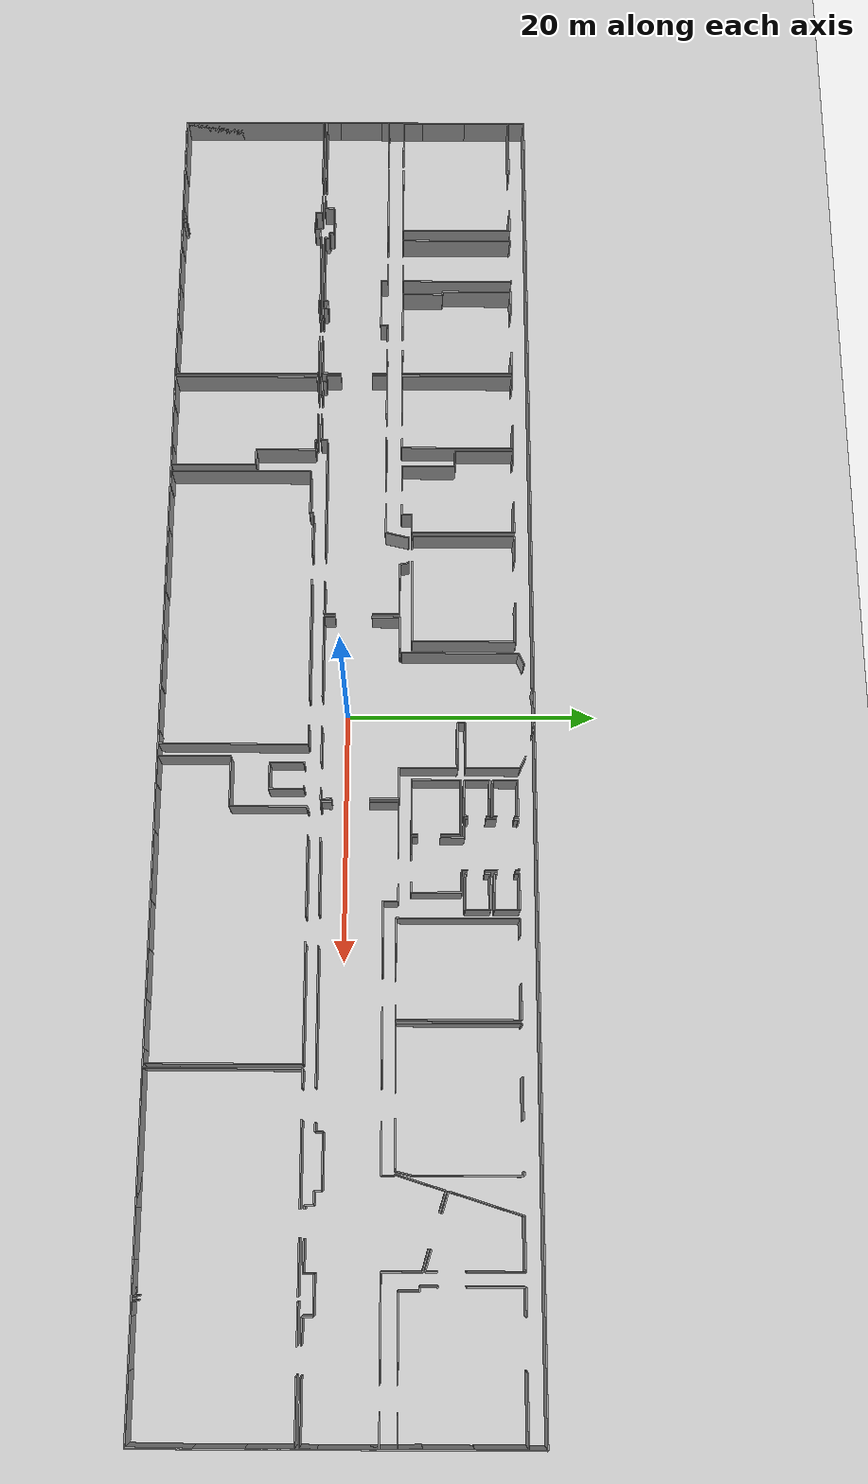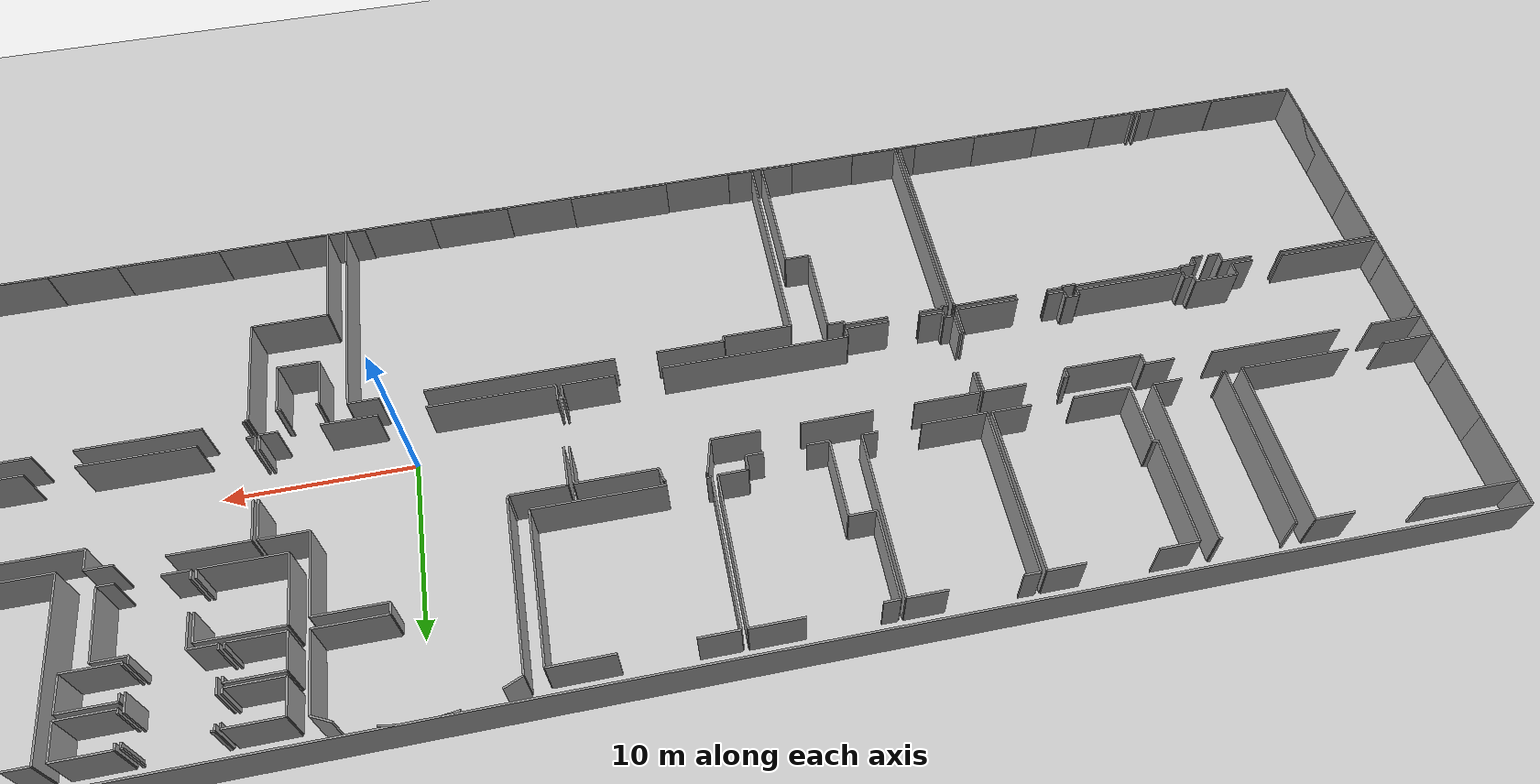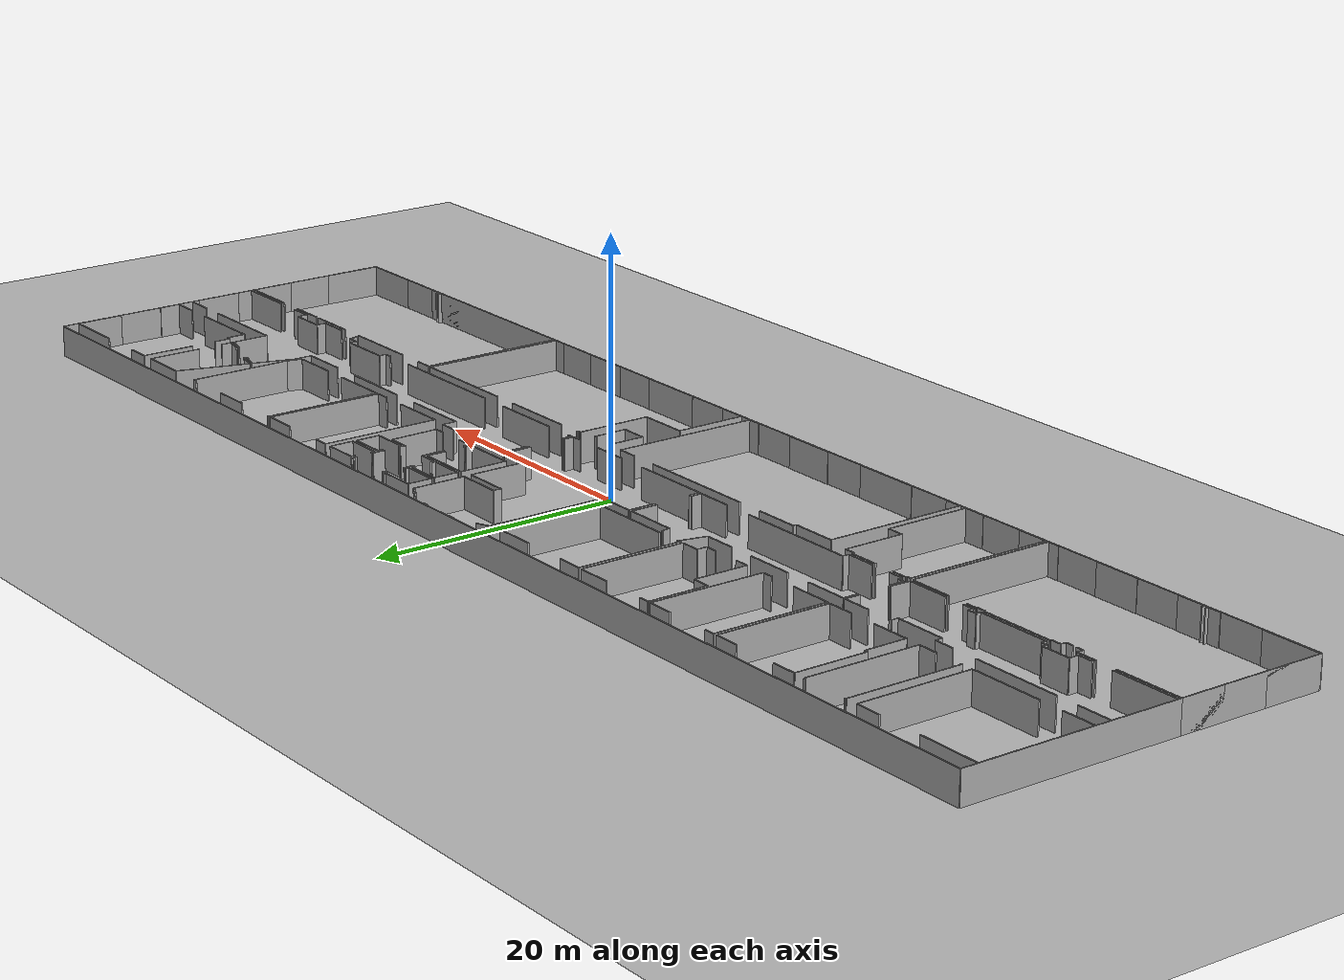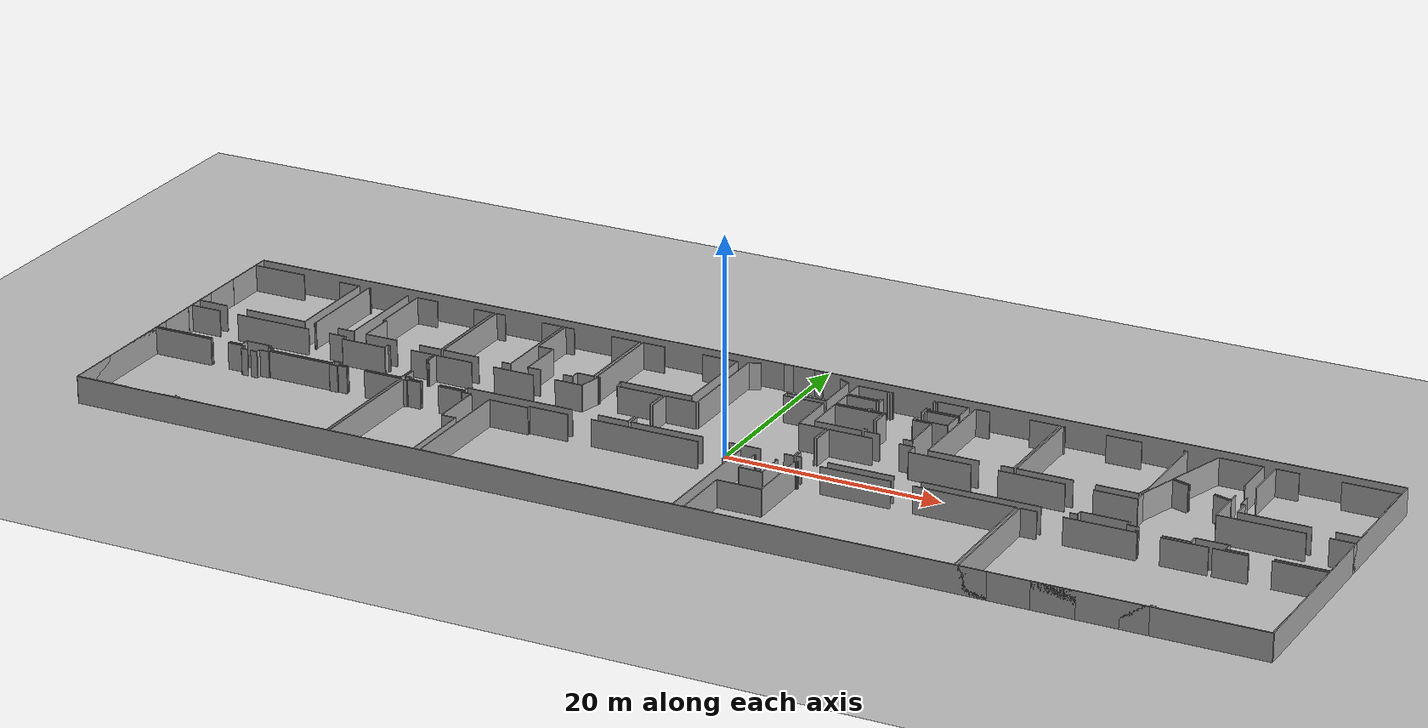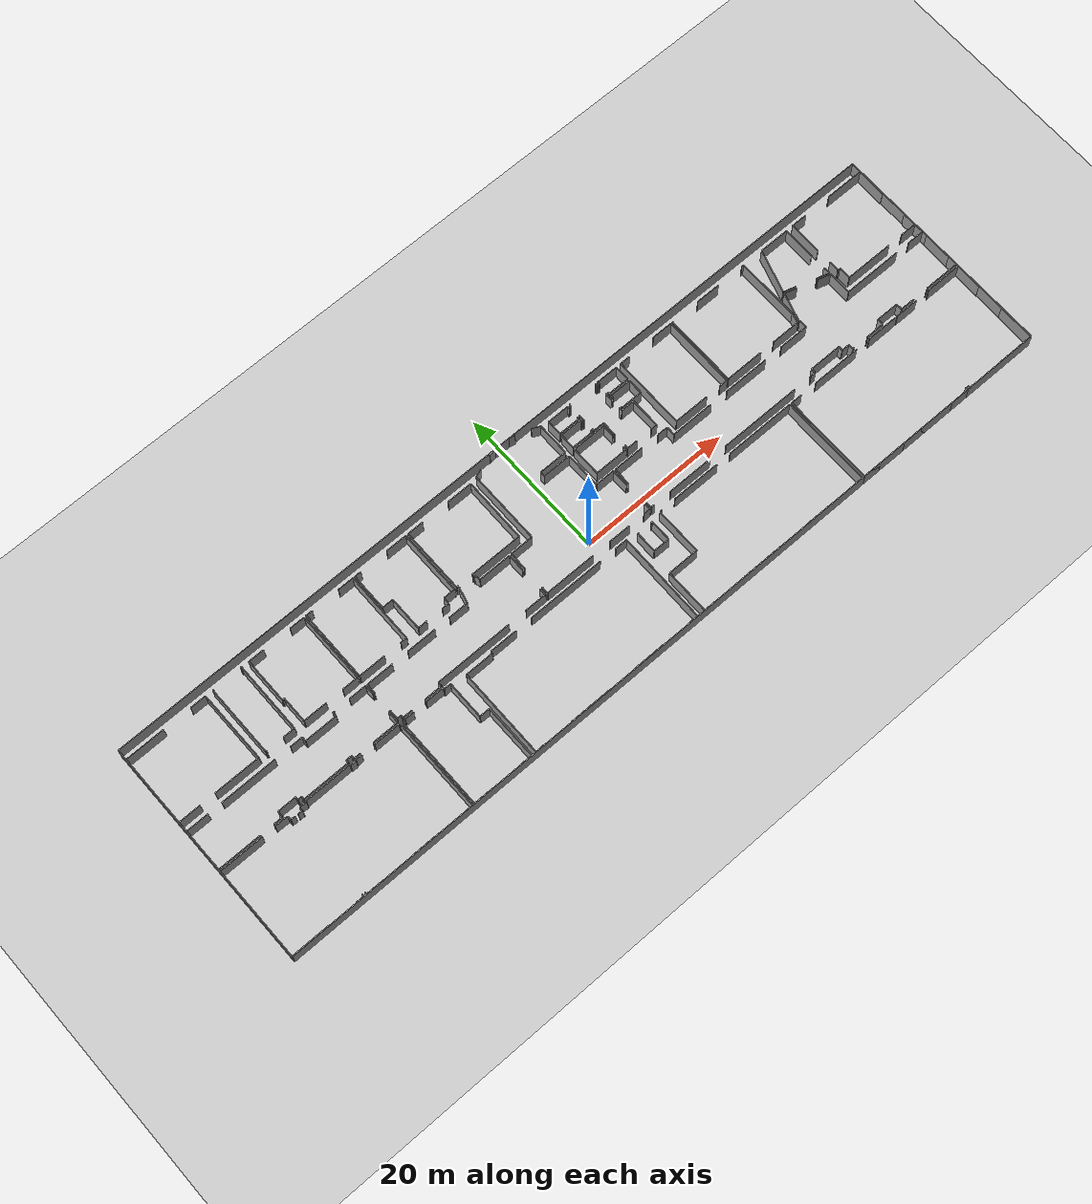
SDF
<sdf version="1.6">
  <world name="default">
    <light name="sun" type="directional">
      <cast_shadows>1</cast_shadows>
      <pose frame="">0 0 10 0 -0 0</pose>
      <diffuse>0.8 0.8 0.8 1</diffuse>
      <specular>0.1 0.1 0.1 1</specular>
      <attenuation>
        <range>1000</range>
        <constant>0.9</constant>
        <linear>0.01</linear>
        <quadratic>0.001</quadratic>
      </attenuation>
      <direction>-0.5 0.5 -1</direction>
    </light>
    <model name="ground_plane">
      <static>1</static>
      <link name="link">
        <collision name="collision">
          <geometry>
            <plane>
              <normal>0 0 1</normal>
              <size>100 100</size>
            </plane>
          </geometry>
          <surface>
            <friction>
              <ode>
                <mu>100</mu>
                <mu2>50</mu2>
              </ode>
              <torsional>
                <ode />
              </torsional>
            </friction>
            <contact>
              <ode />
            </contact>
            <bounce />
          </surface>
          <max_contacts>10</max_contacts>
        </collision>
        <visual name="visual">
          <cast_shadows>0</cast_shadows>
          <geometry>
            <plane>
              <normal>0 0 1</normal>
              <size>100 100</size>
            </plane>
          </geometry>
          <material>
            <script>
              <uri>file://media/materials/scripts/gazebo.material</uri>
              <name>Gazebo/Grey</name>
            </script>
          </material>
        </visual>
        <self_collide>0</self_collide>
        <kinematic>0</kinematic>
        <gravity>1</gravity>
      </link>
    </model>
    <gravity>0 0 -9.8</gravity>
    <magnetic_field>6e-06 2.3e-05 -4.2e-05</magnetic_field>
    <atmosphere type="adiabatic" />
    <physics default="0" name="default_physics" type="ode">
      <max_step_size>0.001</max_step_size>
      <real_time_factor>1</real_time_factor>
      <real_time_update_rate>1000</real_time_update_rate>
    </physics>
    <scene>
      <ambient>0.4 0.4 0.4 1</ambient>
      <background>0.7 0.7 0.7 1</background>
      <shadows>1</shadows>
    </scene>
    <spherical_coordinates>
      <surface_model>EARTH_WGS84</surface_model>
      <latitude_deg>0</latitude_deg>
      <longitude_deg>0</longitude_deg>
      <elevation>0</elevation>
      <heading_deg>0</heading_deg>
    </spherical_coordinates>
  <model name="50056458">
		<static>1</static>
		<link name="Wall_0">
			<collision name="Wall_0_Collision">
				<geometry>
					<box>
						<size>6.05910203529 0.1 2.5</size>
					</box>
				</geometry>
				<pose frame="">3.02955101764 0 1.25 0 0 0</pose>
			</collision>
			<visual name="Wall_0_Visual">
				<pose frame="">3.02955101764 0 1.25 0 0 0</pose>
				<geometry>
					<box>
						<size>6.05910203529 0.1 2.5</size>
					</box>
				</geometry>
				<material>
					<script>
						<uri>file://media/materials/scripts/gazebo.material</uri>
						<name>Gazebo/Grey</name>
					</script>
					<ambient>1 1 1 1</ambient>
				</material>
			</visual>
			<pose frame="">10.9724139683 -10.6930810472 0 0 0 3.14159265359</pose>
		</link>
		<link name="Wall_1">
			<collision name="Wall_1_Collision">
				<geometry>
					<box>
						<size>2.85769944184 0.1 2.5</size>
					</box>
				</geometry>
				<pose frame="">1.42884972092 0 1.25 0 0 0</pose>
			</collision>
			<visual name="Wall_1_Visual">
				<pose frame="">1.42884972092 0 1.25 0 0 0</pose>
				<geometry>
					<box>
						<size>2.85769944184 0.1 2.5</size>
					</box>
				</geometry>
				<material>
					<script>
						<uri>file://media/materials/scripts/gazebo.material</uri>
						<name>Gazebo/Grey</name>
					</script>
					<ambient>1 1 1 1</ambient>
				</material>
			</visual>
			<pose frame="">2.86989590656 -10.6930810472 0 0 0 3.14159265359</pose>
		</link>
		<link name="Wall_2">
			<collision name="Wall_2_Collision">
				<geometry>
					<box>
						<size>1.70631929328 0.1 2.5</size>
					</box>
				</geometry>
				<pose frame="">0.853159646641 0 1.25 0 0 0</pose>
			</collision>
			<visual name="Wall_2_Visual">
				<pose frame="">0.853159646641 0 1.25 0 0 0</pose>
				<geometry>
					<box>
						<size>1.70631929328 0.1 2.5</size>
					</box>
				</geometry>
				<material>
					<script>
						<uri>file://media/materials/scripts/gazebo.material</uri>
						<name>Gazebo/Grey</name>
					</script>
					<ambient>1 1 1 1</ambient>
				</material>
			</visual>
			<pose frame="">0.0121964647192 -10.6930810472 0 0 0 1.57079632679</pose>
		</link>
		<link name="Wall_3">
			<collision name="Wall_3_Collision">
				<geometry>
					<box>
						<size>3.88321885031 0.1 2.5</size>
					</box>
				</geometry>
				<pose frame="">1.94160942516 0 1.25 0 0 0</pose>
			</collision>
			<visual name="Wall_3_Visual">
				<pose frame="">1.94160942516 0 1.25 0 0 0</pose>
				<geometry>
					<box>
						<size>3.88321885031 0.1 2.5</size>
					</box>
				</geometry>
				<material>
					<script>
						<uri>file://media/materials/scripts/gazebo.material</uri>
						<name>Gazebo/Grey</name>
					</script>
					<ambient>1 1 1 1</ambient>
				</material>
			</visual>
			<pose frame="">0.0121964647192 -5.25938661946 0 0 0 1.57079632679</pose>
		</link>
		<link name="Wall_4">
			<collision name="Wall_4_Collision">
				<geometry>
					<box>
						<size>5.13149313525 0.1 2.5</size>
					</box>
				</geometry>
				<pose frame="">2.56574656763 0 1.25 0 0 0</pose>
			</collision>
			<visual name="Wall_4_Visual">
				<pose frame="">2.56574656763 0 1.25 0 0 0</pose>
				<geometry>
					<box>
						<size>5.13149313525 0.1 2.5</size>
					</box>
				</geometry>
				<material>
					<script>
						<uri>file://media/materials/scripts/gazebo.material</uri>
						<name>Gazebo/Grey</name>
					</script>
					<ambient>1 1 1 1</ambient>
				</material>
			</visual>
			<pose frame="">0.0121964647192 -1.37616776915 0 0 0 0.0</pose>
		</link>
		<link name="Wall_5">
			<collision name="Wall_5_Collision">
				<geometry>
					<box>
						<size>2.08712002507 0.1 2.5</size>
					</box>
				</geometry>
				<pose frame="">1.04356001254 0 1.25 0 0 0</pose>
			</collision>
			<visual name="Wall_5_Visual">
				<pose frame="">1.04356001254 0 1.25 0 0 0</pose>
				<geometry>
					<box>
						<size>2.08712002507 0.1 2.5</size>
					</box>
				</geometry>
				<material>
					<script>
						<uri>file://media/materials/scripts/gazebo.material</uri>
						<name>Gazebo/Grey</name>
					</script>
					<ambient>1 1 1 1</ambient>
				</material>
			</visual>
			<pose frame="">8.84938213049 -1.37616776915 0 0 0 0.0</pose>
		</link>
		<link name="Wall_6">
			<collision name="Wall_6_Collision">
				<geometry>
					<box>
						<size>9.3169824884 0.1 2.5</size>
					</box>
				</geometry>
				<pose frame="">4.6584912442 0 1.25 0 0 0</pose>
			</collision>
			<visual name="Wall_6_Visual">
				<pose frame="">4.6584912442 0 1.25 0 0 0</pose>
				<geometry>
					<box>
						<size>9.3169824884 0.1 2.5</size>
					</box>
				</geometry>
				<material>
					<script>
						<uri>file://media/materials/scripts/gazebo.material</uri>
						<name>Gazebo/Grey</name>
					</script>
					<ambient>1 1 1 1</ambient>
				</material>
			</visual>
			<pose frame="">10.9365021556 -1.37616776915 0 0 0 -1.56694187051</pose>
		</link>
		<link name="Wall_7">
			<collision name="Wall_7_Collision">
				<geometry>
					<box>
						<size>1.59129985517 0.1 2.5</size>
					</box>
				</geometry>
				<pose frame="">0.795649927583 0 1.25 0 0 0</pose>
			</collision>
			<visual name="Wall_7_Visual">
				<pose frame="">0.795649927583 0 1.25 0 0 0</pose>
				<geometry>
					<box>
						<size>1.59129985517 0.1 2.5</size>
					</box>
				</geometry>
				<material>
					<script>
						<uri>file://media/materials/scripts/gazebo.material</uri>
						<name>Gazebo/Grey</name>
					</script>
					<ambient>1 1 1 1</ambient>
				</material>
			</visual>
			<pose frame="">15.9621232012 -10.6707208619 0 0 0 3.14159265359</pose>
		</link>
		<link name="Wall_8">
			<collision name="Wall_8_Collision">
				<geometry>
					<box>
						<size>0.135516274658 0.1 2.5</size>
					</box>
				</geometry>
				<pose frame="">0.0677581373288 0 1.25 0 0 0</pose>
			</collision>
			<visual name="Wall_8_Visual">
				<pose frame="">0.0677581373288 0 1.25 0 0 0</pose>
				<geometry>
					<box>
						<size>0.135516274658 0.1 2.5</size>
					</box>
				</geometry>
				<material>
					<script>
						<uri>file://media/materials/scripts/gazebo.material</uri>
						<name>Gazebo/Grey</name>
					</script>
					<ambient>1 1 1 1</ambient>
				</material>
			</visual>
			<pose frame="">12.0851719786 -10.6707208619 0 0 0 3.14159265359</pose>
		</link>
		<link name="Wall_9">
			<collision name="Wall_9_Collision">
				<geometry>
					<box>
						<size>9.32250332438 0.1 2.5</size>
					</box>
				</geometry>
				<pose frame="">4.66125166219 0 1.25 0 0 0</pose>
			</collision>
			<visual name="Wall_9_Visual">
				<pose frame="">4.66125166219 0 1.25 0 0 0</pose>
				<geometry>
					<box>
						<size>9.32250332438 0.1 2.5</size>
					</box>
				</geometry>
				<material>
					<script>
						<uri>file://media/materials/scripts/gazebo.material</uri>
						<name>Gazebo/Grey</name>
					</script>
					<ambient>1 1 1 1</ambient>
				</material>
			</visual>
			<pose frame="">11.949655704 -10.6707208619 0 0 0 1.57079632679</pose>
		</link>
		<link name="Wall_10">
			<collision name="Wall_10_Collision">
				<geometry>
					<box>
						<size>0.136532646718 0.1 2.5</size>
					</box>
				</geometry>
				<pose frame="">0.0682663233588 0 1.25 0 0 0</pose>
			</collision>
			<visual name="Wall_10_Visual">
				<pose frame="">0.0682663233588 0 1.25 0 0 0</pose>
				<geometry>
					<box>
						<size>0.136532646718 0.1 2.5</size>
					</box>
				</geometry>
				<material>
					<script>
						<uri>file://media/materials/scripts/gazebo.material</uri>
						<name>Gazebo/Grey</name>
					</script>
					<ambient>1 1 1 1</ambient>
				</material>
			</visual>
			<pose frame="">11.949655704 -1.3482175375 0 0 0 0.0</pose>
		</link>
		<link name="Wall_11">
			<collision name="Wall_11_Collision">
				<geometry>
					<box>
						<size>0.1560131112 0.1 2.5</size>
					</box>
				</geometry>
				<pose frame="">0.0780065555998 0 1.25 0 0 0</pose>
			</collision>
			<visual name="Wall_11_Visual">
				<pose frame="">0.0780065555998 0 1.25 0 0 0</pose>
				<geometry>
					<box>
						<size>0.1560131112 0.1 2.5</size>
					</box>
				</geometry>
				<material>
					<script>
						<uri>file://media/materials/scripts/gazebo.material</uri>
						<name>Gazebo/Grey</name>
					</script>
					<ambient>1 1 1 1</ambient>
				</material>
			</visual>
			<pose frame="">15.8284702754 -1.3482175375 0 0 0 0.0</pose>
		</link>
		<link name="Wall_12">
			<collision name="Wall_12_Collision">
				<geometry>
					<box>
						<size>9.32253013999 0.1 2.5</size>
					</box>
				</geometry>
				<pose frame="">4.66126507 0 1.25 0 0 0</pose>
			</collision>
			<visual name="Wall_12_Visual">
				<pose frame="">4.66126507 0 1.25 0 0 0</pose>
				<geometry>
					<box>
						<size>9.32253013999 0.1 2.5</size>
					</box>
				</geometry>
				<material>
					<script>
						<uri>file://media/materials/scripts/gazebo.material</uri>
						<name>Gazebo/Grey</name>
					</script>
					<ambient>1 1 1 1</ambient>
				</material>
			</visual>
			<pose frame="">15.9844833866 -1.3482175375 0 0 0 -1.57319483948</pose>
		</link>
		<link name="Wall_13">
			<collision name="Wall_13_Collision">
				<geometry>
					<box>
						<size>2.14437565111 0.1 2.5</size>
					</box>
				</geometry>
				<pose frame="">1.07218782556 0 1.25 0 0 0</pose>
			</collision>
			<visual name="Wall_13_Visual">
				<pose frame="">1.07218782556 0 1.25 0 0 0</pose>
				<geometry>
					<box>
						<size>2.14437565111 0.1 2.5</size>
					</box>
				</geometry>
				<material>
					<script>
						<uri>file://media/materials/scripts/gazebo.material</uri>
						<name>Gazebo/Grey</name>
					</script>
					<ambient>1 1 1 1</ambient>
				</material>
			</visual>
			<pose frame="">24.8252263545 -10.7030753725 0 0 0 3.14159265359</pose>
		</link>
		<link name="Wall_14">
			<collision name="Wall_14_Collision">
				<geometry>
					<box>
						<size>3.11602734041 0.1 2.5</size>
					</box>
				</geometry>
				<pose frame="">1.5580136702 0 1.25 0 0 0</pose>
			</collision>
			<visual name="Wall_14_Visual">
				<pose frame="">1.5580136702 0 1.25 0 0 0</pose>
				<geometry>
					<box>
						<size>3.11602734041 0.1 2.5</size>
					</box>
				</geometry>
				<material>
					<script>
						<uri>file://media/materials/scripts/gazebo.material</uri>
						<name>Gazebo/Grey</name>
					</script>
					<ambient>1 1 1 1</ambient>
				</material>
			</visual>
			<pose frame="">20.3713145926 -10.7030753725 0 0 0 3.14159265359</pose>
		</link>
		<link name="Wall_15">
			<collision name="Wall_15_Collision">
				<geometry>
					<box>
						<size>3.41822863289 0.1 2.5</size>
					</box>
				</geometry>
				<pose frame="">1.70911431645 0 1.25 0 0 0</pose>
			</collision>
			<visual name="Wall_15_Visual">
				<pose frame="">1.70911431645 0 1.25 0 0 0</pose>
				<geometry>
					<box>
						<size>3.41822863289 0.1 2.5</size>
					</box>
				</geometry>
				<material>
					<script>
						<uri>file://media/materials/scripts/gazebo.material</uri>
						<name>Gazebo/Grey</name>
					</script>
					<ambient>1 1 1 1</ambient>
				</material>
			</visual>
			<pose frame="">17.2552872522 -10.7030753725 0 0 0 1.57079632679</pose>
		</link>
		<link name="Wall_16">
			<collision name="Wall_16_Collision">
				<geometry>
					<box>
						<size>0.279502316481 0.1 2.5</size>
					</box>
				</geometry>
				<pose frame="">0.139751158241 0 1.25 0 0 0</pose>
			</collision>
			<visual name="Wall_16_Visual">
				<pose frame="">0.139751158241 0 1.25 0 0 0</pose>
				<geometry>
					<box>
						<size>0.279502316481 0.1 2.5</size>
					</box>
				</geometry>
				<material>
					<script>
						<uri>file://media/materials/scripts/gazebo.material</uri>
						<name>Gazebo/Grey</name>
					</script>
					<ambient>1 1 1 1</ambient>
				</material>
			</visual>
			<pose frame="">17.2552872522 -7.28484673956 0 0 0 3.14159265359</pose>
		</link>
		<link name="Wall_17">
			<collision name="Wall_17_Collision">
				<geometry>
					<box>
						<size>5.89224762211 0.1 2.5</size>
					</box>
				</geometry>
				<pose frame="">2.94612381106 0 1.25 0 0 0</pose>
			</collision>
			<visual name="Wall_17_Visual">
				<pose frame="">2.94612381106 0 1.25 0 0 0</pose>
				<geometry>
					<box>
						<size>5.89224762211 0.1 2.5</size>
					</box>
				</geometry>
				<material>
					<script>
						<uri>file://media/materials/scripts/gazebo.material</uri>
						<name>Gazebo/Grey</name>
					</script>
					<ambient>1 1 1 1</ambient>
				</material>
			</visual>
			<pose frame="">16.9757849357 -7.28484673956 0 0 0 1.57079632679</pose>
		</link>
		<link name="Wall_18">
			<collision name="Wall_18_Collision">
				<geometry>
					<box>
						<size>2.07136625814 0.1 2.5</size>
					</box>
				</geometry>
				<pose frame="">1.03568312907 0 1.25 0 0 0</pose>
			</collision>
			<visual name="Wall_18_Visual">
				<pose frame="">1.03568312907 0 1.25 0 0 0</pose>
				<geometry>
					<box>
						<size>2.07136625814 0.1 2.5</size>
					</box>
				</geometry>
				<material>
					<script>
						<uri>file://media/materials/scripts/gazebo.material</uri>
						<name>Gazebo/Grey</name>
					</script>
					<ambient>1 1 1 1</ambient>
				</material>
			</visual>
			<pose frame="">16.9757849357 -1.39259911745 0 0 0 0.0</pose>
		</link>
		<link name="Wall_19">
			<collision name="Wall_19_Collision">
				<geometry>
					<box>
						<size>1.99598533036 0.1 2.5</size>
					</box>
				</geometry>
				<pose frame="">0.997992665182 0 1.25 0 0 0</pose>
			</collision>
			<visual name="Wall_19_Visual">
				<pose frame="">0.997992665182 0 1.25 0 0 0</pose>
				<geometry>
					<box>
						<size>1.99598533036 0.1 2.5</size>
					</box>
				</geometry>
				<material>
					<script>
						<uri>file://media/materials/scripts/gazebo.material</uri>
						<name>Gazebo/Grey</name>
					</script>
					<ambient>1 1 1 1</ambient>
				</material>
			</visual>
			<pose frame="">22.7950231648 -1.39259911745 0 0 0 0.0</pose>
		</link>
		<link name="Wall_20">
			<collision name="Wall_20_Collision">
				<geometry>
					<box>
						<size>9.31053913353 0.1 2.5</size>
					</box>
				</geometry>
				<pose frame="">4.65526956676 0 1.25 0 0 0</pose>
			</collision>
			<visual name="Wall_20_Visual">
				<pose frame="">4.65526956676 0 1.25 0 0 0</pose>
				<geometry>
					<box>
						<size>9.31053913353 0.1 2.5</size>
					</box>
				</geometry>
				<material>
					<script>
						<uri>file://media/materials/scripts/gazebo.material</uri>
						<name>Gazebo/Grey</name>
					</script>
					<ambient>1 1 1 1</ambient>
				</material>
			</visual>
			<pose frame="">24.7910084952 -1.39259911745 0 0 0 -1.56712114366</pose>
		</link>
		<link name="Wall_21">
			<collision name="Wall_21_Collision">
				<geometry>
					<box>
						<size>0.998754944227 0.1 2.5</size>
					</box>
				</geometry>
				<pose frame="">0.499377472113 0 1.25 0 0 0</pose>
			</collision>
			<visual name="Wall_21_Visual">
				<pose frame="">0.499377472113 0 1.25 0 0 0</pose>
				<geometry>
					<box>
						<size>0.998754944227 0.1 2.5</size>
					</box>
				</geometry>
				<material>
					<script>
						<uri>file://media/materials/scripts/gazebo.material</uri>
						<name>Gazebo/Grey</name>
					</script>
					<ambient>1 1 1 1</ambient>
				</material>
			</visual>
			<pose frame="">24.9619283966 -30.0209203249 0 0 0 3.14159265359</pose>
		</link>
		<link name="Wall_22">
			<collision name="Wall_22_Collision">
				<geometry>
					<box>
						<size>3.88813131527 0.1 2.5</size>
					</box>
				</geometry>
				<pose frame="">1.94406565764 0 1.25 0 0 0</pose>
			</collision>
			<visual name="Wall_22_Visual">
				<pose frame="">1.94406565764 0 1.25 0 0 0</pose>
				<geometry>
					<box>
						<size>3.88813131527 0.1 2.5</size>
					</box>
				</geometry>
				<material>
					<script>
						<uri>file://media/materials/scripts/gazebo.material</uri>
						<name>Gazebo/Grey</name>
					</script>
					<ambient>1 1 1 1</ambient>
				</material>
			</visual>
			<pose frame="">20.2512132941 -30.0209203249 0 0 0 3.14159265359</pose>
		</link>
		<link name="Wall_23">
			<collision name="Wall_23_Collision">
				<geometry>
					<box>
						<size>2.43099257201 0.1 2.5</size>
					</box>
				</geometry>
				<pose frame="">1.21549628601 0 1.25 0 0 0</pose>
			</collision>
			<visual name="Wall_23_Visual">
				<pose frame="">1.21549628601 0 1.25 0 0 0</pose>
				<geometry>
					<box>
						<size>2.43099257201 0.1 2.5</size>
					</box>
				</geometry>
				<material>
					<script>
						<uri>file://media/materials/scripts/gazebo.material</uri>
						<name>Gazebo/Grey</name>
					</script>
					<ambient>1 1 1 1</ambient>
				</material>
			</visual>
			<pose frame="">12.6082647988 -30.0209203249 0 0 0 3.14159265359</pose>
		</link>
		<link name="Wall_24">
			<collision name="Wall_24_Collision">
				<geometry>
					<box>
						<size>0.296950036843 0.1 2.5</size>
					</box>
				</geometry>
				<pose frame="">0.148475018422 0 1.25 0 0 0</pose>
			</collision>
			<visual name="Wall_24_Visual">
				<pose frame="">0.148475018422 0 1.25 0 0 0</pose>
				<geometry>
					<box>
						<size>0.296950036843 0.1 2.5</size>
					</box>
				</geometry>
				<material>
					<script>
						<uri>file://media/materials/scripts/gazebo.material</uri>
						<name>Gazebo/Grey</name>
					</script>
					<ambient>1 1 1 1</ambient>
				</material>
			</visual>
			<pose frame="">10.1772722268 -30.0209203249 0 0 0 1.57079632679</pose>
		</link>
		<link name="Wall_25">
			<collision name="Wall_25_Collision">
				<geometry>
					<box>
						<size>0.616937840379 0.1 2.5</size>
					</box>
				</geometry>
				<pose frame="">0.308468920189 0 1.25 0 0 0</pose>
			</collision>
			<visual name="Wall_25_Visual">
				<pose frame="">0.308468920189 0 1.25 0 0 0</pose>
				<geometry>
					<box>
						<size>0.616937840379 0.1 2.5</size>
					</box>
				</geometry>
				<material>
					<script>
						<uri>file://media/materials/scripts/gazebo.material</uri>
						<name>Gazebo/Grey</name>
					</script>
					<ambient>1 1 1 1</ambient>
				</material>
			</visual>
			<pose frame="">10.1772722268 -18.4005691684 0 0 0 0.0</pose>
		</link>
		<link name="Wall_26">
			<collision name="Wall_26_Collision">
				<geometry>
					<box>
						<size>0.456689845596 0.1 2.5</size>
					</box>
				</geometry>
				<pose frame="">0.228344922798 0 1.25 0 0 0</pose>
			</collision>
			<visual name="Wall_26_Visual">
				<pose frame="">0.228344922798 0 1.25 0 0 0</pose>
				<geometry>
					<box>
						<size>0.456689845596 0.1 2.5</size>
					</box>
				</geometry>
				<material>
					<script>
						<uri>file://media/materials/scripts/gazebo.material</uri>
						<name>Gazebo/Grey</name>
					</script>
					<ambient>1 1 1 1</ambient>
				</material>
			</visual>
			<pose frame="">10.7942100672 -18.4005691684 0 0 0 1.57079632679</pose>
		</link>
		<link name="Wall_27">
			<collision name="Wall_27_Collision">
				<geometry>
					<box>
						<size>0.913210295849 0.1 2.5</size>
					</box>
				</geometry>
				<pose frame="">0.456605147924 0 1.25 0 0 0</pose>
			</collision>
			<visual name="Wall_27_Visual">
				<pose frame="">0.456605147924 0 1.25 0 0 0</pose>
				<geometry>
					<box>
						<size>0.913210295849 0.1 2.5</size>
					</box>
				</geometry>
				<material>
					<script>
						<uri>file://media/materials/scripts/gazebo.material</uri>
						<name>Gazebo/Grey</name>
					</script>
					<ambient>1 1 1 1</ambient>
				</material>
			</visual>
			<pose frame="">10.7942100672 -17.9438793228 0 0 0 0.0</pose>
		</link>
		<link name="Wall_28">
			<collision name="Wall_28_Collision">
				<geometry>
					<box>
						<size>0.111292740563 0.1 2.5</size>
					</box>
				</geometry>
				<pose frame="">0.0556463702813 0 1.25 0 0 0</pose>
			</collision>
			<visual name="Wall_28_Visual">
				<pose frame="">0.0556463702813 0 1.25 0 0 0</pose>
				<geometry>
					<box>
						<size>0.111292740563 0.1 2.5</size>
					</box>
				</geometry>
				<material>
					<script>
						<uri>file://media/materials/scripts/gazebo.material</uri>
						<name>Gazebo/Grey</name>
					</script>
					<ambient>1 1 1 1</ambient>
				</material>
			</visual>
			<pose frame="">11.707420363 -17.9438793228 0 0 0 1.57079632679</pose>
		</link>
		<link name="Wall_29">
			<collision name="Wall_29_Collision">
				<geometry>
					<box>
						<size>6.16954779913 0.1 2.5</size>
					</box>
				</geometry>
				<pose frame="">3.08477389957 0 1.25 0 0 0</pose>
			</collision>
			<visual name="Wall_29_Visual">
				<pose frame="">3.08477389957 0 1.25 0 0 0</pose>
				<geometry>
					<box>
						<size>6.16954779913 0.1 2.5</size>
					</box>
				</geometry>
				<material>
					<script>
						<uri>file://media/materials/scripts/gazebo.material</uri>
						<name>Gazebo/Grey</name>
					</script>
					<ambient>1 1 1 1</ambient>
				</material>
			</visual>
			<pose frame="">11.707420363 -17.8325865822 0 0 0 0.0</pose>
		</link>
		<link name="Wall_30">
			<collision name="Wall_30_Collision">
				<geometry>
					<box>
						<size>0.0948613922603 0.1 2.5</size>
					</box>
				</geometry>
				<pose frame="">0.0474306961302 0 1.25 0 0 0</pose>
			</collision>
			<visual name="Wall_30_Visual">
				<pose frame="">0.0474306961302 0 1.25 0 0 0</pose>
				<geometry>
					<box>
						<size>0.0948613922603 0.1 2.5</size>
					</box>
				</geometry>
				<material>
					<script>
						<uri>file://media/materials/scripts/gazebo.material</uri>
						<name>Gazebo/Grey</name>
					</script>
					<ambient>1 1 1 1</ambient>
				</material>
			</visual>
			<pose frame="">17.8769681621 -17.8325865822 0 0 0 -1.57079632679</pose>
		</link>
		<link name="Wall_31">
			<collision name="Wall_31_Collision">
				<geometry>
					<box>
						<size>0.774814300355 0.1 2.5</size>
					</box>
				</geometry>
				<pose frame="">0.387407150177 0 1.25 0 0 0</pose>
			</collision>
			<visual name="Wall_31_Visual">
				<pose frame="">0.387407150177 0 1.25 0 0 0</pose>
				<geometry>
					<box>
						<size>0.774814300355 0.1 2.5</size>
					</box>
				</geometry>
				<material>
					<script>
						<uri>file://media/materials/scripts/gazebo.material</uri>
						<name>Gazebo/Grey</name>
					</script>
					<ambient>1 1 1 1</ambient>
				</material>
			</visual>
			<pose frame="">17.8769681621 -17.9274479745 0 0 0 0.0</pose>
		</link>
		<link name="Wall_32">
			<collision name="Wall_32_Collision">
				<geometry>
					<box>
						<size>0.0968941363802 0.1 2.5</size>
					</box>
				</geometry>
				<pose frame="">0.0484470681901 0 1.25 0 0 0</pose>
			</collision>
			<visual name="Wall_32_Visual">
				<pose frame="">0.0484470681901 0 1.25 0 0 0</pose>
				<geometry>
					<box>
						<size>0.0968941363802 0.1 2.5</size>
					</box>
				</geometry>
				<material>
					<script>
						<uri>file://media/materials/scripts/gazebo.material</uri>
						<name>Gazebo/Grey</name>
					</script>
					<ambient>1 1 1 1</ambient>
				</material>
			</visual>
			<pose frame="">18.6517824625 -17.9274479745 0 0 0 1.57079632679</pose>
		</link>
		<link name="Wall_33">
			<collision name="Wall_33_Collision">
				<geometry>
					<box>
						<size>0.900675040443 0.1 2.5</size>
					</box>
				</geometry>
				<pose frame="">0.450337520222 0 1.25 0 0 0</pose>
			</collision>
			<visual name="Wall_33_Visual">
				<pose frame="">0.450337520222 0 1.25 0 0 0</pose>
				<geometry>
					<box>
						<size>0.900675040443 0.1 2.5</size>
					</box>
				</geometry>
				<material>
					<script>
						<uri>file://media/materials/scripts/gazebo.material</uri>
						<name>Gazebo/Grey</name>
					</script>
					<ambient>1 1 1 1</ambient>
				</material>
			</visual>
			<pose frame="">18.6517824625 -17.8305538381 0 0 0 0.0</pose>
		</link>
		<link name="Wall_34">
			<collision name="Wall_34_Collision">
				<geometry>
					<box>
						<size>3.47124937535 0.1 2.5</size>
					</box>
				</geometry>
				<pose frame="">1.73562468768 0 1.25 0 0 0</pose>
			</collision>
			<visual name="Wall_34_Visual">
				<pose frame="">1.73562468768 0 1.25 0 0 0</pose>
				<geometry>
					<box>
						<size>3.47124937535 0.1 2.5</size>
					</box>
				</geometry>
				<material>
					<script>
						<uri>file://media/materials/scripts/gazebo.material</uri>
						<name>Gazebo/Grey</name>
					</script>
					<ambient>1 1 1 1</ambient>
				</material>
			</visual>
			<pose frame="">21.3283982823 -17.8305538381 0 0 0 0.0</pose>
		</link>
		<link name="Wall_35">
			<collision name="Wall_35_Collision">
				<geometry>
					<box>
						<size>0.0858834390643 0.1 2.5</size>
					</box>
				</geometry>
				<pose frame="">0.0429417195321 0 1.25 0 0 0</pose>
			</collision>
			<visual name="Wall_35_Visual">
				<pose frame="">0.0429417195321 0 1.25 0 0 0</pose>
				<geometry>
					<box>
						<size>0.0858834390643 0.1 2.5</size>
					</box>
				</geometry>
				<material>
					<script>
						<uri>file://media/materials/scripts/gazebo.material</uri>
						<name>Gazebo/Grey</name>
					</script>
					<ambient>1 1 1 1</ambient>
				</material>
			</visual>
			<pose frame="">24.7996476577 -17.8305538381 0 0 0 -1.57079632679</pose>
		</link>
		<link name="Wall_36">
			<collision name="Wall_36_Collision">
				<geometry>
					<box>
						<size>0.126030135432 0.1 2.5</size>
					</box>
				</geometry>
				<pose frame="">0.0630150677158 0 1.25 0 0 0</pose>
			</collision>
			<visual name="Wall_36_Visual">
				<pose frame="">0.0630150677158 0 1.25 0 0 0</pose>
				<geometry>
					<box>
						<size>0.126030135432 0.1 2.5</size>
					</box>
				</geometry>
				<material>
					<script>
						<uri>file://media/materials/scripts/gazebo.material</uri>
						<name>Gazebo/Grey</name>
					</script>
					<ambient>1 1 1 1</ambient>
				</material>
			</visual>
			<pose frame="">24.7996476577 -17.9164372771 0 0 0 0.0</pose>
		</link>
		<link name="Wall_37">
			<collision name="Wall_37_Collision">
				<geometry>
					<box>
						<size>12.1045373294 0.1 2.5</size>
					</box>
				</geometry>
				<pose frame="">6.05226866472 0 1.25 0 0 0</pose>
			</collision>
			<visual name="Wall_37_Visual">
				<pose frame="">6.05226866472 0 1.25 0 0 0</pose>
				<geometry>
					<box>
						<size>12.1045373294 0.1 2.5</size>
					</box>
				</geometry>
				<material>
					<script>
						<uri>file://media/materials/scripts/gazebo.material</uri>
						<name>Gazebo/Grey</name>
					</script>
					<ambient>1 1 1 1</ambient>
				</material>
			</visual>
			<pose frame="">24.9256777931 -17.9164372771 0 0 0 -1.56780152768</pose>
		</link>
		<link name="Wall_38">
			<collision name="Wall_38_Collision">
				<geometry>
					<box>
						<size>1.08972024359 0.1 2.5</size>
					</box>
				</geometry>
				<pose frame="">0.544860121795 0 1.25 0 0 0</pose>
			</collision>
			<visual name="Wall_38_Visual">
				<pose frame="">0.544860121795 0 1.25 0 0 0</pose>
				<geometry>
					<box>
						<size>1.08972024359 0.1 2.5</size>
					</box>
				</geometry>
				<material>
					<script>
						<uri>file://media/materials/scripts/gazebo.material</uri>
						<name>Gazebo/Grey</name>
					</script>
					<ambient>1 1 1 1</ambient>
				</material>
			</visual>
			<pose frame="">9.82848721489 -29.9951722327 0 0 0 3.14159265359</pose>
		</link>
		<link name="Wall_39">
			<collision name="Wall_39_Collision">
				<geometry>
					<box>
						<size>5.02460467362 0.1 2.5</size>
					</box>
				</geometry>
				<pose frame="">2.51230233681 0 1.25 0 0 0</pose>
			</collision>
			<visual name="Wall_39_Visual">
				<pose frame="">2.51230233681 0 1.25 0 0 0</pose>
				<geometry>
					<box>
						<size>5.02460467362 0.1 2.5</size>
					</box>
				</geometry>
				<material>
					<script>
						<uri>file://media/materials/scripts/gazebo.material</uri>
						<name>Gazebo/Grey</name>
					</script>
					<ambient>1 1 1 1</ambient>
				</material>
			</visual>
			<pose frame="">5.02460467362 -29.9951722327 0 0 0 3.14159265359</pose>
		</link>
		<link name="Wall_40">
			<collision name="Wall_40_Collision">
				<geometry>
					<box>
						<size>4.83386551704 0.1 2.5</size>
					</box>
				</geometry>
				<pose frame="">2.41693275852 0 1.25 0 0 0</pose>
			</collision>
			<visual name="Wall_40_Visual">
				<pose frame="">2.41693275852 0 1.25 0 0 0</pose>
				<geometry>
					<box>
						<size>4.83386551704 0.1 2.5</size>
					</box>
				</geometry>
				<material>
					<script>
						<uri>file://media/materials/scripts/gazebo.material</uri>
						<name>Gazebo/Grey</name>
					</script>
					<ambient>1 1 1 1</ambient>
				</material>
			</visual>
			<pose frame="">0.0 -29.9951722327 0 0 0 1.57079632679</pose>
		</link>
		<link name="Wall_41">
			<collision name="Wall_41_Collision">
				<geometry>
					<box>
						<size>3.61896211473 0.1 2.5</size>
					</box>
				</geometry>
				<pose frame="">1.80948105737 0 1.25 0 0 0</pose>
			</collision>
			<visual name="Wall_41_Visual">
				<pose frame="">1.80948105737 0 1.25 0 0 0</pose>
				<geometry>
					<box>
						<size>3.61896211473 0.1 2.5</size>
					</box>
				</geometry>
				<material>
					<script>
						<uri>file://media/materials/scripts/gazebo.material</uri>
						<name>Gazebo/Grey</name>
					</script>
					<ambient>1 1 1 1</ambient>
				</material>
			</visual>
			<pose frame="">0.0 -21.4495159528 0 0 0 1.57079632679</pose>
		</link>
		<link name="Wall_42">
			<collision name="Wall_42_Collision">
				<geometry>
					<box>
						<size>5.73166083664 0.1 2.5</size>
					</box>
				</geometry>
				<pose frame="">2.86583041832 0 1.25 0 0 0</pose>
			</collision>
			<visual name="Wall_42_Visual">
				<pose frame="">2.86583041832 0 1.25 0 0 0</pose>
				<geometry>
					<box>
						<size>5.73166083664 0.1 2.5</size>
					</box>
				</geometry>
				<material>
					<script>
						<uri>file://media/materials/scripts/gazebo.material</uri>
						<name>Gazebo/Grey</name>
					</script>
					<ambient>1 1 1 1</ambient>
				</material>
			</visual>
			<pose frame="">0.0 -17.8305538381 0 0 0 0.0</pose>
		</link>
		<link name="Wall_43">
			<collision name="Wall_43_Collision">
				<geometry>
					<box>
						<size>1.72647733914 0.1 2.5</size>
					</box>
				</geometry>
				<pose frame="">0.863238669569 0 1.25 0 0 0</pose>
			</collision>
			<visual name="Wall_43_Visual">
				<pose frame="">0.863238669569 0 1.25 0 0 0</pose>
				<geometry>
					<box>
						<size>1.72647733914 0.1 2.5</size>
					</box>
				</geometry>
				<material>
					<script>
						<uri>file://media/materials/scripts/gazebo.material</uri>
						<name>Gazebo/Grey</name>
					</script>
					<ambient>1 1 1 1</ambient>
				</material>
			</visual>
			<pose frame="">7.48608840743 -17.8305538381 0 0 0 0.0</pose>
		</link>
		<link name="Wall_44">
			<collision name="Wall_44_Collision">
				<geometry>
					<box>
						<size>0.540709935884 0.1 2.5</size>
					</box>
				</geometry>
				<pose frame="">0.270354967942 0 1.25 0 0 0</pose>
			</collision>
			<visual name="Wall_44_Visual">
				<pose frame="">0.270354967942 0 1.25 0 0 0</pose>
				<geometry>
					<box>
						<size>0.540709935884 0.1 2.5</size>
					</box>
				</geometry>
				<material>
					<script>
						<uri>file://media/materials/scripts/gazebo.material</uri>
						<name>Gazebo/Grey</name>
					</script>
					<ambient>1 1 1 1</ambient>
				</material>
			</visual>
			<pose frame="">9.21256574657 -17.8305538381 0 0 0 -1.57079632679</pose>
		</link>
		<link name="Wall_45">
			<collision name="Wall_45_Collision">
				<geometry>
					<box>
						<size>0.621003328618 0.1 2.5</size>
					</box>
				</geometry>
				<pose frame="">0.310501664309 0 1.25 0 0 0</pose>
			</collision>
			<visual name="Wall_45_Visual">
				<pose frame="">0.310501664309 0 1.25 0 0 0</pose>
				<geometry>
					<box>
						<size>0.621003328618 0.1 2.5</size>
					</box>
				</geometry>
				<material>
					<script>
						<uri>file://media/materials/scripts/gazebo.material</uri>
						<name>Gazebo/Grey</name>
					</script>
					<ambient>1 1 1 1</ambient>
				</material>
			</visual>
			<pose frame="">9.21256574657 -18.371263774 0 0 0 0.0</pose>
		</link>
		<link name="Wall_46">
			<collision name="Wall_46_Collision">
				<geometry>
					<box>
						<size>0.313253213647 0.1 2.5</size>
					</box>
				</geometry>
				<pose frame="">0.156626606823 0 1.25 0 0 0</pose>
			</collision>
			<visual name="Wall_46_Visual">
				<pose frame="">0.156626606823 0 1.25 0 0 0</pose>
				<geometry>
					<box>
						<size>0.313253213647 0.1 2.5</size>
					</box>
				</geometry>
				<material>
					<script>
						<uri>file://media/materials/scripts/gazebo.material</uri>
						<name>Gazebo/Grey</name>
					</script>
					<ambient>1 1 1 1</ambient>
				</material>
			</visual>
			<pose frame="">9.83356907519 -29.6819602429 0 0 0 -1.58701988976</pose>
		</link>
		<link name="Wall_47">
			<collision name="Wall_47_Collision">
				<geometry>
					<box>
						<size>3.50614481608 0.1 2.5</size>
					</box>
				</geometry>
				<pose frame="">1.75307240804 0 1.25 0 0 0</pose>
			</collision>
			<visual name="Wall_47_Visual">
				<pose frame="">1.75307240804 0 1.25 0 0 0</pose>
				<geometry>
					<box>
						<size>3.50614481608 0.1 2.5</size>
					</box>
				</geometry>
				<material>
					<script>
						<uri>file://media/materials/scripts/gazebo.material</uri>
						<name>Gazebo/Grey</name>
					</script>
					<ambient>1 1 1 1</ambient>
				</material>
			</visual>
			<pose frame="">24.8406413308 -17.569007428 0 0 0 3.14159265359</pose>
		</link>
		<link name="Wall_48">
			<collision name="Wall_48_Collision">
				<geometry>
					<box>
						<size>0.922188249045 0.1 2.5</size>
					</box>
				</geometry>
				<pose frame="">0.461094124523 0 1.25 0 0 0</pose>
			</collision>
			<visual name="Wall_48_Visual">
				<pose frame="">0.461094124523 0 1.25 0 0 0</pose>
				<geometry>
					<box>
						<size>0.922188249045 0.1 2.5</size>
					</box>
				</geometry>
				<material>
					<script>
						<uri>file://media/materials/scripts/gazebo.material</uri>
						<name>Gazebo/Grey</name>
					</script>
					<ambient>1 1 1 1</ambient>
				</material>
			</visual>
			<pose frame="">19.5736319209 -17.569007428 0 0 0 3.14159265359</pose>
		</link>
		<link name="Wall_49">
			<collision name="Wall_49_Collision">
				<geometry>
					<box>
						<size>0.410275521526 0.1 2.5</size>
					</box>
				</geometry>
				<pose frame="">0.205137760763 0 1.25 0 0 0</pose>
			</collision>
			<visual name="Wall_49_Visual">
				<pose frame="">0.205137760763 0 1.25 0 0 0</pose>
				<geometry>
					<box>
						<size>0.410275521526 0.1 2.5</size>
					</box>
				</geometry>
				<material>
					<script>
						<uri>file://media/materials/scripts/gazebo.material</uri>
						<name>Gazebo/Grey</name>
					</script>
					<ambient>1 1 1 1</ambient>
				</material>
			</visual>
			<pose frame="">18.6514436718 -17.569007428 0 0 0 1.57079632679</pose>
		</link>
		<link name="Wall_50">
			<collision name="Wall_50_Collision">
				<geometry>
					<box>
						<size>0.74296797581 0.1 2.5</size>
					</box>
				</geometry>
				<pose frame="">0.371483987905 0 1.25 0 0 0</pose>
			</collision>
			<visual name="Wall_50_Visual">
				<pose frame="">0.371483987905 0 1.25 0 0 0</pose>
				<geometry>
					<box>
						<size>0.74296797581 0.1 2.5</size>
					</box>
				</geometry>
				<material>
					<script>
						<uri>file://media/materials/scripts/gazebo.material</uri>
						<name>Gazebo/Grey</name>
					</script>
					<ambient>1 1 1 1</ambient>
				</material>
			</visual>
			<pose frame="">18.6514436718 -17.1587319065 0 0 0 3.14159265359</pose>
		</link>
		<link name="Wall_51">
			<collision name="Wall_51_Collision">
				<geometry>
					<box>
						<size>0.384188638654 0.1 2.5</size>
					</box>
				</geometry>
				<pose frame="">0.192094319327 0 1.25 0 0 0</pose>
			</collision>
			<visual name="Wall_51_Visual">
				<pose frame="">0.192094319327 0 1.25 0 0 0</pose>
				<geometry>
					<box>
						<size>0.384188638654 0.1 2.5</size>
					</box>
				</geometry>
				<material>
					<script>
						<uri>file://media/materials/scripts/gazebo.material</uri>
						<name>Gazebo/Grey</name>
					</script>
					<ambient>1 1 1 1</ambient>
				</material>
			</visual>
			<pose frame="">17.908475696 -17.1587319065 0 0 0 -1.57079632679</pose>
		</link>
		<link name="Wall_52">
			<collision name="Wall_52_Collision">
				<geometry>
					<box>
						<size>6.19936137956 0.1 2.5</size>
					</box>
				</geometry>
				<pose frame="">3.09968068978 0 1.25 0 0 0</pose>
			</collision>
			<visual name="Wall_52_Visual">
				<pose frame="">3.09968068978 0 1.25 0 0 0</pose>
				<geometry>
					<box>
						<size>6.19936137956 0.1 2.5</size>
					</box>
				</geometry>
				<material>
					<script>
						<uri>file://media/materials/scripts/gazebo.material</uri>
						<name>Gazebo/Grey</name>
					</script>
					<ambient>1 1 1 1</ambient>
				</material>
			</visual>
			<pose frame="">17.908475696 -17.5429205451 0 0 0 3.14159265359</pose>
		</link>
		<link name="Wall_53">
			<collision name="Wall_53_Collision">
				<geometry>
					<box>
						<size>0.397062684747 0.1 2.5</size>
					</box>
				</geometry>
				<pose frame="">0.198531342373 0 1.25 0 0 0</pose>
			</collision>
			<visual name="Wall_53_Visual">
				<pose frame="">0.198531342373 0 1.25 0 0 0</pose>
				<geometry>
					<box>
						<size>0.397062684747 0.1 2.5</size>
					</box>
				</geometry>
				<material>
					<script>
						<uri>file://media/materials/scripts/gazebo.material</uri>
						<name>Gazebo/Grey</name>
					</script>
					<ambient>1 1 1 1</ambient>
				</material>
			</visual>
			<pose frame="">11.7091143164 -17.5429205451 0 0 0 1.57079632679</pose>
		</link>
		<link name="Wall_54">
			<collision name="Wall_54_Collision">
				<geometry>
					<box>
						<size>0.499546867457 0.1 2.5</size>
					</box>
				</geometry>
				<pose frame="">0.249773433728 0 1.25 0 0 0</pose>
			</collision>
			<visual name="Wall_54_Visual">
				<pose frame="">0.249773433728 0 1.25 0 0 0</pose>
				<geometry>
					<box>
						<size>0.499546867457 0.1 2.5</size>
					</box>
				</geometry>
				<material>
					<script>
						<uri>file://media/materials/scripts/gazebo.material</uri>
						<name>Gazebo/Grey</name>
					</script>
					<ambient>1 1 1 1</ambient>
				</material>
			</visual>
			<pose frame="">11.7091143164 -17.1458578604 0 0 0 3.14159265359</pose>
		</link>
		<link name="Wall_55">
			<collision name="Wall_55_Collision">
				<geometry>
					<box>
						<size>0.384188638654 0.1 2.5</size>
					</box>
				</geometry>
				<pose frame="">0.192094319327 0 1.25 0 0 0</pose>
			</collision>
			<visual name="Wall_55_Visual">
				<pose frame="">0.192094319327 0 1.25 0 0 0</pose>
				<geometry>
					<box>
						<size>0.384188638654 0.1 2.5</size>
					</box>
				</geometry>
				<material>
					<script>
						<uri>file://media/materials/scripts/gazebo.material</uri>
						<name>Gazebo/Grey</name>
					</script>
					<ambient>1 1 1 1</ambient>
				</material>
			</visual>
			<pose frame="">11.209567449 -17.1458578604 0 0 0 1.57079632679</pose>
		</link>
		<link name="Wall_56">
			<collision name="Wall_56_Collision">
				<geometry>
					<box>
						<size>2.44640754826 0.1 2.5</size>
					</box>
				</geometry>
				<pose frame="">1.22320377413 0 1.25 0 0 0</pose>
			</collision>
			<visual name="Wall_56_Visual">
				<pose frame="">1.22320377413 0 1.25 0 0 0</pose>
				<geometry>
					<box>
						<size>2.44640754826 0.1 2.5</size>
					</box>
				</geometry>
				<material>
					<script>
						<uri>file://media/materials/scripts/gazebo.material</uri>
						<name>Gazebo/Grey</name>
					</script>
					<ambient>1 1 1 1</ambient>
				</material>
			</visual>
			<pose frame="">11.209567449 -16.7616692217 0 0 0 3.14159265359</pose>
		</link>
		<link name="Wall_57">
			<collision name="Wall_57_Collision">
				<geometry>
					<box>
						<size>0.797682671703 0.1 2.5</size>
					</box>
				</geometry>
				<pose frame="">0.398841335852 0 1.25 0 0 0</pose>
			</collision>
			<visual name="Wall_57_Visual">
				<pose frame="">0.398841335852 0 1.25 0 0 0</pose>
				<geometry>
					<box>
						<size>0.797682671703 0.1 2.5</size>
					</box>
				</geometry>
				<material>
					<script>
						<uri>file://media/materials/scripts/gazebo.material</uri>
						<name>Gazebo/Grey</name>
					</script>
					<ambient>1 1 1 1</ambient>
				</material>
			</visual>
			<pose frame="">8.76315990073 -16.7616692217 0 0 0 -1.57079632679</pose>
		</link>
		<link name="Wall_58">
			<collision name="Wall_58_Collision">
				<geometry>
					<box>
						<size>1.25911558691 0.1 2.5</size>
					</box>
				</geometry>
				<pose frame="">0.629557793456 0 1.25 0 0 0</pose>
			</collision>
			<visual name="Wall_58_Visual">
				<pose frame="">0.629557793456 0 1.25 0 0 0</pose>
				<geometry>
					<box>
						<size>1.25911558691 0.1 2.5</size>
					</box>
				</geometry>
				<material>
					<script>
						<uri>file://media/materials/scripts/gazebo.material</uri>
						<name>Gazebo/Grey</name>
					</script>
					<ambient>1 1 1 1</ambient>
				</material>
			</visual>
			<pose frame="">8.76315990073 -17.5593518934 0 0 0 3.14159265359</pose>
		</link>
		<link name="Wall_59">
			<collision name="Wall_59_Collision">
				<geometry>
					<box>
						<size>5.72742595306 0.1 2.5</size>
					</box>
				</geometry>
				<pose frame="">2.86371297653 0 1.25 0 0 0</pose>
			</collision>
			<visual name="Wall_59_Visual">
				<pose frame="">2.86371297653 0 1.25 0 0 0</pose>
				<geometry>
					<box>
						<size>5.72742595306 0.1 2.5</size>
					</box>
				</geometry>
				<material>
					<script>
						<uri>file://media/materials/scripts/gazebo.material</uri>
						<name>Gazebo/Grey</name>
					</script>
					<ambient>1 1 1 1</ambient>
				</material>
			</visual>
			<pose frame="">5.73742027832 -17.5593518934 0 0 0 3.14159265359</pose>
		</link>
		<link name="Wall_60">
			<collision name="Wall_60_Collision">
				<geometry>
					<box>
						<size>1.2215098207 0.1 2.5</size>
					</box>
				</geometry>
				<pose frame="">0.610754910348 0 1.25 0 0 0</pose>
			</collision>
			<visual name="Wall_60_Visual">
				<pose frame="">0.610754910348 0 1.25 0 0 0</pose>
				<geometry>
					<box>
						<size>1.2215098207 0.1 2.5</size>
					</box>
				</geometry>
				<material>
					<script>
						<uri>file://media/materials/scripts/gazebo.material</uri>
						<name>Gazebo/Grey</name>
					</script>
					<ambient>1 1 1 1</ambient>
				</material>
			</visual>
			<pose frame="">0.009994325256 -17.5593518934 0 0 0 1.57079632679</pose>
		</link>
		<link name="Wall_61">
			<collision name="Wall_61_Collision">
				<geometry>
					<box>
						<size>0.659117280866 0.1 2.5</size>
					</box>
				</geometry>
				<pose frame="">0.329558640433 0 1.25 0 0 0</pose>
			</collision>
			<visual name="Wall_61_Visual">
				<pose frame="">0.329558640433 0 1.25 0 0 0</pose>
				<geometry>
					<box>
						<size>0.659117280866 0.1 2.5</size>
					</box>
				</geometry>
				<material>
					<script>
						<uri>file://media/materials/scripts/gazebo.material</uri>
						<name>Gazebo/Grey</name>
					</script>
					<ambient>1 1 1 1</ambient>
				</material>
			</visual>
			<pose frame="">0.009994325256 -12.6616243319 0 0 0 1.57079632679</pose>
		</link>
		<link name="Wall_62">
			<collision name="Wall_62_Collision">
				<geometry>
					<box>
						<size>2.92190027696 0.1 2.5</size>
					</box>
				</geometry>
				<pose frame="">1.46095013848 0 1.25 0 0 0</pose>
			</collision>
			<visual name="Wall_62_Visual">
				<pose frame="">1.46095013848 0 1.25 0 0 0</pose>
				<geometry>
					<box>
						<size>2.92190027696 0.1 2.5</size>
					</box>
				</geometry>
				<material>
					<script>
						<uri>file://media/materials/scripts/gazebo.material</uri>
						<name>Gazebo/Grey</name>
					</script>
					<ambient>1 1 1 1</ambient>
				</material>
			</visual>
			<pose frame="">0.009994325256 -12.0025070511 0 0 0 0.0</pose>
		</link>
		<link name="Wall_63">
			<collision name="Wall_63_Collision">
				<geometry>
					<box>
						<size>7.34769241194 0.1 2.5</size>
					</box>
				</geometry>
				<pose frame="">3.67384620597 0 1.25 0 0 0</pose>
			</collision>
			<visual name="Wall_63_Visual">
				<pose frame="">3.67384620597 0 1.25 0 0 0</pose>
				<geometry>
					<box>
						<size>7.34769241194 0.1 2.5</size>
					</box>
				</geometry>
				<material>
					<script>
						<uri>file://media/materials/scripts/gazebo.material</uri>
						<name>Gazebo/Grey</name>
					</script>
					<ambient>1 1 1 1</ambient>
				</material>
			</visual>
			<pose frame="">4.80184979715 -12.0025070511 0 0 0 0.0</pose>
		</link>
		<link name="Wall_64">
			<collision name="Wall_64_Collision">
				<geometry>
					<box>
						<size>1.65956617853 0.1 2.5</size>
					</box>
				</geometry>
				<pose frame="">0.829783089263 0 1.25 0 0 0</pose>
			</collision>
			<visual name="Wall_64_Visual">
				<pose frame="">0.829783089263 0 1.25 0 0 0</pose>
				<geometry>
					<box>
						<size>1.65956617853 0.1 2.5</size>
					</box>
				</geometry>
				<material>
					<script>
						<uri>file://media/materials/scripts/gazebo.material</uri>
						<name>Gazebo/Grey</name>
					</script>
					<ambient>1 1 1 1</ambient>
				</material>
			</visual>
			<pose frame="">14.2915463254 -12.0025070511 0 0 0 0.0</pose>
		</link>
		<link name="Wall_65">
			<collision name="Wall_65_Collision">
				<geometry>
					<box>
						<size>0.572895051115 0.1 2.5</size>
					</box>
				</geometry>
				<pose frame="">0.286447525558 0 1.25 0 0 0</pose>
			</collision>
			<visual name="Wall_65_Visual">
				<pose frame="">0.286447525558 0 1.25 0 0 0</pose>
				<geometry>
					<box>
						<size>0.572895051115 0.1 2.5</size>
					</box>
				</geometry>
				<material>
					<script>
						<uri>file://media/materials/scripts/gazebo.material</uri>
						<name>Gazebo/Grey</name>
					</script>
					<ambient>1 1 1 1</ambient>
				</material>
			</visual>
			<pose frame="">15.9511125039 -12.0025070511 0 0 0 -1.57079632679</pose>
		</link>
		<link name="Wall_66">
			<collision name="Wall_66_Collision">
				<geometry>
					<box>
						<size>4.27689362819 0.1 2.5</size>
					</box>
				</geometry>
				<pose frame="">2.1384468141 0 1.25 0 0 0</pose>
			</collision>
			<visual name="Wall_66_Visual">
				<pose frame="">2.1384468141 0 1.25 0 0 0</pose>
				<geometry>
					<box>
						<size>4.27689362819 0.1 2.5</size>
					</box>
				</geometry>
				<material>
					<script>
						<uri>file://media/materials/scripts/gazebo.material</uri>
						<name>Gazebo/Grey</name>
					</script>
					<ambient>1 1 1 1</ambient>
				</material>
			</visual>
			<pose frame="">15.9511125039 -12.5754021022 0 0 0 0.0</pose>
		</link>
		<link name="Wall_67">
			<collision name="Wall_67_Collision">
				<geometry>
					<box>
						<size>0.556971888843 0.1 2.5</size>
					</box>
				</geometry>
				<pose frame="">0.278485944421 0 1.25 0 0 0</pose>
			</collision>
			<visual name="Wall_67_Visual">
				<pose frame="">0.278485944421 0 1.25 0 0 0</pose>
				<geometry>
					<box>
						<size>0.556971888843 0.1 2.5</size>
					</box>
				</geometry>
				<material>
					<script>
						<uri>file://media/materials/scripts/gazebo.material</uri>
						<name>Gazebo/Grey</name>
					</script>
					<ambient>1 1 1 1</ambient>
				</material>
			</visual>
			<pose frame="">20.2280061321 -12.5754021022 0 0 0 1.57079632679</pose>
		</link>
		<link name="Wall_68">
			<collision name="Wall_68_Collision">
				<geometry>
					<box>
						<size>0.233934969128 0.1 2.5</size>
					</box>
				</geometry>
				<pose frame="">0.116967484564 0 1.25 0 0 0</pose>
			</collision>
			<visual name="Wall_68_Visual">
				<pose frame="">0.116967484564 0 1.25 0 0 0</pose>
				<geometry>
					<box>
						<size>0.233934969128 0.1 2.5</size>
					</box>
				</geometry>
				<material>
					<script>
						<uri>file://media/materials/scripts/gazebo.material</uri>
						<name>Gazebo/Grey</name>
					</script>
					<ambient>1 1 1 1</ambient>
				</material>
			</visual>
			<pose frame="">20.2280061321 -12.0184302134 0 0 0 0.0</pose>
		</link>
		<link name="Wall_69">
			<collision name="Wall_69_Collision">
				<geometry>
					<box>
						<size>2.3273226219 0.1 2.5</size>
					</box>
				</geometry>
				<pose frame="">1.16366131095 0 1.25 0 0 0</pose>
			</collision>
			<visual name="Wall_69_Visual">
				<pose frame="">1.16366131095 0 1.25 0 0 0</pose>
				<geometry>
					<box>
						<size>2.3273226219 0.1 2.5</size>
					</box>
				</geometry>
				<material>
					<script>
						<uri>file://media/materials/scripts/gazebo.material</uri>
						<name>Gazebo/Grey</name>
					</script>
					<ambient>1 1 1 1</ambient>
				</material>
			</visual>
			<pose frame="">22.5492305217 -12.0184302134 0 0 0 0.0</pose>
		</link>
		<link name="Wall_70">
			<collision name="Wall_70_Collision">
				<geometry>
					<box>
						<size>1.23641661091 0.1 2.5</size>
					</box>
				</geometry>
				<pose frame="">0.618208305454 0 1.25 0 0 0</pose>
			</collision>
			<visual name="Wall_70_Visual">
				<pose frame="">0.618208305454 0 1.25 0 0 0</pose>
				<geometry>
					<box>
						<size>1.23641661091 0.1 2.5</size>
					</box>
				</geometry>
				<material>
					<script>
						<uri>file://media/materials/scripts/gazebo.material</uri>
						<name>Gazebo/Grey</name>
					</script>
					<ambient>1 1 1 1</ambient>
				</material>
			</visual>
			<pose frame="">24.8765531436 -12.0184302134 0 0 0 -1.57079632679</pose>
		</link>
		<link name="Wall_71">
			<collision name="Wall_71_Collision">
				<geometry>
					<box>
						<size>1.65318046451 0.1 2.5</size>
					</box>
				</geometry>
				<pose frame="">0.826590232257 0 1.25 0 0 0</pose>
			</collision>
			<visual name="Wall_71_Visual">
				<pose frame="">0.826590232257 0 1.25 0 0 0</pose>
				<geometry>
					<box>
						<size>1.65318046451 0.1 2.5</size>
					</box>
				</geometry>
				<material>
					<script>
						<uri>file://media/materials/scripts/gazebo.material</uri>
						<name>Gazebo/Grey</name>
					</script>
					<ambient>1 1 1 1</ambient>
				</material>
			</visual>
			<pose frame="">24.8765531436 -15.9162170632 0 0 0 -1.59252089862</pose>
		</link>
		<link name="Wall_72">
			<collision name="Wall_72_Collision">
				<geometry>
					<box>
						<size>2.86244251146 0.1 2.5</size>
					</box>
				</geometry>
				<pose frame="">1.43122125573 0 1.25 0 0 0</pose>
			</collision>
			<visual name="Wall_72_Visual">
				<pose frame="">1.43122125573 0 1.25 0 0 0</pose>
				<geometry>
					<box>
						<size>2.86244251146 0.1 2.5</size>
					</box>
				</geometry>
				<material>
					<script>
						<uri>file://media/materials/scripts/gazebo.material</uri>
						<name>Gazebo/Grey</name>
					</script>
					<ambient>1 1 1 1</ambient>
				</material>
			</visual>
			<pose frame="">46.63623197 -16.9859486563 0 0 0 3.14159265359</pose>
		</link>
		<link name="Wall_73">
			<collision name="Wall_73_Collision">
				<geometry>
					<box>
						<size>10.175917064 0.1 2.5</size>
					</box>
				</geometry>
				<pose frame="">5.08795853202 0 1.25 0 0 0</pose>
			</collision>
			<visual name="Wall_73_Visual">
				<pose frame="">5.08795853202 0 1.25 0 0 0</pose>
				<geometry>
					<box>
						<size>10.175917064 0.1 2.5</size>
					</box>
				</geometry>
				<material>
					<script>
						<uri>file://media/materials/scripts/gazebo.material</uri>
						<name>Gazebo/Grey</name>
					</script>
					<ambient>1 1 1 1</ambient>
				</material>
			</visual>
			<pose frame="">41.2746999585 -16.9859486563 0 0 0 3.14159265359</pose>
		</link>
		<link name="Wall_74">
			<collision name="Wall_74_Collision">
				<geometry>
					<box>
						<size>0.534611703524 0.1 2.5</size>
					</box>
				</geometry>
				<pose frame="">0.267305851762 0 1.25 0 0 0</pose>
			</collision>
			<visual name="Wall_74_Visual">
				<pose frame="">0.267305851762 0 1.25 0 0 0</pose>
				<geometry>
					<box>
						<size>0.534611703524 0.1 2.5</size>
					</box>
				</geometry>
				<material>
					<script>
						<uri>file://media/materials/scripts/gazebo.material</uri>
						<name>Gazebo/Grey</name>
					</script>
					<ambient>1 1 1 1</ambient>
				</material>
			</visual>
			<pose frame="">31.0987828945 -16.9859486563 0 0 0 -1.57079632679</pose>
		</link>
		<link name="Wall_75">
			<collision name="Wall_75_Collision">
				<geometry>
					<box>
						<size>2.41693275852 0.1 2.5</size>
					</box>
				</geometry>
				<pose frame="">1.20846637926 0 1.25 0 0 0</pose>
			</collision>
			<visual name="Wall_75_Visual">
				<pose frame="">1.20846637926 0 1.25 0 0 0</pose>
				<geometry>
					<box>
						<size>2.41693275852 0.1 2.5</size>
					</box>
				</geometry>
				<material>
					<script>
						<uri>file://media/materials/scripts/gazebo.material</uri>
						<name>Gazebo/Grey</name>
					</script>
					<ambient>1 1 1 1</ambient>
				</material>
			</visual>
			<pose frame="">31.0987828945 -17.5205603598 0 0 0 3.14159265359</pose>
		</link>
		<link name="Wall_76">
			<collision name="Wall_76_Collision">
				<geometry>
					<box>
						<size>1.26877112148 0.1 2.5</size>
					</box>
				</geometry>
				<pose frame="">0.634385560741 0 1.25 0 0 0</pose>
			</collision>
			<visual name="Wall_76_Visual">
				<pose frame="">0.634385560741 0 1.25 0 0 0</pose>
				<geometry>
					<box>
						<size>1.26877112148 0.1 2.5</size>
					</box>
				</geometry>
				<material>
					<script>
						<uri>file://media/materials/scripts/gazebo.material</uri>
						<name>Gazebo/Grey</name>
					</script>
					<ambient>1 1 1 1</ambient>
				</material>
			</visual>
			<pose frame="">26.8938822872 -17.5205603598 0 0 0 3.14159265359</pose>
		</link>
		<link name="Wall_77">
			<collision name="Wall_77_Collision">
				<geometry>
					<box>
						<size>0.348615616557 0.1 2.5</size>
					</box>
				</geometry>
				<pose frame="">0.174307808278 0 1.25 0 0 0</pose>
			</collision>
			<visual name="Wall_77_Visual">
				<pose frame="">0.174307808278 0 1.25 0 0 0</pose>
				<geometry>
					<box>
						<size>0.348615616557 0.1 2.5</size>
					</box>
				</geometry>
				<material>
					<script>
						<uri>file://media/materials/scripts/gazebo.material</uri>
						<name>Gazebo/Grey</name>
					</script>
					<ambient>1 1 1 1</ambient>
				</material>
			</visual>
			<pose frame="">25.6251111657 -17.5205603598 0 0 0 1.57079632679</pose>
		</link>
		<link name="Wall_78">
			<collision name="Wall_78_Collision">
				<geometry>
					<box>
						<size>0.552059423886 0.1 2.5</size>
					</box>
				</geometry>
				<pose frame="">0.276029711943 0 1.25 0 0 0</pose>
			</collision>
			<visual name="Wall_78_Visual">
				<pose frame="">0.276029711943 0 1.25 0 0 0</pose>
				<geometry>
					<box>
						<size>0.552059423886 0.1 2.5</size>
					</box>
				</geometry>
				<material>
					<script>
						<uri>file://media/materials/scripts/gazebo.material</uri>
						<name>Gazebo/Grey</name>
					</script>
					<ambient>1 1 1 1</ambient>
				</material>
			</visual>
			<pose frame="">25.6251111657 -17.1719447432 0 0 0 3.14159265359</pose>
		</link>
		<link name="Wall_79">
			<collision name="Wall_79_Collision">
				<geometry>
					<box>
						<size>1.249290657 0.1 2.5</size>
					</box>
				</geometry>
				<pose frame="">0.6246453285 0 1.25 0 0 0</pose>
			</collision>
			<visual name="Wall_79_Visual">
				<pose frame="">0.6246453285 0 1.25 0 0 0</pose>
				<geometry>
					<box>
						<size>1.249290657 0.1 2.5</size>
					</box>
				</geometry>
				<material>
					<script>
						<uri>file://media/materials/scripts/gazebo.material</uri>
						<name>Gazebo/Grey</name>
					</script>
					<ambient>1 1 1 1</ambient>
				</material>
			</visual>
			<pose frame="">25.0730517418 -17.1719447432 0 0 0 1.57079632679</pose>
		</link>
		<link name="Wall_80">
			<collision name="Wall_80_Collision">
				<geometry>
					<box>
						<size>1.26877112148 0.1 2.5</size>
					</box>
				</geometry>
				<pose frame="">0.634385560741 0 1.25 0 0 0</pose>
			</collision>
			<visual name="Wall_80_Visual">
				<pose frame="">0.634385560741 0 1.25 0 0 0</pose>
				<geometry>
					<box>
						<size>1.26877112148 0.1 2.5</size>
					</box>
				</geometry>
				<material>
					<script>
						<uri>file://media/materials/scripts/gazebo.material</uri>
						<name>Gazebo/Grey</name>
					</script>
					<ambient>1 1 1 1</ambient>
				</material>
			</visual>
			<pose frame="">25.0730517418 -13.2978732415 0 0 0 1.57079632679</pose>
		</link>
		<link name="Wall_81">
			<collision name="Wall_81_Collision">
				<geometry>
					<box>
						<size>3.56424741884 0.1 2.5</size>
					</box>
				</geometry>
				<pose frame="">1.78212370942 0 1.25 0 0 0</pose>
			</collision>
			<visual name="Wall_81_Visual">
				<pose frame="">1.78212370942 0 1.25 0 0 0</pose>
				<geometry>
					<box>
						<size>3.56424741884 0.1 2.5</size>
					</box>
				</geometry>
				<material>
					<script>
						<uri>file://media/materials/scripts/gazebo.material</uri>
						<name>Gazebo/Grey</name>
					</script>
					<ambient>1 1 1 1</ambient>
				</material>
			</visual>
			<pose frame="">25.0730517418 -12.02910212 0 0 0 0.0</pose>
		</link>
		<link name="Wall_82">
			<collision name="Wall_82_Collision">
				<geometry>
					<box>
						<size>3.88101671085 0.1 2.5</size>
					</box>
				</geometry>
				<pose frame="">1.94050835543 0 1.25 0 0 0</pose>
			</collision>
			<visual name="Wall_82_Visual">
				<pose frame="">1.94050835543 0 1.25 0 0 0</pose>
				<geometry>
					<box>
						<size>3.88101671085 0.1 2.5</size>
					</box>
				</geometry>
				<material>
					<script>
						<uri>file://media/materials/scripts/gazebo.material</uri>
						<name>Gazebo/Grey</name>
					</script>
					<ambient>1 1 1 1</ambient>
				</material>
			</visual>
			<pose frame="">30.8453674608 -12.02910212 0 0 0 0.0</pose>
		</link>
		<link name="Wall_83">
			<collision name="Wall_83_Collision">
				<geometry>
					<box>
						<size>2.60733312441 0.1 2.5</size>
					</box>
				</geometry>
				<pose frame="">1.30366656221 0 1.25 0 0 0</pose>
			</collision>
			<visual name="Wall_83_Visual">
				<pose frame="">1.30366656221 0 1.25 0 0 0</pose>
				<geometry>
					<box>
						<size>2.60733312441 0.1 2.5</size>
					</box>
				</geometry>
				<material>
					<script>
						<uri>file://media/materials/scripts/gazebo.material</uri>
						<name>Gazebo/Grey</name>
					</script>
					<ambient>1 1 1 1</ambient>
				</material>
			</visual>
			<pose frame="">36.8666943346 -12.02910212 0 0 0 0.0</pose>
		</link>
		<link name="Wall_84">
			<collision name="Wall_84_Collision">
				<geometry>
					<box>
						<size>1.99855417939 0.1 2.5</size>
					</box>
				</geometry>
				<pose frame="">0.999277089696 0 1.25 0 0 0</pose>
			</collision>
			<visual name="Wall_84_Visual">
				<pose frame="">0.999277089696 0 1.25 0 0 0</pose>
				<geometry>
					<box>
						<size>1.99855417939 0.1 2.5</size>
					</box>
				</geometry>
				<material>
					<script>
						<uri>file://media/materials/scripts/gazebo.material</uri>
						<name>Gazebo/Grey</name>
					</script>
					<ambient>1 1 1 1</ambient>
				</material>
			</visual>
			<pose frame="">39.474027459 -12.02910212 0 0 0 1.33876897583</pose>
		</link>
		<link name="Wall_85">
			<collision name="Wall_85_Collision">
				<geometry>
					<box>
						<size>0.084189485631 0.1 2.5</size>
					</box>
				</geometry>
				<pose frame="">0.0420947428155 0 1.25 0 0 0</pose>
			</collision>
			<visual name="Wall_85_Visual">
				<pose frame="">0.0420947428155 0 1.25 0 0 0</pose>
				<geometry>
					<box>
						<size>0.084189485631 0.1 2.5</size>
					</box>
				</geometry>
				<material>
					<script>
						<uri>file://media/materials/scripts/gazebo.material</uri>
						<name>Gazebo/Grey</name>
					</script>
					<ambient>1 1 1 1</ambient>
				</material>
			</visual>
			<pose frame="">39.9335970254 -10.084104788 0 0 0 0.0</pose>
		</link>
		<link name="Wall_86">
			<collision name="Wall_86_Collision">
				<geometry>
					<box>
						<size>0.106380275606 0.1 2.5</size>
					</box>
				</geometry>
				<pose frame="">0.0531901378031 0 1.25 0 0 0</pose>
			</collision>
			<visual name="Wall_86_Visual">
				<pose frame="">0.0531901378031 0 1.25 0 0 0</pose>
				<geometry>
					<box>
						<size>0.106380275606 0.1 2.5</size>
					</box>
				</geometry>
				<material>
					<script>
						<uri>file://media/materials/scripts/gazebo.material</uri>
						<name>Gazebo/Grey</name>
					</script>
					<ambient>1 1 1 1</ambient>
				</material>
			</visual>
			<pose frame="">42.0513776076 -10.084104788 0 0 0 0.0</pose>
		</link>
		<link name="Wall_87">
			<collision name="Wall_87_Collision">
				<geometry>
					<box>
						<size>0.77717603247 0.1 2.5</size>
					</box>
				</geometry>
				<pose frame="">0.388588016235 0 1.25 0 0 0</pose>
			</collision>
			<visual name="Wall_87_Visual">
				<pose frame="">0.388588016235 0 1.25 0 0 0</pose>
				<geometry>
					<box>
						<size>0.77717603247 0.1 2.5</size>
					</box>
				</geometry>
				<material>
					<script>
						<uri>file://media/materials/scripts/gazebo.material</uri>
						<name>Gazebo/Grey</name>
					</script>
					<ambient>1 1 1 1</ambient>
				</material>
			</visual>
			<pose frame="">42.1577578832 -10.084104788 0 0 0 -1.38267678011</pose>
		</link>
		<link name="Wall_88">
			<collision name="Wall_88_Collision">
				<geometry>
					<box>
						<size>4.31958125471 0.1 2.5</size>
					</box>
				</geometry>
				<pose frame="">2.15979062736 0 1.25 0 0 0</pose>
			</collision>
			<visual name="Wall_88_Visual">
				<pose frame="">2.15979062736 0 1.25 0 0 0</pose>
				<geometry>
					<box>
						<size>4.31958125471 0.1 2.5</size>
					</box>
				</geometry>
				<material>
					<script>
						<uri>file://media/materials/scripts/gazebo.material</uri>
						<name>Gazebo/Grey</name>
					</script>
					<ambient>1 1 1 1</ambient>
				</material>
			</visual>
			<pose frame="">42.3030990878 -10.8475696003 0 0 0 0.0</pose>
		</link>
		<link name="Wall_89">
			<collision name="Wall_89_Collision">
				<geometry>
					<box>
						<size>2.22754876468 0.1 2.5</size>
					</box>
				</geometry>
				<pose frame="">1.11377438234 0 1.25 0 0 0</pose>
			</collision>
			<visual name="Wall_89_Visual">
				<pose frame="">1.11377438234 0 1.25 0 0 0</pose>
				<geometry>
					<box>
						<size>2.22754876468 0.1 2.5</size>
					</box>
				</geometry>
				<material>
					<script>
						<uri>file://media/materials/scripts/gazebo.material</uri>
						<name>Gazebo/Grey</name>
					</script>
					<ambient>1 1 1 1</ambient>
				</material>
			</visual>
			<pose frame="">46.6226803425 -10.8475696003 0 0 0 -1.57079632679</pose>
		</link>
		<link name="Wall_90">
			<collision name="Wall_90_Collision">
				<geometry>
					<box>
						<size>0.902640122431 0.1 2.5</size>
					</box>
				</geometry>
				<pose frame="">0.451320061215 0 1.25 0 0 0</pose>
			</collision>
			<visual name="Wall_90_Visual">
				<pose frame="">0.451320061215 0 1.25 0 0 0</pose>
				<geometry>
					<box>
						<size>0.902640122431 0.1 2.5</size>
					</box>
				</geometry>
				<material>
					<script>
						<uri>file://media/materials/scripts/gazebo.material</uri>
						<name>Gazebo/Grey</name>
					</script>
					<ambient>1 1 1 1</ambient>
				</material>
			</visual>
			<pose frame="">46.6226803425 -16.0834102671 0 0 0 -1.55578244001</pose>
		</link>
		<link name="Wall_91">
			<collision name="Wall_91_Collision">
				<geometry>
					<box>
						<size>0.858156809269 0.1 2.5</size>
					</box>
				</geometry>
				<pose frame="">0.429078404635 0 1.25 0 0 0</pose>
			</collision>
			<visual name="Wall_91_Visual">
				<pose frame="">0.429078404635 0 1.25 0 0 0</pose>
				<geometry>
					<box>
						<size>0.858156809269 0.1 2.5</size>
					</box>
				</geometry>
				<material>
					<script>
						<uri>file://media/materials/scripts/gazebo.material</uri>
						<name>Gazebo/Grey</name>
					</script>
					<ambient>1 1 1 1</ambient>
				</material>
			</visual>
			<pose frame="">31.780429756 -10.7286540693 0 0 0 3.14159265359</pose>
		</link>
		<link name="Wall_92">
			<collision name="Wall_92_Collision">
				<geometry>
					<box>
						<size>3.50343449059 0.1 2.5</size>
					</box>
				</geometry>
				<pose frame="">1.75171724529 0 1.25 0 0 0</pose>
			</collision>
			<visual name="Wall_92_Visual">
				<pose frame="">1.75171724529 0 1.25 0 0 0</pose>
				<geometry>
					<box>
						<size>3.50343449059 0.1 2.5</size>
					</box>
				</geometry>
				<material>
					<script>
						<uri>file://media/materials/scripts/gazebo.material</uri>
						<name>Gazebo/Grey</name>
					</script>
					<ambient>1 1 1 1</ambient>
				</material>
			</visual>
			<pose frame="">28.586141767 -10.7286540693 0 0 0 3.14159265359</pose>
		</link>
		<link name="Wall_93">
			<collision name="Wall_93_Collision">
				<geometry>
					<box>
						<size>9.34706564917 0.1 2.5</size>
					</box>
				</geometry>
				<pose frame="">4.67353282458 0 1.25 0 0 0</pose>
			</collision>
			<visual name="Wall_93_Visual">
				<pose frame="">4.67353282458 0 1.25 0 0 0</pose>
				<geometry>
					<box>
						<size>9.34706564917 0.1 2.5</size>
					</box>
				</geometry>
				<material>
					<script>
						<uri>file://media/materials/scripts/gazebo.material</uri>
						<name>Gazebo/Grey</name>
					</script>
					<ambient>1 1 1 1</ambient>
				</material>
			</visual>
			<pose frame="">25.0827072764 -10.7286540693 0 0 0 1.57079632679</pose>
		</link>
		<link name="Wall_94">
			<collision name="Wall_94_Collision">
				<geometry>
					<box>
						<size>0.870353273988 0.1 2.5</size>
					</box>
				</geometry>
				<pose frame="">0.435176636994 0 1.25 0 0 0</pose>
			</collision>
			<visual name="Wall_94_Visual">
				<pose frame="">0.435176636994 0 1.25 0 0 0</pose>
				<geometry>
					<box>
						<size>0.870353273988 0.1 2.5</size>
					</box>
				</geometry>
				<material>
					<script>
						<uri>file://media/materials/scripts/gazebo.material</uri>
						<name>Gazebo/Grey</name>
					</script>
					<ambient>1 1 1 1</ambient>
				</material>
			</visual>
			<pose frame="">25.0827072764 -1.38158842013 0 0 0 0.0</pose>
		</link>
		<link name="Wall_95">
			<collision name="Wall_95_Collision">
				<geometry>
					<box>
						<size>2.1016880246 0.1 2.5</size>
					</box>
				</geometry>
				<pose frame="">1.0508440123 0 1.25 0 0 0</pose>
			</collision>
			<visual name="Wall_95_Visual">
				<pose frame="">1.0508440123 0 1.25 0 0 0</pose>
				<geometry>
					<box>
						<size>2.1016880246 0.1 2.5</size>
					</box>
				</geometry>
				<material>
					<script>
						<uri>file://media/materials/scripts/gazebo.material</uri>
						<name>Gazebo/Grey</name>
					</script>
					<ambient>1 1 1 1</ambient>
				</material>
			</visual>
			<pose frame="">29.6929709402 -1.38158842013 0 0 0 0.0</pose>
		</link>
		<link name="Wall_96">
			<collision name="Wall_96_Collision">
				<geometry>
					<box>
						<size>9.34707647985 0.1 2.5</size>
					</box>
				</geometry>
				<pose frame="">4.67353823993 0 1.25 0 0 0</pose>
			</collision>
			<visual name="Wall_96_Visual">
				<pose frame="">4.67353823993 0 1.25 0 0 0</pose>
				<geometry>
					<box>
						<size>9.34707647985 0.1 2.5</size>
					</box>
				</geometry>
				<material>
					<script>
						<uri>file://media/materials/scripts/gazebo.material</uri>
						<name>Gazebo/Grey</name>
					</script>
					<ambient>1 1 1 1</ambient>
				</material>
			</visual>
			<pose frame="">31.7946589648 -1.38158842013 0 0 0 -1.57231864389</pose>
		</link>
		<link name="Wall_97">
			<collision name="Wall_97_Collision">
				<geometry>
					<box>
						<size>1.57097241397 0.1 2.5</size>
					</box>
				</geometry>
				<pose frame="">0.785486206984 0 1.25 0 0 0</pose>
			</collision>
			<visual name="Wall_97_Visual">
				<pose frame="">0.785486206984 0 1.25 0 0 0</pose>
				<geometry>
					<box>
						<size>1.57097241397 0.1 2.5</size>
					</box>
				</geometry>
				<material>
					<script>
						<uri>file://media/materials/scripts/gazebo.material</uri>
						<name>Gazebo/Grey</name>
					</script>
					<ambient>1 1 1 1</ambient>
				</material>
			</visual>
			<pose frame="">39.4528530411 -9.87049726003 0 0 0 3.14159265359</pose>
		</link>
		<link name="Wall_98">
			<collision name="Wall_98_Collision">
				<geometry>
					<box>
						<size>0.833594484488 0.1 2.5</size>
					</box>
				</geometry>
				<pose frame="">0.416797242244 0 1.25 0 0 0</pose>
			</collision>
			<visual name="Wall_98_Visual">
				<pose frame="">0.416797242244 0 1.25 0 0 0</pose>
				<geometry>
					<box>
						<size>0.833594484488 0.1 2.5</size>
					</box>
				</geometry>
				<material>
					<script>
						<uri>file://media/materials/scripts/gazebo.material</uri>
						<name>Gazebo/Grey</name>
					</script>
					<ambient>1 1 1 1</ambient>
				</material>
			</visual>
			<pose frame="">37.8818806271 -9.87049726003 0 0 0 -1.57079632679</pose>
		</link>
		<link name="Wall_99">
			<collision name="Wall_99_Collision">
				<geometry>
					<box>
						<size>0.946750573827 0.1 2.5</size>
					</box>
				</geometry>
				<pose frame="">0.473375286913 0 1.25 0 0 0</pose>
			</collision>
			<visual name="Wall_99_Visual">
				<pose frame="">0.473375286913 0 1.25 0 0 0</pose>
				<geometry>
					<box>
						<size>0.946750573827 0.1 2.5</size>
					</box>
				</geometry>
				<material>
					<script>
						<uri>file://media/materials/scripts/gazebo.material</uri>
						<name>Gazebo/Grey</name>
					</script>
					<ambient>1 1 1 1</ambient>
				</material>
			</visual>
			<pose frame="">37.8818806271 -10.7040917445 0 0 0 3.14159265359</pose>
		</link>
		<link name="Wall_100">
			<collision name="Wall_100_Collision">
				<geometry>
					<box>
						<size>1.19322079836 0.1 2.5</size>
					</box>
				</geometry>
				<pose frame="">0.59661039918 0 1.25 0 0 0</pose>
			</collision>
			<visual name="Wall_100_Visual">
				<pose frame="">0.59661039918 0 1.25 0 0 0</pose>
				<geometry>
					<box>
						<size>1.19322079836 0.1 2.5</size>
					</box>
				</geometry>
				<material>
					<script>
						<uri>file://media/materials/scripts/gazebo.material</uri>
						<name>Gazebo/Grey</name>
					</script>
					<ambient>1 1 1 1</ambient>
				</material>
			</visual>
			<pose frame="">34.6867456614 -10.7040917445 0 0 0 3.14159265359</pose>
		</link>
		<link name="Wall_101">
			<collision name="Wall_101_Collision">
				<geometry>
					<box>
						<size>4.44561139014 0.1 2.5</size>
					</box>
				</geometry>
				<pose frame="">2.22280569507 0 1.25 0 0 0</pose>
			</collision>
			<visual name="Wall_101_Visual">
				<pose frame="">2.22280569507 0 1.25 0 0 0</pose>
				<geometry>
					<box>
						<size>4.44561139014 0.1 2.5</size>
					</box>
				</geometry>
				<material>
					<script>
						<uri>file://media/materials/scripts/gazebo.material</uri>
						<name>Gazebo/Grey</name>
					</script>
					<ambient>1 1 1 1</ambient>
				</material>
			</visual>
			<pose frame="">33.493524863 -10.7040917445 0 0 0 1.57079632679</pose>
		</link>
		<link name="Wall_102">
			<collision name="Wall_102_Collision">
				<geometry>
					<box>
						<size>1.44409530182 0.1 2.5</size>
					</box>
				</geometry>
				<pose frame="">0.72204765091 0 1.25 0 0 0</pose>
			</collision>
			<visual name="Wall_102_Visual">
				<pose frame="">0.72204765091 0 1.25 0 0 0</pose>
				<geometry>
					<box>
						<size>1.44409530182 0.1 2.5</size>
					</box>
				</geometry>
				<material>
					<script>
						<uri>file://media/materials/scripts/gazebo.material</uri>
						<name>Gazebo/Grey</name>
					</script>
					<ambient>1 1 1 1</ambient>
				</material>
			</visual>
			<pose frame="">33.493524863 -6.25848035438 0 0 0 3.14159265359</pose>
		</link>
		<link name="Wall_103">
			<collision name="Wall_103_Collision">
				<geometry>
					<box>
						<size>4.87689193424 0.1 2.5</size>
					</box>
				</geometry>
				<pose frame="">2.43844596712 0 1.25 0 0 0</pose>
			</collision>
			<visual name="Wall_103_Visual">
				<pose frame="">2.43844596712 0 1.25 0 0 0</pose>
				<geometry>
					<box>
						<size>4.87689193424 0.1 2.5</size>
					</box>
				</geometry>
				<material>
					<script>
						<uri>file://media/materials/scripts/gazebo.material</uri>
						<name>Gazebo/Grey</name>
					</script>
					<ambient>1 1 1 1</ambient>
				</material>
			</visual>
			<pose frame="">32.0494295612 -6.25848035438 0 0 0 1.57079632679</pose>
		</link>
		<link name="Wall_104">
			<collision name="Wall_104_Collision">
				<geometry>
					<box>
						<size>0.853752530343 0.1 2.5</size>
					</box>
				</geometry>
				<pose frame="">0.426876265171 0 1.25 0 0 0</pose>
			</collision>
			<visual name="Wall_104_Visual">
				<pose frame="">0.426876265171 0 1.25 0 0 0</pose>
				<geometry>
					<box>
						<size>0.853752530343 0.1 2.5</size>
					</box>
				</geometry>
				<material>
					<script>
						<uri>file://media/materials/scripts/gazebo.material</uri>
						<name>Gazebo/Grey</name>
					</script>
					<ambient>1 1 1 1</ambient>
				</material>
			</visual>
			<pose frame="">32.0494295612 -1.38158842013 0 0 0 0.0</pose>
		</link>
		<link name="Wall_105">
			<collision name="Wall_105_Collision">
				<geometry>
					<box>
						<size>2.81806093151 0.1 2.5</size>
					</box>
				</geometry>
				<pose frame="">1.40903046575 0 1.25 0 0 0</pose>
			</collision>
			<visual name="Wall_105_Visual">
				<pose frame="">1.40903046575 0 1.25 0 0 0</pose>
				<geometry>
					<box>
						<size>2.81806093151 0.1 2.5</size>
					</box>
				</geometry>
				<material>
					<script>
						<uri>file://media/materials/scripts/gazebo.material</uri>
						<name>Gazebo/Grey</name>
					</script>
					<ambient>1 1 1 1</ambient>
				</material>
			</visual>
			<pose frame="">36.6342839235 -1.38158842013 0 0 0 0.0</pose>
		</link>
		<link name="Wall_106">
			<collision name="Wall_106_Collision">
				<geometry>
					<box>
						<size>8.48890885511 0.1 2.5</size>
					</box>
				</geometry>
				<pose frame="">4.24445442755 0 1.25 0 0 0</pose>
			</collision>
			<visual name="Wall_106_Visual">
				<pose frame="">4.24445442755 0 1.25 0 0 0</pose>
				<geometry>
					<box>
						<size>8.48890885511 0.1 2.5</size>
					</box>
				</geometry>
				<material>
					<script>
						<uri>file://media/materials/scripts/gazebo.material</uri>
						<name>Gazebo/Grey</name>
					</script>
					<ambient>1 1 1 1</ambient>
				</material>
			</visual>
			<pose frame="">39.452344855 -1.38158842013 0 0 0 -1.57073646209</pose>
		</link>
		<link name="Wall_107">
			<collision name="Wall_107_Collision">
				<geometry>
					<box>
						<size>6.89371289183 0.1 2.5</size>
					</box>
				</geometry>
				<pose frame="">3.44685644592 0 1.25 0 0 0</pose>
			</collision>
			<visual name="Wall_107_Visual">
				<pose frame="">3.44685644592 0 1.25 0 0 0</pose>
				<geometry>
					<box>
						<size>6.89371289183 0.1 2.5</size>
					</box>
				</geometry>
				<material>
					<script>
						<uri>file://media/materials/scripts/gazebo.material</uri>
						<name>Gazebo/Grey</name>
					</script>
					<ambient>1 1 1 1</ambient>
				</material>
			</visual>
			<pose frame="">48.9454292901 -9.8230665639 0 0 0 3.14159265359</pose>
		</link>
		<link name="Wall_108">
			<collision name="Wall_108_Collision">
				<geometry>
					<box>
						<size>0.271032549315 0.1 2.5</size>
					</box>
				</geometry>
				<pose frame="">0.135516274658 0 1.25 0 0 0</pose>
			</collision>
			<visual name="Wall_108_Visual">
				<pose frame="">0.135516274658 0 1.25 0 0 0</pose>
				<geometry>
					<box>
						<size>0.271032549315 0.1 2.5</size>
					</box>
				</geometry>
				<material>
					<script>
						<uri>file://media/materials/scripts/gazebo.material</uri>
						<name>Gazebo/Grey</name>
					</script>
					<ambient>1 1 1 1</ambient>
				</material>
			</visual>
			<pose frame="">40.0381139522 -9.8230665639 0 0 0 3.14159265359</pose>
		</link>
		<link name="Wall_109">
			<collision name="Wall_109_Collision">
				<geometry>
					<box>
						<size>8.44029237636 0.1 2.5</size>
					</box>
				</geometry>
				<pose frame="">4.22014618818 0 1.25 0 0 0</pose>
			</collision>
			<visual name="Wall_109_Visual">
				<pose frame="">4.22014618818 0 1.25 0 0 0</pose>
				<geometry>
					<box>
						<size>8.44029237636 0.1 2.5</size>
					</box>
				</geometry>
				<material>
					<script>
						<uri>file://media/materials/scripts/gazebo.material</uri>
						<name>Gazebo/Grey</name>
					</script>
					<ambient>1 1 1 1</ambient>
				</material>
			</visual>
			<pose frame="">39.7670814029 -9.8230665639 0 0 0 1.57079632679</pose>
		</link>
		<link name="Wall_110">
			<collision name="Wall_110_Collision">
				<geometry>
					<box>
						<size>2.10778625696 0.1 2.5</size>
					</box>
				</geometry>
				<pose frame="">1.05389312848 0 1.25 0 0 0</pose>
			</collision>
			<visual name="Wall_110_Visual">
				<pose frame="">1.05389312848 0 1.25 0 0 0</pose>
				<geometry>
					<box>
						<size>2.10778625696 0.1 2.5</size>
					</box>
				</geometry>
				<material>
					<script>
						<uri>file://media/materials/scripts/gazebo.material</uri>
						<name>Gazebo/Grey</name>
					</script>
					<ambient>1 1 1 1</ambient>
				</material>
			</visual>
			<pose frame="">39.7670814029 -1.38277418754 0 0 0 0.0</pose>
		</link>
		<link name="Wall_111">
			<collision name="Wall_111_Collision">
				<geometry>
					<box>
						<size>3.37723495981 0.1 2.5</size>
					</box>
				</geometry>
				<pose frame="">1.68861747991 0 1.25 0 0 0</pose>
			</collision>
			<visual name="Wall_111_Visual">
				<pose frame="">1.68861747991 0 1.25 0 0 0</pose>
				<geometry>
					<box>
						<size>3.37723495981 0.1 2.5</size>
					</box>
				</geometry>
				<material>
					<script>
						<uri>file://media/materials/scripts/gazebo.material</uri>
						<name>Gazebo/Grey</name>
					</script>
					<ambient>1 1 1 1</ambient>
				</material>
			</visual>
			<pose frame="">45.6100349801 -1.38277418754 0 0 0 0.0</pose>
		</link>
		<link name="Wall_112">
			<collision name="Wall_112_Collision">
				<geometry>
					<box>
						<size>8.44039608303 0.1 2.5</size>
					</box>
				</geometry>
				<pose frame="">4.22019804152 0 1.25 0 0 0</pose>
			</collision>
			<visual name="Wall_112_Visual">
				<pose frame="">4.22019804152 0 1.25 0 0 0</pose>
				<geometry>
					<box>
						<size>8.44039608303 0.1 2.5</size>
					</box>
				</geometry>
				<material>
					<script>
						<uri>file://media/materials/scripts/gazebo.material</uri>
						<name>Gazebo/Grey</name>
					</script>
					<ambient>1 1 1 1</ambient>
				</material>
			</visual>
			<pose frame="">48.9872699399 -1.38277418754 0 0 0 -1.57575353742</pose>
		</link>
		<link name="Wall_113">
			<collision name="Wall_113_Collision">
				<geometry>
					<box>
						<size>1.06312517469 0.1 2.5</size>
					</box>
				</geometry>
				<pose frame="">0.531562587344 0 1.25 0 0 0</pose>
			</collision>
			<visual name="Wall_113_Visual">
				<pose frame="">0.531562587344 0 1.25 0 0 0</pose>
				<geometry>
					<box>
						<size>1.06312517469 0.1 2.5</size>
					</box>
				</geometry>
				<material>
					<script>
						<uri>file://media/materials/scripts/gazebo.material</uri>
						<name>Gazebo/Grey</name>
					</script>
					<ambient>1 1 1 1</ambient>
				</material>
			</visual>
			<pose frame="">57.6411698442 -30.0058441393 0 0 0 3.14159265359</pose>
		</link>
		<link name="Wall_114">
			<collision name="Wall_114_Collision">
				<geometry>
					<box>
						<size>4.40614227515 0.1 2.5</size>
					</box>
				</geometry>
				<pose frame="">2.20307113757 0 1.25 0 0 0</pose>
			</collision>
			<visual name="Wall_114_Visual">
				<pose frame="">2.20307113757 0 1.25 0 0 0</pose>
				<geometry>
					<box>
						<size>4.40614227515 0.1 2.5</size>
					</box>
				</geometry>
				<material>
					<script>
						<uri>file://media/materials/scripts/gazebo.material</uri>
						<name>Gazebo/Grey</name>
					</script>
					<ambient>1 1 1 1</ambient>
				</material>
			</visual>
			<pose frame="">52.8635435812 -30.0058441393 0 0 0 3.14159265359</pose>
		</link>
		<link name="Wall_115">
			<collision name="Wall_115_Collision">
				<geometry>
					<box>
						<size>5.61037377083 0.1 2.5</size>
					</box>
				</geometry>
				<pose frame="">2.80518688541 0 1.25 0 0 0</pose>
			</collision>
			<visual name="Wall_115_Visual">
				<pose frame="">2.80518688541 0 1.25 0 0 0</pose>
				<geometry>
					<box>
						<size>5.61037377083 0.1 2.5</size>
					</box>
				</geometry>
				<material>
					<script>
						<uri>file://media/materials/scripts/gazebo.material</uri>
						<name>Gazebo/Grey</name>
					</script>
					<ambient>1 1 1 1</ambient>
				</material>
			</visual>
			<pose frame="">44.7429002177 -30.0058441393 0 0 0 3.14159265359</pose>
		</link>
		<link name="Wall_116">
			<collision name="Wall_116_Collision">
				<geometry>
					<box>
						<size>1.43460916259 0.1 2.5</size>
					</box>
				</geometry>
				<pose frame="">0.717304581297 0 1.25 0 0 0</pose>
			</collision>
			<visual name="Wall_116_Visual">
				<pose frame="">0.717304581297 0 1.25 0 0 0</pose>
				<geometry>
					<box>
						<size>1.43460916259 0.1 2.5</size>
					</box>
				</geometry>
				<material>
					<script>
						<uri>file://media/materials/scripts/gazebo.material</uri>
						<name>Gazebo/Grey</name>
					</script>
					<ambient>1 1 1 1</ambient>
				</material>
			</visual>
			<pose frame="">35.4180253585 -30.0058441393 0 0 0 3.14159265359</pose>
		</link>
		<link name="Wall_117">
			<collision name="Wall_117_Collision">
				<geometry>
					<box>
						<size>11.6687982247 0.1 2.5</size>
					</box>
				</geometry>
				<pose frame="">5.83439911237 0 1.25 0 0 0</pose>
			</collision>
			<visual name="Wall_117_Visual">
				<pose frame="">5.83439911237 0 1.25 0 0 0</pose>
				<geometry>
					<box>
						<size>11.6687982247 0.1 2.5</size>
					</box>
				</geometry>
				<material>
					<script>
						<uri>file://media/materials/scripts/gazebo.material</uri>
						<name>Gazebo/Grey</name>
					</script>
					<ambient>1 1 1 1</ambient>
				</material>
			</visual>
			<pose frame="">33.9834161959 -30.0058441393 0 0 0 1.57079632679</pose>
		</link>
		<link name="Wall_118">
			<collision name="Wall_118_Collision">
				<geometry>
					<box>
						<size>3.74024918055 0.1 2.5</size>
					</box>
				</geometry>
				<pose frame="">1.87012459028 0 1.25 0 0 0</pose>
			</collision>
			<visual name="Wall_118_Visual">
				<pose frame="">1.87012459028 0 1.25 0 0 0</pose>
				<geometry>
					<box>
						<size>3.74024918055 0.1 2.5</size>
					</box>
				</geometry>
				<material>
					<script>
						<uri>file://media/materials/scripts/gazebo.material</uri>
						<name>Gazebo/Grey</name>
					</script>
					<ambient>1 1 1 1</ambient>
				</material>
			</visual>
			<pose frame="">33.9834161959 -18.3370459146 0 0 0 0.0</pose>
		</link>
		<link name="Wall_119">
			<collision name="Wall_119_Collision">
				<geometry>
					<box>
						<size>0.281704455945 0.1 2.5</size>
					</box>
				</geometry>
				<pose frame="">0.140852227972 0 1.25 0 0 0</pose>
			</collision>
			<visual name="Wall_119_Visual">
				<pose frame="">0.140852227972 0 1.25 0 0 0</pose>
				<geometry>
					<box>
						<size>0.281704455945 0.1 2.5</size>
					</box>
				</geometry>
				<material>
					<script>
						<uri>file://media/materials/scripts/gazebo.material</uri>
						<name>Gazebo/Grey</name>
					</script>
					<ambient>1 1 1 1</ambient>
				</material>
			</visual>
			<pose frame="">37.7236653764 -18.3370459146 0 0 0 1.57079632679</pose>
		</link>
		<link name="Wall_120">
			<collision name="Wall_120_Collision">
				<geometry>
					<box>
						<size>3.67604834543 0.1 2.5</size>
					</box>
				</geometry>
				<pose frame="">1.83802417272 0 1.25 0 0 0</pose>
			</collision>
			<visual name="Wall_120_Visual">
				<pose frame="">1.83802417272 0 1.25 0 0 0</pose>
				<geometry>
					<box>
						<size>3.67604834543 0.1 2.5</size>
					</box>
				</geometry>
				<material>
					<script>
						<uri>file://media/materials/scripts/gazebo.material</uri>
						<name>Gazebo/Grey</name>
					</script>
					<ambient>1 1 1 1</ambient>
				</material>
			</visual>
			<pose frame="">37.7236653764 -18.0553414587 0 0 0 0.0</pose>
		</link>
		<link name="Wall_121">
			<collision name="Wall_121_Collision">
				<geometry>
					<box>
						<size>10.1342458096 0.1 2.5</size>
					</box>
				</geometry>
				<pose frame="">5.06712290479 0 1.25 0 0 0</pose>
			</collision>
			<visual name="Wall_121_Visual">
				<pose frame="">5.06712290479 0 1.25 0 0 0</pose>
				<geometry>
					<box>
						<size>10.1342458096 0.1 2.5</size>
					</box>
				</geometry>
				<material>
					<script>
						<uri>file://media/materials/scripts/gazebo.material</uri>
						<name>Gazebo/Grey</name>
					</script>
					<ambient>1 1 1 1</ambient>
				</material>
			</visual>
			<pose frame="">43.6425080675 -18.0553414587 0 0 0 0.0</pose>
		</link>
		<link name="Wall_122">
			<collision name="Wall_122_Collision">
				<geometry>
					<box>
						<size>1.63669780718 0.1 2.5</size>
					</box>
				</geometry>
				<pose frame="">0.818348903589 0 1.25 0 0 0</pose>
			</collision>
			<visual name="Wall_122_Visual">
				<pose frame="">0.818348903589 0 1.25 0 0 0</pose>
				<geometry>
					<box>
						<size>1.63669780718 0.1 2.5</size>
					</box>
				</geometry>
				<material>
					<script>
						<uri>file://media/materials/scripts/gazebo.material</uri>
						<name>Gazebo/Grey</name>
					</script>
					<ambient>1 1 1 1</ambient>
				</material>
			</visual>
			<pose frame="">56.0730771511 -18.0553414587 0 0 0 0.0</pose>
		</link>
		<link name="Wall_123">
			<collision name="Wall_123_Collision">
				<geometry>
					<box>
						<size>11.9506996022 0.1 2.5</size>
					</box>
				</geometry>
				<pose frame="">5.97534980111 0 1.25 0 0 0</pose>
			</collision>
			<visual name="Wall_123_Visual">
				<pose frame="">5.97534980111 0 1.25 0 0 0</pose>
				<geometry>
					<box>
						<size>11.9506996022 0.1 2.5</size>
					</box>
				</geometry>
				<material>
					<script>
						<uri>file://media/materials/scripts/gazebo.material</uri>
						<name>Gazebo/Grey</name>
					</script>
					<ambient>1 1 1 1</ambient>
				</material>
			</visual>
			<pose frame="">57.7097749583 -18.0553414587 0 0 0 -1.57653703597</pose>
		</link>
		<link name="Wall_124">
			<collision name="Wall_124_Collision">
				<geometry>
					<box>
						<size>1.81354654561 0.1 2.5</size>
					</box>
				</geometry>
				<pose frame="">0.906773272803 0 1.25 0 0 0</pose>
			</collision>
			<visual name="Wall_124_Visual">
				<pose frame="">0.906773272803 0 1.25 0 0 0</pose>
				<geometry>
					<box>
						<size>1.81354654561 0.1 2.5</size>
					</box>
				</geometry>
				<material>
					<script>
						<uri>file://media/materials/scripts/gazebo.material</uri>
						<name>Gazebo/Grey</name>
					</script>
					<ambient>1 1 1 1</ambient>
				</material>
			</visual>
			<pose frame="">33.3757950994 -30.0180406041 0 0 0 3.14159265359</pose>
		</link>
		<link name="Wall_125">
			<collision name="Wall_125_Collision">
				<geometry>
					<box>
						<size>2.64409191391 0.1 2.5</size>
					</box>
				</geometry>
				<pose frame="">1.32204595696 0 1.25 0 0 0</pose>
			</collision>
			<visual name="Wall_125_Visual">
				<pose frame="">1.32204595696 0 1.25 0 0 0</pose>
				<geometry>
					<box>
						<size>2.64409191391 0.1 2.5</size>
					</box>
				</geometry>
				<material>
					<script>
						<uri>file://media/materials/scripts/gazebo.material</uri>
						<name>Gazebo/Grey</name>
					</script>
					<ambient>1 1 1 1</ambient>
				</material>
			</visual>
			<pose frame="">27.8624848603 -30.0180406041 0 0 0 3.14159265359</pose>
		</link>
		<link name="Wall_126">
			<collision name="Wall_126_Collision">
				<geometry>
					<box>
						<size>12.085341374 0.1 2.5</size>
					</box>
				</geometry>
				<pose frame="">6.04267068698 0 1.25 0 0 0</pose>
			</collision>
			<visual name="Wall_126_Visual">
				<pose frame="">6.04267068698 0 1.25 0 0 0</pose>
				<geometry>
					<box>
						<size>12.085341374 0.1 2.5</size>
					</box>
				</geometry>
				<material>
					<script>
						<uri>file://media/materials/scripts/gazebo.material</uri>
						<name>Gazebo/Grey</name>
					</script>
					<ambient>1 1 1 1</ambient>
				</material>
			</visual>
			<pose frame="">25.2183929464 -30.0180406041 0 0 0 1.57079632679</pose>
		</link>
		<link name="Wall_127">
			<collision name="Wall_127_Collision">
				<geometry>
					<box>
						<size>0.378090406295 0.1 2.5</size>
					</box>
				</geometry>
				<pose frame="">0.189045203147 0 1.25 0 0 0</pose>
			</collision>
			<visual name="Wall_127_Visual">
				<pose frame="">0.189045203147 0 1.25 0 0 0</pose>
				<geometry>
					<box>
						<size>0.378090406295 0.1 2.5</size>
					</box>
				</geometry>
				<material>
					<script>
						<uri>file://media/materials/scripts/gazebo.material</uri>
						<name>Gazebo/Grey</name>
					</script>
					<ambient>1 1 1 1</ambient>
				</material>
			</visual>
			<pose frame="">25.2183929464 -17.9326992301 0 0 0 0.0</pose>
		</link>
		<link name="Wall_128">
			<collision name="Wall_128_Collision">
				<geometry>
					<box>
						<size>0.122472833222 0.1 2.5</size>
					</box>
				</geometry>
				<pose frame="">0.0612364166109 0 1.25 0 0 0</pose>
			</collision>
			<visual name="Wall_128_Visual">
				<pose frame="">0.0612364166109 0 1.25 0 0 0</pose>
				<geometry>
					<box>
						<size>0.122472833222 0.1 2.5</size>
					</box>
				</geometry>
				<material>
					<script>
						<uri>file://media/materials/scripts/gazebo.material</uri>
						<name>Gazebo/Grey</name>
					</script>
					<ambient>1 1 1 1</ambient>
				</material>
			</visual>
			<pose frame="">25.5964833527 -17.9326992301 0 0 0 1.57079632679</pose>
		</link>
		<link name="Wall_129">
			<collision name="Wall_129_Collision">
				<geometry>
					<box>
						<size>1.2809675862 0.1 2.5</size>
					</box>
				</geometry>
				<pose frame="">0.640483793101 0 1.25 0 0 0</pose>
			</collision>
			<visual name="Wall_129_Visual">
				<pose frame="">0.640483793101 0 1.25 0 0 0</pose>
				<geometry>
					<box>
						<size>1.2809675862 0.1 2.5</size>
					</box>
				</geometry>
				<material>
					<script>
						<uri>file://media/materials/scripts/gazebo.material</uri>
						<name>Gazebo/Grey</name>
					</script>
					<ambient>1 1 1 1</ambient>
				</material>
			</visual>
			<pose frame="">25.5964833527 -17.8102263969 0 0 0 0.0</pose>
		</link>
		<link name="Wall_130">
			<collision name="Wall_130_Collision">
				<geometry>
					<box>
						<size>2.42082885141 0.1 2.5</size>
					</box>
				</geometry>
				<pose frame="">1.21041442571 0 1.25 0 0 0</pose>
			</collision>
			<visual name="Wall_130_Visual">
				<pose frame="">1.21041442571 0 1.25 0 0 0</pose>
				<geometry>
					<box>
						<size>2.42082885141 0.1 2.5</size>
					</box>
				</geometry>
				<material>
					<script>
						<uri>file://media/materials/scripts/gazebo.material</uri>
						<name>Gazebo/Grey</name>
					</script>
					<ambient>1 1 1 1</ambient>
				</material>
			</visual>
			<pose frame="">28.6679597178 -17.8102263969 0 0 0 0.0</pose>
		</link>
		<link name="Wall_131">
			<collision name="Wall_131_Collision">
				<geometry>
					<box>
						<size>0.182099994071 0.1 2.5</size>
					</box>
				</geometry>
				<pose frame="">0.0910499970356 0 1.25 0 0 0</pose>
			</collision>
			<visual name="Wall_131_Visual">
				<pose frame="">0.0910499970356 0 1.25 0 0 0</pose>
				<geometry>
					<box>
						<size>0.182099994071 0.1 2.5</size>
					</box>
				</geometry>
				<material>
					<script>
						<uri>file://media/materials/scripts/gazebo.material</uri>
						<name>Gazebo/Grey</name>
					</script>
					<ambient>1 1 1 1</ambient>
				</material>
			</visual>
			<pose frame="">31.0887885692 -17.8102263969 0 0 0 -1.57079632679</pose>
		</link>
		<link name="Wall_132">
			<collision name="Wall_132_Collision">
				<geometry>
					<box>
						<size>0.911346947072 0.1 2.5</size>
					</box>
				</geometry>
				<pose frame="">0.455673473536 0 1.25 0 0 0</pose>
			</collision>
			<visual name="Wall_132_Visual">
				<pose frame="">0.455673473536 0 1.25 0 0 0</pose>
				<geometry>
					<box>
						<size>0.911346947072 0.1 2.5</size>
					</box>
				</geometry>
				<material>
					<script>
						<uri>file://media/materials/scripts/gazebo.material</uri>
						<name>Gazebo/Grey</name>
					</script>
					<ambient>1 1 1 1</ambient>
				</material>
			</visual>
			<pose frame="">31.0887885692 -17.9923263909 0 0 0 0.0</pose>
		</link>
		<link name="Wall_133">
			<collision name="Wall_133_Collision">
				<geometry>
					<box>
						<size>4.96870421032 0.1 2.5</size>
					</box>
				</geometry>
				<pose frame="">2.48435210516 0 1.25 0 0 0</pose>
			</collision>
			<visual name="Wall_133_Visual">
				<pose frame="">2.48435210516 0 1.25 0 0 0</pose>
				<geometry>
					<box>
						<size>4.96870421032 0.1 2.5</size>
					</box>
				</geometry>
				<material>
					<script>
						<uri>file://media/materials/scripts/gazebo.material</uri>
						<name>Gazebo/Grey</name>
					</script>
					<ambient>1 1 1 1</ambient>
				</material>
			</visual>
			<pose frame="">32.0001355163 -17.9923263909 0 0 0 -1.57079632679</pose>
		</link>
		<link name="Wall_134">
			<collision name="Wall_134_Collision">
				<geometry>
					<box>
						<size>1.34415204926 0.1 2.5</size>
					</box>
				</geometry>
				<pose frame="">0.67207602463 0 1.25 0 0 0</pose>
			</collision>
			<visual name="Wall_134_Visual">
				<pose frame="">0.67207602463 0 1.25 0 0 0</pose>
				<geometry>
					<box>
						<size>1.34415204926 0.1 2.5</size>
					</box>
				</geometry>
				<material>
					<script>
						<uri>file://media/materials/scripts/gazebo.material</uri>
						<name>Gazebo/Grey</name>
					</script>
					<ambient>1 1 1 1</ambient>
				</material>
			</visual>
			<pose frame="">32.0001355163 -22.9610306013 0 0 0 0.0</pose>
		</link>
		<link name="Wall_135">
			<collision name="Wall_135_Collision">
				<geometry>
					<box>
						<size>7.05708033851 0.1 2.5</size>
					</box>
				</geometry>
				<pose frame="">3.52854016926 0 1.25 0 0 0</pose>
			</collision>
			<visual name="Wall_135_Visual">
				<pose frame="">3.52854016926 0 1.25 0 0 0</pose>
				<geometry>
					<box>
						<size>7.05708033851 0.1 2.5</size>
					</box>
				</geometry>
				<material>
					<script>
						<uri>file://media/materials/scripts/gazebo.material</uri>
						<name>Gazebo/Grey</name>
					</script>
					<ambient>1 1 1 1</ambient>
				</material>
			</visual>
			<pose frame="">33.3442875655 -22.9610306013 0 0 0 -1.56633164211</pose>
		</link>
		<link name="Wall_136">
			<collision name="Wall_136_Collision">
				<geometry>
					<box>
						<size>0.935739876511 0.1 2.5</size>
					</box>
				</geometry>
				<pose frame="">0.467869938255 0 1.25 0 0 0</pose>
			</collision>
			<visual name="Wall_136_Visual">
				<pose frame="">0.467869938255 0 1.25 0 0 0</pose>
				<geometry>
					<box>
						<size>0.935739876511 0.1 2.5</size>
					</box>
				</geometry>
				<material>
					<script>
						<uri>file://media/materials/scripts/gazebo.material</uri>
						<name>Gazebo/Grey</name>
					</script>
					<ambient>1 1 1 1</ambient>
				</material>
			</visual>
			<pose frame="">62.1850305335 -17.0083088416 0 0 0 3.14159265359</pose>
		</link>
		<link name="Wall_137">
			<collision name="Wall_137_Collision">
				<geometry>
					<box>
						<size>2.92494939314 0.1 2.5</size>
					</box>
				</geometry>
				<pose frame="">1.46247469657 0 1.25 0 0 0</pose>
			</collision>
			<visual name="Wall_137_Visual">
				<pose frame="">1.46247469657 0 1.25 0 0 0</pose>
				<geometry>
					<box>
						<size>2.92494939314 0.1 2.5</size>
					</box>
				</geometry>
				<material>
					<script>
						<uri>file://media/materials/scripts/gazebo.material</uri>
						<name>Gazebo/Grey</name>
					</script>
					<ambient>1 1 1 1</ambient>
				</material>
			</visual>
			<pose frame="">59.10694775 -17.0083088416 0 0 0 3.14159265359</pose>
		</link>
		<link name="Wall_138">
			<collision name="Wall_138_Collision">
				<geometry>
					<box>
						<size>6.77954043043 0.1 2.5</size>
					</box>
				</geometry>
				<pose frame="">3.38977021522 0 1.25 0 0 0</pose>
			</collision>
			<visual name="Wall_138_Visual">
				<pose frame="">3.38977021522 0 1.25 0 0 0</pose>
				<geometry>
					<box>
						<size>6.77954043043 0.1 2.5</size>
					</box>
				</geometry>
				<material>
					<script>
						<uri>file://media/materials/scripts/gazebo.material</uri>
						<name>Gazebo/Grey</name>
					</script>
					<ambient>1 1 1 1</ambient>
				</material>
			</visual>
			<pose frame="">53.6929031821 -17.0083088416 0 0 0 3.14159265359</pose>
		</link>
		<link name="Wall_139">
			<collision name="Wall_139_Collision">
				<geometry>
					<box>
						<size>0.921002481642 0.1 2.5</size>
					</box>
				</geometry>
				<pose frame="">0.460501240821 0 1.25 0 0 0</pose>
			</collision>
			<visual name="Wall_139_Visual">
				<pose frame="">0.460501240821 0 1.25 0 0 0</pose>
				<geometry>
					<box>
						<size>0.921002481642 0.1 2.5</size>
					</box>
				</geometry>
				<material>
					<script>
						<uri>file://media/materials/scripts/gazebo.material</uri>
						<name>Gazebo/Grey</name>
					</script>
					<ambient>1 1 1 1</ambient>
				</material>
			</visual>
			<pose frame="">46.9133627517 -17.0083088416 0 0 0 1.57079632679</pose>
		</link>
		<link name="Wall_140">
			<collision name="Wall_140_Collision">
				<geometry>
					<box>
						<size>2.28006132111 0.1 2.5</size>
					</box>
				</geometry>
				<pose frame="">1.14003066056 0 1.25 0 0 0</pose>
			</collision>
			<visual name="Wall_140_Visual">
				<pose frame="">1.14003066056 0 1.25 0 0 0</pose>
				<geometry>
					<box>
						<size>2.28006132111 0.1 2.5</size>
					</box>
				</geometry>
				<material>
					<script>
						<uri>file://media/materials/scripts/gazebo.material</uri>
						<name>Gazebo/Grey</name>
					</script>
					<ambient>1 1 1 1</ambient>
				</material>
			</visual>
			<pose frame="">46.9133627517 -13.098325527 0 0 0 1.57079632679</pose>
		</link>
		<link name="Wall_141">
			<collision name="Wall_141_Collision">
				<geometry>
					<box>
						<size>2.95391599685 0.1 2.5</size>
					</box>
				</geometry>
				<pose frame="">1.47695799842 0 1.25 0 0 0</pose>
			</collision>
			<visual name="Wall_141_Visual">
				<pose frame="">1.47695799842 0 1.25 0 0 0</pose>
				<geometry>
					<box>
						<size>2.95391599685 0.1 2.5</size>
					</box>
				</geometry>
				<material>
					<script>
						<uri>file://media/materials/scripts/gazebo.material</uri>
						<name>Gazebo/Grey</name>
					</script>
					<ambient>1 1 1 1</ambient>
				</material>
			</visual>
			<pose frame="">46.9133627517 -10.8182642059 0 0 0 0.0</pose>
		</link>
		<link name="Wall_142">
			<collision name="Wall_142_Collision">
				<geometry>
					<box>
						<size>0.182647146301 0.1 2.5</size>
					</box>
				</geometry>
				<pose frame="">0.0913235731505 0 1.25 0 0 0</pose>
			</collision>
			<visual name="Wall_142_Visual">
				<pose frame="">0.0913235731505 0 1.25 0 0 0</pose>
				<geometry>
					<box>
						<size>0.182647146301 0.1 2.5</size>
					</box>
				</geometry>
				<material>
					<script>
						<uri>file://media/materials/scripts/gazebo.material</uri>
						<name>Gazebo/Grey</name>
					</script>
					<ambient>1 1 1 1</ambient>
				</material>
			</visual>
			<pose frame="">49.8672787485 -10.8182642059 0 0 0 1.01160715702</pose>
		</link>
		<link name="Wall_143">
			<collision name="Wall_143_Collision">
				<geometry>
					<box>
						<size>9.47207941254 0.1 2.5</size>
					</box>
				</geometry>
				<pose frame="">4.73603970627 0 1.25 0 0 0</pose>
			</collision>
			<visual name="Wall_143_Visual">
				<pose frame="">4.73603970627 0 1.25 0 0 0</pose>
				<geometry>
					<box>
						<size>9.47207941254 0.1 2.5</size>
					</box>
				</geometry>
				<material>
					<script>
						<uri>file://media/materials/scripts/gazebo.material</uri>
						<name>Gazebo/Grey</name>
					</script>
					<ambient>1 1 1 1</ambient>
				</material>
			</visual>
			<pose frame="">49.9641728849 -10.6634368621 0 0 0 1.57079632679</pose>
		</link>
		<link name="Wall_144">
			<collision name="Wall_144_Collision">
				<geometry>
					<box>
						<size>1.07978806449 0.1 2.5</size>
					</box>
				</geometry>
				<pose frame="">0.539894032246 0 1.25 0 0 0</pose>
			</collision>
			<visual name="Wall_144_Visual">
				<pose frame="">0.539894032246 0 1.25 0 0 0</pose>
				<geometry>
					<box>
						<size>1.07978806449 0.1 2.5</size>
					</box>
				</geometry>
				<material>
					<script>
						<uri>file://media/materials/scripts/gazebo.material</uri>
						<name>Gazebo/Grey</name>
					</script>
					<ambient>1 1 1 1</ambient>
				</material>
			</visual>
			<pose frame="">49.9641728849 -1.19135744958 0 0 0 0.415500538928</pose>
		</link>
		<link name="Wall_145">
			<collision name="Wall_145_Collision">
				<geometry>
					<box>
						<size>0.888823677955 0.1 2.5</size>
					</box>
				</geometry>
				<pose frame="">0.444411838977 0 1.25 0 0 0</pose>
			</collision>
			<visual name="Wall_145_Visual">
				<pose frame="">0.444411838977 0 1.25 0 0 0</pose>
				<geometry>
					<box>
						<size>0.888823677955 0.1 2.5</size>
					</box>
				</geometry>
				<material>
					<script>
						<uri>file://media/materials/scripts/gazebo.material</uri>
						<name>Gazebo/Grey</name>
					</script>
					<ambient>1 1 1 1</ambient>
				</material>
			</visual>
			<pose frame="">52.8794667435 -0.116205205519 0 0 0 0.131115801186</pose>
		</link>
		<link name="Wall_146">
			<collision name="Wall_146_Collision">
				<geometry>
					<box>
						<size>0.815291815617 0.1 2.5</size>
					</box>
				</geometry>
				<pose frame="">0.407645907809 0 1.25 0 0 0</pose>
			</collision>
			<visual name="Wall_146_Visual">
				<pose frame="">0.407645907809 0 1.25 0 0 0</pose>
				<geometry>
					<box>
						<size>0.815291815617 0.1 2.5</size>
					</box>
				</geometry>
				<material>
					<script>
						<uri>file://media/materials/scripts/gazebo.material</uri>
						<name>Gazebo/Grey</name>
					</script>
					<ambient>1 1 1 1</ambient>
				</material>
			</visual>
			<pose frame="">55.8042467413 -0.00982492991267 0 0 0 -0.166993189601</pose>
		</link>
		<link name="Wall_147">
			<collision name="Wall_147_Collision">
				<geometry>
					<box>
						<size>1.12197871077 0.1 2.5</size>
					</box>
				</geometry>
				<pose frame="">0.560989355386 0 1.25 0 0 0</pose>
			</collision>
			<visual name="Wall_147_Visual">
				<pose frame="">0.560989355386 0 1.25 0 0 0</pose>
				<geometry>
					<box>
						<size>1.12197871077 0.1 2.5</size>
					</box>
				</geometry>
				<material>
					<script>
						<uri>file://media/materials/scripts/gazebo.material</uri>
						<name>Gazebo/Grey</name>
					</script>
					<ambient>1 1 1 1</ambient>
				</material>
			</visual>
			<pose frame="">58.5645438607 -0.745847696647 0 0 0 -0.455882741428</pose>
		</link>
		<link name="Wall_148">
			<collision name="Wall_148_Collision">
				<geometry>
					<box>
						<size>4.29637409268 0.1 2.5</size>
					</box>
				</geometry>
				<pose frame="">2.14818704634 0 1.25 0 0 0</pose>
			</collision>
			<visual name="Wall_148_Visual">
				<pose frame="">2.14818704634 0 1.25 0 0 0</pose>
				<geometry>
					<box>
						<size>4.29637409268 0.1 2.5</size>
					</box>
				</geometry>
				<material>
					<script>
						<uri>file://media/materials/scripts/gazebo.material</uri>
						<name>Gazebo/Grey</name>
					</script>
					<ambient>1 1 1 1</ambient>
				</material>
			</visual>
			<pose frame="">59.5719379674 -1.23980451777 0 0 0 -1.57079632679</pose>
		</link>
		<link name="Wall_149">
			<collision name="Wall_149_Collision">
				<geometry>
					<box>
						<size>3.72093811141 0.1 2.5</size>
					</box>
				</geometry>
				<pose frame="">1.86046905571 0 1.25 0 0 0</pose>
			</collision>
			<visual name="Wall_149_Visual">
				<pose frame="">1.86046905571 0 1.25 0 0 0</pose>
				<geometry>
					<box>
						<size>3.72093811141 0.1 2.5</size>
					</box>
				</geometry>
				<material>
					<script>
						<uri>file://media/materials/scripts/gazebo.material</uri>
						<name>Gazebo/Grey</name>
					</script>
					<ambient>1 1 1 1</ambient>
				</material>
			</visual>
			<pose frame="">59.5719379674 -5.53617861045 0 0 0 3.14159265359</pose>
		</link>
		<link name="Wall_150">
			<collision name="Wall_150_Collision">
				<geometry>
					<box>
						<size>0.623205468082 0.1 2.5</size>
					</box>
				</geometry>
				<pose frame="">0.311602734041 0 1.25 0 0 0</pose>
			</collision>
			<visual name="Wall_150_Visual">
				<pose frame="">0.311602734041 0 1.25 0 0 0</pose>
				<geometry>
					<box>
						<size>0.623205468082 0.1 2.5</size>
					</box>
				</geometry>
				<material>
					<script>
						<uri>file://media/materials/scripts/gazebo.material</uri>
						<name>Gazebo/Grey</name>
					</script>
					<ambient>1 1 1 1</ambient>
				</material>
			</visual>
			<pose frame="">55.850999856 -5.53617861045 0 0 0 -1.57079632679</pose>
		</link>
		<link name="Wall_151">
			<collision name="Wall_151_Collision">
				<geometry>
					<box>
						<size>3.73940220383 0.1 2.5</size>
					</box>
				</geometry>
				<pose frame="">1.86970110192 0 1.25 0 0 0</pose>
			</collision>
			<visual name="Wall_151_Visual">
				<pose frame="">1.86970110192 0 1.25 0 0 0</pose>
				<geometry>
					<box>
						<size>3.73940220383 0.1 2.5</size>
					</box>
				</geometry>
				<material>
					<script>
						<uri>file://media/materials/scripts/gazebo.material</uri>
						<name>Gazebo/Grey</name>
					</script>
					<ambient>1 1 1 1</ambient>
				</material>
			</visual>
			<pose frame="">55.850999856 -6.15938407853 0 0 0 0.0</pose>
		</link>
		<link name="Wall_152">
			<collision name="Wall_152_Collision">
				<geometry>
					<box>
						<size>4.66734989455 0.1 2.5</size>
					</box>
				</geometry>
				<pose frame="">2.33367494728 0 1.25 0 0 0</pose>
			</collision>
			<visual name="Wall_152_Visual">
				<pose frame="">2.33367494728 0 1.25 0 0 0</pose>
				<geometry>
					<box>
						<size>4.66734989455 0.1 2.5</size>
					</box>
				</geometry>
				<material>
					<script>
						<uri>file://media/materials/scripts/gazebo.material</uri>
						<name>Gazebo/Grey</name>
					</script>
					<ambient>1 1 1 1</ambient>
				</material>
			</visual>
			<pose frame="">59.5904020598 -6.15938407853 0 0 0 -1.57079632679</pose>
		</link>
		<link name="Wall_153">
			<collision name="Wall_153_Collision">
				<geometry>
					<box>
						<size>2.52771731305 0.1 2.5</size>
					</box>
				</geometry>
				<pose frame="">1.26385865653 0 1.25 0 0 0</pose>
			</collision>
			<visual name="Wall_153_Visual">
				<pose frame="">1.26385865653 0 1.25 0 0 0</pose>
				<geometry>
					<box>
						<size>2.52771731305 0.1 2.5</size>
					</box>
				</geometry>
				<material>
					<script>
						<uri>file://media/materials/scripts/gazebo.material</uri>
						<name>Gazebo/Grey</name>
					</script>
					<ambient>1 1 1 1</ambient>
				</material>
			</visual>
			<pose frame="">59.5904020598 -10.8267339731 0 0 0 0.0</pose>
		</link>
		<link name="Wall_154">
			<collision name="Wall_154_Collision">
				<geometry>
					<box>
						<size>2.28327983264 0.1 2.5</size>
					</box>
				</geometry>
				<pose frame="">1.14163991632 0 1.25 0 0 0</pose>
			</collision>
			<visual name="Wall_154_Visual">
				<pose frame="">1.14163991632 0 1.25 0 0 0</pose>
				<geometry>
					<box>
						<size>2.28327983264 0.1 2.5</size>
					</box>
				</geometry>
				<material>
					<script>
						<uri>file://media/materials/scripts/gazebo.material</uri>
						<name>Gazebo/Grey</name>
					</script>
					<ambient>1 1 1 1</ambient>
				</material>
			</visual>
			<pose frame="">62.1181193729 -10.8267339731 0 0 0 -1.57079632679</pose>
		</link>
		<link name="Wall_155">
			<collision name="Wall_155_Collision">
				<geometry>
					<box>
						<size>0.912617376775 0.1 2.5</size>
					</box>
				</geometry>
				<pose frame="">0.456308688387 0 1.25 0 0 0</pose>
			</collision>
			<visual name="Wall_155_Visual">
				<pose frame="">0.456308688387 0 1.25 0 0 0</pose>
				<geometry>
					<box>
						<size>0.912617376775 0.1 2.5</size>
					</box>
				</geometry>
				<material>
					<script>
						<uri>file://media/materials/scripts/gazebo.material</uri>
						<name>Gazebo/Grey</name>
					</script>
					<ambient>1 1 1 1</ambient>
				</material>
			</visual>
			<pose frame="">62.1181193729 -16.0981476619 0 0 0 -1.4974126123</pose>
		</link>
		<link name="Wall_156">
			<collision name="Wall_156_Collision">
				<geometry>
					<box>
						<size>2.77757544445 0.1 2.5</size>
					</box>
				</geometry>
				<pose frame="">1.38878772223 0 1.25 0 0 0</pose>
			</collision>
			<visual name="Wall_156_Visual">
				<pose frame="">1.38878772223 0 1.25 0 0 0</pose>
				<geometry>
					<box>
						<size>2.77757544445 0.1 2.5</size>
					</box>
				</geometry>
				<material>
					<script>
						<uri>file://media/materials/scripts/gazebo.material</uri>
						<name>Gazebo/Grey</name>
					</script>
					<ambient>1 1 1 1</ambient>
				</material>
			</visual>
			<pose frame="">61.3273819103 -21.1293587539 0 0 0 1.57079632679</pose>
		</link>
		<link name="Wall_157">
			<collision name="Wall_157_Collision">
				<geometry>
					<box>
						<size>0.218011806855 0.1 2.5</size>
					</box>
				</geometry>
				<pose frame="">0.109005903428 0 1.25 0 0 0</pose>
			</collision>
			<visual name="Wall_157_Visual">
				<pose frame="">0.109005903428 0 1.25 0 0 0</pose>
				<geometry>
					<box>
						<size>0.218011806855 0.1 2.5</size>
					</box>
				</geometry>
				<material>
					<script>
						<uri>file://media/materials/scripts/gazebo.material</uri>
						<name>Gazebo/Grey</name>
					</script>
					<ambient>1 1 1 1</ambient>
				</material>
			</visual>
			<pose frame="">61.3273819103 -18.3517833095 0 0 0 3.14159265359</pose>
		</link>
		<link name="Wall_158">
			<collision name="Wall_158_Collision">
				<geometry>
					<box>
						<size>0.14534120457 0.1 2.5</size>
					</box>
				</geometry>
				<pose frame="">0.0726706022851 0 1.25 0 0 0</pose>
			</collision>
			<visual name="Wall_158_Visual">
				<pose frame="">0.0726706022851 0 1.25 0 0 0</pose>
				<geometry>
					<box>
						<size>0.14534120457 0.1 2.5</size>
					</box>
				</geometry>
				<material>
					<script>
						<uri>file://media/materials/scripts/gazebo.material</uri>
						<name>Gazebo/Grey</name>
					</script>
					<ambient>1 1 1 1</ambient>
				</material>
			</visual>
			<pose frame="">59.3103915573 -18.3517833095 0 0 0 3.14159265359</pose>
		</link>
		<link name="Wall_159">
			<collision name="Wall_159_Collision">
				<geometry>
					<box>
						<size>2.7523355383 0.1 2.5</size>
					</box>
				</geometry>
				<pose frame="">1.37616776915 0 1.25 0 0 0</pose>
			</collision>
			<visual name="Wall_159_Visual">
				<pose frame="">1.37616776915 0 1.25 0 0 0</pose>
				<geometry>
					<box>
						<size>2.7523355383 0.1 2.5</size>
					</box>
				</geometry>
				<material>
					<script>
						<uri>file://media/materials/scripts/gazebo.material</uri>
						<name>Gazebo/Grey</name>
					</script>
					<ambient>1 1 1 1</ambient>
				</material>
			</visual>
			<pose frame="">59.1650503528 -18.3517833095 0 0 0 -1.57079632679</pose>
		</link>
		<link name="Wall_160">
			<collision name="Wall_160_Collision">
				<geometry>
					<box>
						<size>2.16247885942 0.1 2.5</size>
					</box>
				</geometry>
				<pose frame="">1.08123942971 0 1.25 0 0 0</pose>
			</collision>
			<visual name="Wall_160_Visual">
				<pose frame="">1.08123942971 0 1.25 0 0 0</pose>
				<geometry>
					<box>
						<size>2.16247885942 0.1 2.5</size>
					</box>
				</geometry>
				<material>
					<script>
						<uri>file://media/materials/scripts/gazebo.material</uri>
						<name>Gazebo/Grey</name>
					</script>
					<ambient>1 1 1 1</ambient>
				</material>
			</visual>
			<pose frame="">59.1650503528 -21.1041188478 0 0 0 -0.0116720120296</pose>
		</link>
		<link name="Wall_161">
			<collision name="Wall_161_Collision">
				<geometry>
					<box>
						<size>4.71122328847 0.1 2.5</size>
					</box>
				</geometry>
				<pose frame="">2.35561164424 0 1.25 0 0 0</pose>
			</collision>
			<visual name="Wall_161_Visual">
				<pose frame="">2.35561164424 0 1.25 0 0 0</pose>
				<geometry>
					<box>
						<size>4.71122328847 0.1 2.5</size>
					</box>
				</geometry>
				<material>
					<script>
						<uri>file://media/materials/scripts/gazebo.material</uri>
						<name>Gazebo/Grey</name>
					</script>
					<ambient>1 1 1 1</ambient>
				</material>
			</visual>
			<pose frame="">109.543733643 -17.6653933783 0 0 0 3.14159265359</pose>
		</link>
		<link name="Wall_162">
			<collision name="Wall_162_Collision">
				<geometry>
					<box>
						<size>1.97379454039 0.1 2.5</size>
					</box>
				</geometry>
				<pose frame="">0.986897270194 0 1.25 0 0 0</pose>
			</collision>
			<visual name="Wall_162_Visual">
				<pose frame="">0.986897270194 0 1.25 0 0 0</pose>
				<geometry>
					<box>
						<size>1.97379454039 0.1 2.5</size>
					</box>
				</geometry>
				<material>
					<script>
						<uri>file://media/materials/scripts/gazebo.material</uri>
						<name>Gazebo/Grey</name>
					</script>
					<ambient>1 1 1 1</ambient>
				</material>
			</visual>
			<pose frame="">102.680511913 -17.6653933783 0 0 0 3.14159265359</pose>
		</link>
		<link name="Wall_163">
			<collision name="Wall_163_Collision">
				<geometry>
					<box>
						<size>0.839692716847 0.1 2.5</size>
					</box>
				</geometry>
				<pose frame="">0.419846358424 0 1.25 0 0 0</pose>
			</collision>
			<visual name="Wall_163_Visual">
				<pose frame="">0.419846358424 0 1.25 0 0 0</pose>
				<geometry>
					<box>
						<size>0.839692716847 0.1 2.5</size>
					</box>
				</geometry>
				<material>
					<script>
						<uri>file://media/materials/scripts/gazebo.material</uri>
						<name>Gazebo/Grey</name>
					</script>
					<ambient>1 1 1 1</ambient>
				</material>
			</visual>
			<pose frame="">100.706717372 -17.6653933783 0 0 0 1.57079632679</pose>
		</link>
		<link name="Wall_164">
			<collision name="Wall_164_Collision">
				<geometry>
					<box>
						<size>2.96136939196 0.1 2.5</size>
					</box>
				</geometry>
				<pose frame="">1.48068469598 0 1.25 0 0 0</pose>
			</collision>
			<visual name="Wall_164_Visual">
				<pose frame="">1.48068469598 0 1.25 0 0 0</pose>
				<geometry>
					<box>
						<size>2.96136939196 0.1 2.5</size>
					</box>
				</geometry>
				<material>
					<script>
						<uri>file://media/materials/scripts/gazebo.material</uri>
						<name>Gazebo/Grey</name>
					</script>
					<ambient>1 1 1 1</ambient>
				</material>
			</visual>
			<pose frame="">100.706717372 -16.8257006615 0 0 0 3.14159265359</pose>
		</link>
		<link name="Wall_165">
			<collision name="Wall_165_Collision">
				<geometry>
					<box>
						<size>0.806830020243 0.1 2.5</size>
					</box>
				</geometry>
				<pose frame="">0.403415010121 0 1.25 0 0 0</pose>
			</collision>
			<visual name="Wall_165_Visual">
				<pose frame="">0.403415010121 0 1.25 0 0 0</pose>
				<geometry>
					<box>
						<size>0.806830020243 0.1 2.5</size>
					</box>
				</geometry>
				<material>
					<script>
						<uri>file://media/materials/scripts/gazebo.material</uri>
						<name>Gazebo/Grey</name>
					</script>
					<ambient>1 1 1 1</ambient>
				</material>
			</visual>
			<pose frame="">97.7453479804 -16.8257006615 0 0 0 -1.57079632679</pose>
		</link>
		<link name="Wall_166">
			<collision name="Wall_166_Collision">
				<geometry>
					<box>
						<size>2.45928159435 0.1 2.5</size>
					</box>
				</geometry>
				<pose frame="">1.22964079717 0 1.25 0 0 0</pose>
			</collision>
			<visual name="Wall_166_Visual">
				<pose frame="">1.22964079717 0 1.25 0 0 0</pose>
				<geometry>
					<box>
						<size>2.45928159435 0.1 2.5</size>
					</box>
				</geometry>
				<material>
					<script>
						<uri>file://media/materials/scripts/gazebo.material</uri>
						<name>Gazebo/Grey</name>
					</script>
					<ambient>1 1 1 1</ambient>
				</material>
			</visual>
			<pose frame="">97.7453479804 -17.6325306817 0 0 0 3.14159265359</pose>
		</link>
		<link name="Wall_167">
			<collision name="Wall_167_Collision">
				<geometry>
					<box>
						<size>0.220891527692 0.1 2.5</size>
					</box>
				</geometry>
				<pose frame="">0.110445763846 0 1.25 0 0 0</pose>
			</collision>
			<visual name="Wall_167_Visual">
				<pose frame="">0.110445763846 0 1.25 0 0 0</pose>
				<geometry>
					<box>
						<size>0.220891527692 0.1 2.5</size>
					</box>
				</geometry>
				<material>
					<script>
						<uri>file://media/materials/scripts/gazebo.material</uri>
						<name>Gazebo/Grey</name>
					</script>
					<ambient>1 1 1 1</ambient>
				</material>
			</visual>
			<pose frame="">93.1796352918 -17.6325306817 0 0 0 3.14159265359</pose>
		</link>
		<link name="Wall_168">
			<collision name="Wall_168_Collision">
				<geometry>
					<box>
						<size>0.680122303438 0.1 2.5</size>
					</box>
				</geometry>
				<pose frame="">0.340061151719 0 1.25 0 0 0</pose>
			</collision>
			<visual name="Wall_168_Visual">
				<pose frame="">0.340061151719 0 1.25 0 0 0</pose>
				<geometry>
					<box>
						<size>0.680122303438 0.1 2.5</size>
					</box>
				</geometry>
				<material>
					<script>
						<uri>file://media/materials/scripts/gazebo.material</uri>
						<name>Gazebo/Grey</name>
					</script>
					<ambient>1 1 1 1</ambient>
				</material>
			</visual>
			<pose frame="">92.9587437641 -17.6325306817 0 0 0 1.57079632679</pose>
		</link>
		<link name="Wall_169">
			<collision name="Wall_169_Collision">
				<geometry>
					<box>
						<size>1.02416424572 0.1 2.5</size>
					</box>
				</geometry>
				<pose frame="">0.512082122862 0 1.25 0 0 0</pose>
			</collision>
			<visual name="Wall_169_Visual">
				<pose frame="">0.512082122862 0 1.25 0 0 0</pose>
				<geometry>
					<box>
						<size>1.02416424572 0.1 2.5</size>
					</box>
				</geometry>
				<material>
					<script>
						<uri>file://media/materials/scripts/gazebo.material</uri>
						<name>Gazebo/Grey</name>
					</script>
					<ambient>1 1 1 1</ambient>
				</material>
			</visual>
			<pose frame="">92.9587437641 -16.9524083783 0 0 0 3.14159265359</pose>
		</link>
		<link name="Wall_170">
			<collision name="Wall_170_Collision">
				<geometry>
					<box>
						<size>0.590173376134 0.1 2.5</size>
					</box>
				</geometry>
				<pose frame="">0.295086688067 0 1.25 0 0 0</pose>
			</collision>
			<visual name="Wall_170_Visual">
				<pose frame="">0.295086688067 0 1.25 0 0 0</pose>
				<geometry>
					<box>
						<size>0.590173376134 0.1 2.5</size>
					</box>
				</geometry>
				<material>
					<script>
						<uri>file://media/materials/scripts/gazebo.material</uri>
						<name>Gazebo/Grey</name>
					</script>
					<ambient>1 1 1 1</ambient>
				</material>
			</visual>
			<pose frame="">91.9345795184 -16.9524083783 0 0 0 1.57079632679</pose>
		</link>
		<link name="Wall_171">
			<collision name="Wall_171_Collision">
				<geometry>
					<box>
						<size>4.29925381351 0.1 2.5</size>
					</box>
				</geometry>
				<pose frame="">2.14962690676 0 1.25 0 0 0</pose>
			</collision>
			<visual name="Wall_171_Visual">
				<pose frame="">2.14962690676 0 1.25 0 0 0</pose>
				<geometry>
					<box>
						<size>4.29925381351 0.1 2.5</size>
					</box>
				</geometry>
				<material>
					<script>
						<uri>file://media/materials/scripts/gazebo.material</uri>
						<name>Gazebo/Grey</name>
					</script>
					<ambient>1 1 1 1</ambient>
				</material>
			</visual>
			<pose frame="">91.9345795184 -16.3622350022 0 0 0 3.14159265359</pose>
		</link>
		<link name="Wall_172">
			<collision name="Wall_172_Collision">
				<geometry>
					<box>
						<size>0.601522864136 0.1 2.5</size>
					</box>
				</geometry>
				<pose frame="">0.300761432068 0 1.25 0 0 0</pose>
			</collision>
			<visual name="Wall_172_Visual">
				<pose frame="">0.300761432068 0 1.25 0 0 0</pose>
				<geometry>
					<box>
						<size>0.601522864136 0.1 2.5</size>
					</box>
				</geometry>
				<material>
					<script>
						<uri>file://media/materials/scripts/gazebo.material</uri>
						<name>Gazebo/Grey</name>
					</script>
					<ambient>1 1 1 1</ambient>
				</material>
			</visual>
			<pose frame="">87.6353257049 -16.3622350022 0 0 0 -1.57079632679</pose>
		</link>
		<link name="Wall_173">
			<collision name="Wall_173_Collision">
				<geometry>
					<box>
						<size>0.668264629405 0.1 2.5</size>
					</box>
				</geometry>
				<pose frame="">0.334132314703 0 1.25 0 0 0</pose>
			</collision>
			<visual name="Wall_173_Visual">
				<pose frame="">0.334132314703 0 1.25 0 0 0</pose>
				<geometry>
					<box>
						<size>0.668264629405 0.1 2.5</size>
					</box>
				</geometry>
				<material>
					<script>
						<uri>file://media/materials/scripts/gazebo.material</uri>
						<name>Gazebo/Grey</name>
					</script>
					<ambient>1 1 1 1</ambient>
				</material>
			</visual>
			<pose frame="">87.6353257049 -16.9637578663 0 0 0 3.14159265359</pose>
		</link>
		<link name="Wall_174">
			<collision name="Wall_174_Collision">
				<geometry>
					<box>
						<size>10.6702126759 0.1 2.5</size>
					</box>
				</geometry>
				<pose frame="">5.33510633793 0 1.25 0 0 0</pose>
			</collision>
			<visual name="Wall_174_Visual">
				<pose frame="">5.33510633793 0 1.25 0 0 0</pose>
				<geometry>
					<box>
						<size>10.6702126759 0.1 2.5</size>
					</box>
				</geometry>
				<material>
					<script>
						<uri>file://media/materials/scripts/gazebo.material</uri>
						<name>Gazebo/Grey</name>
					</script>
					<ambient>1 1 1 1</ambient>
				</material>
			</visual>
			<pose frame="">84.4386661811 -16.9637578663 0 0 0 3.14159265359</pose>
		</link>
		<link name="Wall_175">
			<collision name="Wall_175_Collision">
				<geometry>
					<box>
						<size>6.01353468793 0.1 2.5</size>
					</box>
				</geometry>
				<pose frame="">3.00676734397 0 1.25 0 0 0</pose>
			</collision>
			<visual name="Wall_175_Visual">
				<pose frame="">3.00676734397 0 1.25 0 0 0</pose>
				<geometry>
					<box>
						<size>6.01353468793 0.1 2.5</size>
					</box>
				</geometry>
				<material>
					<script>
						<uri>file://media/materials/scripts/gazebo.material</uri>
						<name>Gazebo/Grey</name>
					</script>
					<ambient>1 1 1 1</ambient>
				</material>
			</visual>
			<pose frame="">71.2915547952 -16.9637578663 0 0 0 3.14159265359</pose>
		</link>
		<link name="Wall_176">
			<collision name="Wall_176_Collision">
				<geometry>
					<box>
						<size>0.461094124523 0.1 2.5</size>
					</box>
				</geometry>
				<pose frame="">0.230547062261 0 1.25 0 0 0</pose>
			</collision>
			<visual name="Wall_176_Visual">
				<pose frame="">0.230547062261 0 1.25 0 0 0</pose>
				<geometry>
					<box>
						<size>0.461094124523 0.1 2.5</size>
					</box>
				</geometry>
				<material>
					<script>
						<uri>file://media/materials/scripts/gazebo.material</uri>
						<name>Gazebo/Grey</name>
					</script>
					<ambient>1 1 1 1</ambient>
				</material>
			</visual>
			<pose frame="">62.8416068842 -16.9637578663 0 0 0 3.14159265359</pose>
		</link>
		<link name="Wall_177">
			<collision name="Wall_177_Collision">
				<geometry>
					<box>
						<size>0.842572437684 0.1 2.5</size>
					</box>
				</geometry>
				<pose frame="">0.421286218842 0 1.25 0 0 0</pose>
			</collision>
			<visual name="Wall_177_Visual">
				<pose frame="">0.421286218842 0 1.25 0 0 0</pose>
				<geometry>
					<box>
						<size>0.842572437684 0.1 2.5</size>
					</box>
				</geometry>
				<material>
					<script>
						<uri>file://media/materials/scripts/gazebo.material</uri>
						<name>Gazebo/Grey</name>
					</script>
					<ambient>1 1 1 1</ambient>
				</material>
			</visual>
			<pose frame="">62.3805127597 -16.9637578663 0 0 0 1.57079632679</pose>
		</link>
		<link name="Wall_178">
			<collision name="Wall_178_Collision">
				<geometry>
					<box>
						<size>2.30547062261 0.1 2.5</size>
					</box>
				</geometry>
				<pose frame="">1.15273531131 0 1.25 0 0 0</pose>
			</collision>
			<visual name="Wall_178_Visual">
				<pose frame="">1.15273531131 0 1.25 0 0 0</pose>
				<geometry>
					<box>
						<size>2.30547062261 0.1 2.5</size>
					</box>
				</geometry>
				<material>
					<script>
						<uri>file://media/materials/scripts/gazebo.material</uri>
						<name>Gazebo/Grey</name>
					</script>
					<ambient>1 1 1 1</ambient>
				</material>
			</visual>
			<pose frame="">62.3805127597 -13.1494829207 0 0 0 1.57079632679</pose>
		</link>
		<link name="Wall_179">
			<collision name="Wall_179_Collision">
				<geometry>
					<box>
						<size>4.06023698409 0.1 2.5</size>
					</box>
				</geometry>
				<pose frame="">2.03011849204 0 1.25 0 0 0</pose>
			</collision>
			<visual name="Wall_179_Visual">
				<pose frame="">2.03011849204 0 1.25 0 0 0</pose>
				<geometry>
					<box>
						<size>4.06023698409 0.1 2.5</size>
					</box>
				</geometry>
				<material>
					<script>
						<uri>file://media/materials/scripts/gazebo.material</uri>
						<name>Gazebo/Grey</name>
					</script>
					<ambient>1 1 1 1</ambient>
				</material>
			</visual>
			<pose frame="">62.3805127597 -10.8440122981 0 0 0 0.0</pose>
		</link>
		<link name="Wall_180">
			<collision name="Wall_180_Collision">
				<geometry>
					<box>
						<size>1.3810802341 0.1 2.5</size>
					</box>
				</geometry>
				<pose frame="">0.690540117052 0 1.25 0 0 0</pose>
			</collision>
			<visual name="Wall_180_Visual">
				<pose frame="">0.690540117052 0 1.25 0 0 0</pose>
				<geometry>
					<box>
						<size>1.3810802341 0.1 2.5</size>
					</box>
				</geometry>
				<material>
					<script>
						<uri>file://media/materials/scripts/gazebo.material</uri>
						<name>Gazebo/Grey</name>
					</script>
					<ambient>1 1 1 1</ambient>
				</material>
			</visual>
			<pose frame="">68.9123971982 -10.8440122981 0 0 0 0.0</pose>
		</link>
		<link name="Wall_181">
			<collision name="Wall_181_Collision">
				<geometry>
					<box>
						<size>1.17221577579 0.1 2.5</size>
					</box>
				</geometry>
				<pose frame="">0.586107887894 0 1.25 0 0 0</pose>
			</collision>
			<visual name="Wall_181_Visual">
				<pose frame="">0.586107887894 0 1.25 0 0 0</pose>
				<geometry>
					<box>
						<size>1.17221577579 0.1 2.5</size>
					</box>
				</geometry>
				<material>
					<script>
						<uri>file://media/materials/scripts/gazebo.material</uri>
						<name>Gazebo/Grey</name>
					</script>
					<ambient>1 1 1 1</ambient>
				</material>
			</visual>
			<pose frame="">70.2934774323 -10.8440122981 0 0 0 -1.57079632679</pose>
		</link>
		<link name="Wall_182">
			<collision name="Wall_182_Collision">
				<geometry>
					<box>
						<size>5.68151981502 0.1 2.5</size>
					</box>
				</geometry>
				<pose frame="">2.84075990751 0 1.25 0 0 0</pose>
			</collision>
			<visual name="Wall_182_Visual">
				<pose frame="">2.84075990751 0 1.25 0 0 0</pose>
				<geometry>
					<box>
						<size>5.68151981502 0.1 2.5</size>
					</box>
				</geometry>
				<material>
					<script>
						<uri>file://media/materials/scripts/gazebo.material</uri>
						<name>Gazebo/Grey</name>
					</script>
					<ambient>1 1 1 1</ambient>
				</material>
			</visual>
			<pose frame="">70.2934774323 -12.0162280739 0 0 0 0.0</pose>
		</link>
		<link name="Wall_183">
			<collision name="Wall_183_Collision">
				<geometry>
					<box>
						<size>5.98118017736 0.1 2.5</size>
					</box>
				</geometry>
				<pose frame="">2.99059008868 0 1.25 0 0 0</pose>
			</collision>
			<visual name="Wall_183_Visual">
				<pose frame="">2.99059008868 0 1.25 0 0 0</pose>
				<geometry>
					<box>
						<size>5.98118017736 0.1 2.5</size>
					</box>
				</geometry>
				<material>
					<script>
						<uri>file://media/materials/scripts/gazebo.material</uri>
						<name>Gazebo/Grey</name>
					</script>
					<ambient>1 1 1 1</ambient>
				</material>
			</visual>
			<pose frame="">78.4241151211 -12.0162280739 0 0 0 0.0</pose>
		</link>
		<link name="Wall_184">
			<collision name="Wall_184_Collision">
				<geometry>
					<box>
						<size>3.90337689617 0.1 2.5</size>
					</box>
				</geometry>
				<pose frame="">1.95168844808 0 1.25 0 0 0</pose>
			</collision>
			<visual name="Wall_184_Visual">
				<pose frame="">1.95168844808 0 1.25 0 0 0</pose>
				<geometry>
					<box>
						<size>3.90337689617 0.1 2.5</size>
					</box>
				</geometry>
				<material>
					<script>
						<uri>file://media/materials/scripts/gazebo.material</uri>
						<name>Gazebo/Grey</name>
					</script>
					<ambient>1 1 1 1</ambient>
				</material>
			</visual>
			<pose frame="">86.9047235891 -12.0162280739 0 0 0 0.0</pose>
		</link>
		<link name="Wall_185">
			<collision name="Wall_185_Collision">
				<geometry>
					<box>
						<size>1.05889029111 0.1 2.5</size>
					</box>
				</geometry>
				<pose frame="">0.529445145553 0 1.25 0 0 0</pose>
			</collision>
			<visual name="Wall_185_Visual">
				<pose frame="">0.529445145553 0 1.25 0 0 0</pose>
				<geometry>
					<box>
						<size>1.05889029111 0.1 2.5</size>
					</box>
				</geometry>
				<material>
					<script>
						<uri>file://media/materials/scripts/gazebo.material</uri>
						<name>Gazebo/Grey</name>
					</script>
					<ambient>1 1 1 1</ambient>
				</material>
			</visual>
			<pose frame="">90.8081004853 -12.0162280739 0 0 0 1.57079632679</pose>
		</link>
		<link name="Wall_186">
			<collision name="Wall_186_Collision">
				<geometry>
					<box>
						<size>0.0987574851567 0.1 2.5</size>
					</box>
				</geometry>
				<pose frame="">0.0493787425784 0 1.25 0 0 0</pose>
			</collision>
			<visual name="Wall_186_Visual">
				<pose frame="">0.0493787425784 0 1.25 0 0 0</pose>
				<geometry>
					<box>
						<size>0.0987574851567 0.1 2.5</size>
					</box>
				</geometry>
				<material>
					<script>
						<uri>file://media/materials/scripts/gazebo.material</uri>
						<name>Gazebo/Grey</name>
					</script>
					<ambient>1 1 1 1</ambient>
				</material>
			</visual>
			<pose frame="">90.8081004853 -10.9573377828 0 0 0 3.14159265359</pose>
		</link>
		<link name="Wall_187">
			<collision name="Wall_187_Collision">
				<geometry>
					<box>
						<size>3.95452072079 0.1 2.5</size>
					</box>
				</geometry>
				<pose frame="">1.97726036039 0 1.25 0 0 0</pose>
			</collision>
			<visual name="Wall_187_Visual">
				<pose frame="">1.97726036039 0 1.25 0 0 0</pose>
				<geometry>
					<box>
						<size>3.95452072079 0.1 2.5</size>
					</box>
				</geometry>
				<material>
					<script>
						<uri>file://media/materials/scripts/gazebo.material</uri>
						<name>Gazebo/Grey</name>
					</script>
					<ambient>1 1 1 1</ambient>
				</material>
			</visual>
			<pose frame="">90.7093430002 -10.9573377828 0 0 0 1.27352564434</pose>
		</link>
		<link name="Wall_188">
			<collision name="Wall_188_Collision">
				<geometry>
					<box>
						<size>1.63315909425 0.1 2.5</size>
					</box>
				</geometry>
				<pose frame="">0.816579547124 0 1.25 0 0 0</pose>
			</collision>
			<visual name="Wall_188_Visual">
				<pose frame="">0.816579547124 0 1.25 0 0 0</pose>
				<geometry>
					<box>
						<size>1.63315909425 0.1 2.5</size>
					</box>
				</geometry>
				<material>
					<script>
						<uri>file://media/materials/scripts/gazebo.material</uri>
						<name>Gazebo/Grey</name>
					</script>
					<ambient>1 1 1 1</ambient>
				</material>
			</visual>
			<pose frame="">91.8676683578 -7.17626432449 0 0 0 -0.300527403711</pose>
		</link>
		<link name="Wall_189">
			<collision name="Wall_189_Collision">
				<geometry>
					<box>
						<size>1.69234562505 0.1 2.5</size>
					</box>
				</geometry>
				<pose frame="">0.846172812523 0 1.25 0 0 0</pose>
			</collision>
			<visual name="Wall_189_Visual">
				<pose frame="">0.846172812523 0 1.25 0 0 0</pose>
				<geometry>
					<box>
						<size>1.69234562505 0.1 2.5</size>
					</box>
				</geometry>
				<material>
					<script>
						<uri>file://media/materials/scripts/gazebo.material</uri>
						<name>Gazebo/Grey</name>
					</script>
					<ambient>1 1 1 1</ambient>
				</material>
			</visual>
			<pose frame="">95.998035014 -8.45519916657 0 0 0 -0.278340906324</pose>
		</link>
		<link name="Wall_190">
			<collision name="Wall_190_Collision">
				<geometry>
					<box>
						<size>3.06486994673 0.1 2.5</size>
					</box>
				</geometry>
				<pose frame="">1.53243497336 0 1.25 0 0 0</pose>
			</collision>
			<visual name="Wall_190_Visual">
				<pose frame="">1.53243497336 0 1.25 0 0 0</pose>
				<geometry>
					<box>
						<size>3.06486994673 0.1 2.5</size>
					</box>
				</geometry>
				<material>
					<script>
						<uri>file://media/materials/scripts/gazebo.material</uri>
						<name>Gazebo/Grey</name>
					</script>
					<ambient>1 1 1 1</ambient>
				</material>
			</visual>
			<pose frame="">97.625246682 -8.92018938399 0 0 0 -1.57079632679</pose>
		</link>
		<link name="Wall_191">
			<collision name="Wall_191_Collision">
				<geometry>
					<box>
						<size>7.71951519053 0.1 2.5</size>
					</box>
				</geometry>
				<pose frame="">3.85975759526 0 1.25 0 0 0</pose>
			</collision>
			<visual name="Wall_191_Visual">
				<pose frame="">3.85975759526 0 1.25 0 0 0</pose>
				<geometry>
					<box>
						<size>7.71951519053 0.1 2.5</size>
					</box>
				</geometry>
				<material>
					<script>
						<uri>file://media/materials/scripts/gazebo.material</uri>
						<name>Gazebo/Grey</name>
					</script>
					<ambient>1 1 1 1</ambient>
				</material>
			</visual>
			<pose frame="">97.625246682 -11.9850593307 0 0 0 0.0</pose>
		</link>
		<link name="Wall_192">
			<collision name="Wall_192_Collision">
				<geometry>
					<box>
						<size>2.2538050429 0.1 2.5</size>
					</box>
				</geometry>
				<pose frame="">1.12690252145 0 1.25 0 0 0</pose>
			</collision>
			<visual name="Wall_192_Visual">
				<pose frame="">1.12690252145 0 1.25 0 0 0</pose>
				<geometry>
					<box>
						<size>2.2538050429 0.1 2.5</size>
					</box>
				</geometry>
				<material>
					<script>
						<uri>file://media/materials/scripts/gazebo.material</uri>
						<name>Gazebo/Grey</name>
					</script>
					<ambient>1 1 1 1</ambient>
				</material>
			</visual>
			<pose frame="">107.305682367 -11.9850593307 0 0 0 0.0</pose>
		</link>
		<link name="Wall_193">
			<collision name="Wall_193_Collision">
				<geometry>
					<box>
						<size>0.651494490416 0.1 2.5</size>
					</box>
				</geometry>
				<pose frame="">0.325747245208 0 1.25 0 0 0</pose>
			</collision>
			<visual name="Wall_193_Visual">
				<pose frame="">0.325747245208 0 1.25 0 0 0</pose>
				<geometry>
					<box>
						<size>0.651494490416 0.1 2.5</size>
					</box>
				</geometry>
				<material>
					<script>
						<uri>file://media/materials/scripts/gazebo.material</uri>
						<name>Gazebo/Grey</name>
					</script>
					<ambient>1 1 1 1</ambient>
				</material>
			</visual>
			<pose frame="">109.55948741 -11.9850593307 0 0 0 -1.57079632679</pose>
		</link>
		<link name="Wall_194">
			<collision name="Wall_194_Collision">
				<geometry>
					<box>
						<size>1.30223729791 0.1 2.5</size>
					</box>
				</geometry>
				<pose frame="">0.651118648953 0 1.25 0 0 0</pose>
			</collision>
			<visual name="Wall_194_Visual">
				<pose frame="">0.651118648953 0 1.25 0 0 0</pose>
				<geometry>
					<box>
						<size>1.30223729791 0.1 2.5</size>
					</box>
				</geometry>
				<material>
					<script>
						<uri>file://media/materials/scripts/gazebo.material</uri>
						<name>Gazebo/Grey</name>
					</script>
					<ambient>1 1 1 1</ambient>
				</material>
			</visual>
			<pose frame="">109.55948741 -16.3632513742 0 0 0 -1.58289408443</pose>
		</link>
		<link name="Wall_195">
			<collision name="Wall_195_Collision">
				<geometry>
					<box>
						<size>0.860358948732 0.1 2.5</size>
					</box>
				</geometry>
				<pose frame="">0.430179474366 0 1.25 0 0 0</pose>
			</collision>
			<visual name="Wall_195_Visual">
				<pose frame="">0.430179474366 0 1.25 0 0 0</pose>
				<geometry>
					<box>
						<size>0.860358948732 0.1 2.5</size>
					</box>
				</geometry>
				<material>
					<script>
						<uri>file://media/materials/scripts/gazebo.material</uri>
						<name>Gazebo/Grey</name>
					</script>
					<ambient>1 1 1 1</ambient>
				</material>
			</visual>
			<pose frame="">69.615387873 -9.82086442444 0 0 0 3.14159265359</pose>
		</link>
		<link name="Wall_196">
			<collision name="Wall_196_Collision">
				<geometry>
					<box>
						<size>1.41394293071 0.1 2.5</size>
					</box>
				</geometry>
				<pose frame="">0.706971465354 0 1.25 0 0 0</pose>
			</collision>
			<visual name="Wall_196_Visual">
				<pose frame="">0.706971465354 0 1.25 0 0 0</pose>
				<geometry>
					<box>
						<size>1.41394293071 0.1 2.5</size>
					</box>
				</geometry>
				<material>
					<script>
						<uri>file://media/materials/scripts/gazebo.material</uri>
						<name>Gazebo/Grey</name>
					</script>
					<ambient>1 1 1 1</ambient>
				</material>
			</visual>
			<pose frame="">66.6213251798 -9.82086442444 0 0 0 3.14159265359</pose>
		</link>
		<link name="Wall_197">
			<collision name="Wall_197_Collision">
				<geometry>
					<box>
						<size>0.486672821364 0.1 2.5</size>
					</box>
				</geometry>
				<pose frame="">0.243336410682 0 1.25 0 0 0</pose>
			</collision>
			<visual name="Wall_197_Visual">
				<pose frame="">0.243336410682 0 1.25 0 0 0</pose>
				<geometry>
					<box>
						<size>0.486672821364 0.1 2.5</size>
					</box>
				</geometry>
				<material>
					<script>
						<uri>file://media/materials/scripts/gazebo.material</uri>
						<name>Gazebo/Grey</name>
					</script>
					<ambient>1 1 1 1</ambient>
				</material>
			</visual>
			<pose frame="">65.2073822491 -9.82086442444 0 0 0 1.57079632679</pose>
		</link>
		<link name="Wall_198">
			<collision name="Wall_198_Collision">
				<geometry>
					<box>
						<size>1.90468124031 0.1 2.5</size>
					</box>
				</geometry>
				<pose frame="">0.952340620156 0 1.25 0 0 0</pose>
			</collision>
			<visual name="Wall_198_Visual">
				<pose frame="">0.952340620156 0 1.25 0 0 0</pose>
				<geometry>
					<box>
						<size>1.90468124031 0.1 2.5</size>
					</box>
				</geometry>
				<material>
					<script>
						<uri>file://media/materials/scripts/gazebo.material</uri>
						<name>Gazebo/Grey</name>
					</script>
					<ambient>1 1 1 1</ambient>
				</material>
			</visual>
			<pose frame="">65.2073822491 -7.56333268398 0 0 0 1.57079632679</pose>
		</link>
		<link name="Wall_199">
			<collision name="Wall_199_Collision">
				<geometry>
					<box>
						<size>1.46493092905 0.1 2.5</size>
					</box>
				</geometry>
				<pose frame="">0.732465464524 0 1.25 0 0 0</pose>
			</collision>
			<visual name="Wall_199_Visual">
				<pose frame="">0.732465464524 0 1.25 0 0 0</pose>
				<geometry>
					<box>
						<size>1.46493092905 0.1 2.5</size>
					</box>
				</geometry>
				<material>
					<script>
						<uri>file://media/materials/scripts/gazebo.material</uri>
						<name>Gazebo/Grey</name>
					</script>
					<ambient>1 1 1 1</ambient>
				</material>
			</visual>
			<pose frame="">65.2073822491 -5.65865144367 0 0 0 3.14159265359</pose>
		</link>
		<link name="Wall_200">
			<collision name="Wall_200_Collision">
				<geometry>
					<box>
						<size>0.307791338816 0.1 2.5</size>
					</box>
				</geometry>
				<pose frame="">0.153895669408 0 1.25 0 0 0</pose>
			</collision>
			<visual name="Wall_200_Visual">
				<pose frame="">0.153895669408 0 1.25 0 0 0</pose>
				<geometry>
					<box>
						<size>0.307791338816 0.1 2.5</size>
					</box>
				</geometry>
				<material>
					<script>
						<uri>file://media/materials/scripts/gazebo.material</uri>
						<name>Gazebo/Grey</name>
					</script>
					<ambient>1 1 1 1</ambient>
				</material>
			</visual>
			<pose frame="">63.74245132 -5.65865144367 0 0 0 1.57079632679</pose>
		</link>
		<link name="Wall_201">
			<collision name="Wall_201_Collision">
				<geometry>
					<box>
						<size>0.850703414163 0.1 2.5</size>
					</box>
				</geometry>
				<pose frame="">0.425351707082 0 1.25 0 0 0</pose>
			</collision>
			<visual name="Wall_201_Visual">
				<pose frame="">0.425351707082 0 1.25 0 0 0</pose>
				<geometry>
					<box>
						<size>0.850703414163 0.1 2.5</size>
					</box>
				</geometry>
				<material>
					<script>
						<uri>file://media/materials/scripts/gazebo.material</uri>
						<name>Gazebo/Grey</name>
					</script>
					<ambient>1 1 1 1</ambient>
				</material>
			</visual>
			<pose frame="">63.74245132 -3.96977987075 0 0 0 1.57079632679</pose>
		</link>
		<link name="Wall_202">
			<collision name="Wall_202_Collision">
				<geometry>
					<box>
						<size>0.319987803535 0.1 2.5</size>
					</box>
				</geometry>
				<pose frame="">0.159993901768 0 1.25 0 0 0</pose>
			</collision>
			<visual name="Wall_202_Visual">
				<pose frame="">0.159993901768 0 1.25 0 0 0</pose>
				<geometry>
					<box>
						<size>0.319987803535 0.1 2.5</size>
					</box>
				</geometry>
				<material>
					<script>
						<uri>file://media/materials/scripts/gazebo.material</uri>
						<name>Gazebo/Grey</name>
					</script>
					<ambient>1 1 1 1</ambient>
				</material>
			</visual>
			<pose frame="">63.74245132 -1.72105668815 0 0 0 1.57079632679</pose>
		</link>
		<link name="Wall_203">
			<collision name="Wall_203_Collision">
				<geometry>
					<box>
						<size>0.168378971262 0.1 2.5</size>
					</box>
				</geometry>
				<pose frame="">0.084189485631 0 1.25 0 0 0</pose>
			</collision>
			<visual name="Wall_203_Visual">
				<pose frame="">0.084189485631 0 1.25 0 0 0</pose>
				<geometry>
					<box>
						<size>0.168378971262 0.1 2.5</size>
					</box>
				</geometry>
				<material>
					<script>
						<uri>file://media/materials/scripts/gazebo.material</uri>
						<name>Gazebo/Grey</name>
					</script>
					<ambient>1 1 1 1</ambient>
				</material>
			</visual>
			<pose frame="">63.74245132 -1.40106888462 0 0 0 0.0</pose>
		</link>
		<link name="Wall_204">
			<collision name="Wall_204_Collision">
				<geometry>
					<box>
						<size>0.126368926118 0.1 2.5</size>
					</box>
				</geometry>
				<pose frame="">0.0631844630591 0 1.25 0 0 0</pose>
			</collision>
			<visual name="Wall_204_Visual">
				<pose frame="">0.0631844630591 0 1.25 0 0 0</pose>
				<geometry>
					<box>
						<size>0.126368926118 0.1 2.5</size>
					</box>
				</geometry>
				<material>
					<script>
						<uri>file://media/materials/scripts/gazebo.material</uri>
						<name>Gazebo/Grey</name>
					</script>
					<ambient>1 1 1 1</ambient>
				</material>
			</visual>
			<pose frame="">67.6754724013 -1.40106888462 0 0 0 0.0</pose>
		</link>
		<link name="Wall_205">
			<collision name="Wall_205_Collision">
				<geometry>
					<box>
						<size>0.303217664546 0.1 2.5</size>
					</box>
				</geometry>
				<pose frame="">0.151608832273 0 1.25 0 0 0</pose>
			</collision>
			<visual name="Wall_205_Visual">
				<pose frame="">0.151608832273 0 1.25 0 0 0</pose>
				<geometry>
					<box>
						<size>0.303217664546 0.1 2.5</size>
					</box>
				</geometry>
				<material>
					<script>
						<uri>file://media/materials/scripts/gazebo.material</uri>
						<name>Gazebo/Grey</name>
					</script>
					<ambient>1 1 1 1</ambient>
				</material>
			</visual>
			<pose frame="">67.8018413274 -1.40106888462 0 0 0 -1.57079632679</pose>
		</link>
		<link name="Wall_206">
			<collision name="Wall_206_Collision">
				<geometry>
					<box>
						<size>1.00248164178 0.1 2.5</size>
					</box>
				</geometry>
				<pose frame="">0.50124082089 0 1.25 0 0 0</pose>
			</collision>
			<visual name="Wall_206_Visual">
				<pose frame="">0.50124082089 0 1.25 0 0 0</pose>
				<geometry>
					<box>
						<size>1.00248164178 0.1 2.5</size>
					</box>
				</geometry>
				<material>
					<script>
						<uri>file://media/materials/scripts/gazebo.material</uri>
						<name>Gazebo/Grey</name>
					</script>
					<ambient>1 1 1 1</ambient>
				</material>
			</visual>
			<pose frame="">67.8018413274 -3.08570557395 0 0 0 -1.57079632679</pose>
		</link>
		<link name="Wall_207">
			<collision name="Wall_207_Collision">
				<geometry>
					<box>
						<size>0.445509752937 0.1 2.5</size>
					</box>
				</geometry>
				<pose frame="">0.222754876468 0 1.25 0 0 0</pose>
			</collision>
			<visual name="Wall_207_Visual">
				<pose frame="">0.222754876468 0 1.25 0 0 0</pose>
				<geometry>
					<box>
						<size>0.445509752937 0.1 2.5</size>
					</box>
				</geometry>
				<material>
					<script>
						<uri>file://media/materials/scripts/gazebo.material</uri>
						<name>Gazebo/Grey</name>
					</script>
					<ambient>1 1 1 1</ambient>
				</material>
			</visual>
			<pose frame="">67.8018413274 -5.4358965672 0 0 0 -1.57079632679</pose>
		</link>
		<link name="Wall_208">
			<collision name="Wall_208_Collision">
				<geometry>
					<box>
						<size>1.75646031491 0.1 2.5</size>
					</box>
				</geometry>
				<pose frame="">0.878230157453 0 1.25 0 0 0</pose>
			</collision>
			<visual name="Wall_208_Visual">
				<pose frame="">0.878230157453 0 1.25 0 0 0</pose>
				<geometry>
					<box>
						<size>1.75646031491 0.1 2.5</size>
					</box>
				</geometry>
				<material>
					<script>
						<uri>file://media/materials/scripts/gazebo.material</uri>
						<name>Gazebo/Grey</name>
					</script>
					<ambient>1 1 1 1</ambient>
				</material>
			</visual>
			<pose frame="">67.8018413274 -5.88140632014 0 0 0 0.0</pose>
		</link>
		<link name="Wall_209">
			<collision name="Wall_209_Collision">
				<geometry>
					<box>
						<size>3.93987169756 0.1 2.5</size>
					</box>
				</geometry>
				<pose frame="">1.96993584878 0 1.25 0 0 0</pose>
			</collision>
			<visual name="Wall_209_Visual">
				<pose frame="">1.96993584878 0 1.25 0 0 0</pose>
				<geometry>
					<box>
						<size>3.93987169756 0.1 2.5</size>
					</box>
				</geometry>
				<material>
					<script>
						<uri>file://media/materials/scripts/gazebo.material</uri>
						<name>Gazebo/Grey</name>
					</script>
					<ambient>1 1 1 1</ambient>
				</material>
			</visual>
			<pose frame="">69.5583016423 -5.88140632014 0 0 0 -1.55630645689</pose>
		</link>
		<link name="Wall_210">
			<collision name="Wall_210_Collision">
				<geometry>
					<box>
						<size>4.38056357831 0.1 2.5</size>
					</box>
				</geometry>
				<pose frame="">2.19028178915 0 1.25 0 0 0</pose>
			</collision>
			<visual name="Wall_210_Visual">
				<pose frame="">2.19028178915 0 1.25 0 0 0</pose>
				<geometry>
					<box>
						<size>4.38056357831 0.1 2.5</size>
					</box>
				</geometry>
				<material>
					<script>
						<uri>file://media/materials/scripts/gazebo.material</uri>
						<name>Gazebo/Grey</name>
					</script>
					<ambient>1 1 1 1</ambient>
				</material>
			</visual>
			<pose frame="">64.9549831875 -9.81933986635 0 0 0 3.14159265359</pose>
		</link>
		<link name="Wall_211">
			<collision name="Wall_211_Collision">
				<geometry>
					<box>
						<size>3.88220247825 0.1 2.5</size>
					</box>
				</geometry>
				<pose frame="">1.94110123913 0 1.25 0 0 0</pose>
			</collision>
			<visual name="Wall_211_Visual">
				<pose frame="">1.94110123913 0 1.25 0 0 0</pose>
				<geometry>
					<box>
						<size>3.88220247825 0.1 2.5</size>
					</box>
				</geometry>
				<material>
					<script>
						<uri>file://media/materials/scripts/gazebo.material</uri>
						<name>Gazebo/Grey</name>
					</script>
					<ambient>1 1 1 1</ambient>
				</material>
			</visual>
			<pose frame="">60.5744196092 -9.81933986635 0 0 0 1.57079632679</pose>
		</link>
		<link name="Wall_212">
			<collision name="Wall_212_Collision">
				<geometry>
					<box>
						<size>4.36853650893 0.1 2.5</size>
					</box>
				</geometry>
				<pose frame="">2.18426825447 0 1.25 0 0 0</pose>
			</collision>
			<visual name="Wall_212_Visual">
				<pose frame="">2.18426825447 0 1.25 0 0 0</pose>
				<geometry>
					<box>
						<size>4.36853650893 0.1 2.5</size>
					</box>
				</geometry>
				<material>
					<script>
						<uri>file://media/materials/scripts/gazebo.material</uri>
						<name>Gazebo/Grey</name>
					</script>
					<ambient>1 1 1 1</ambient>
				</material>
			</visual>
			<pose frame="">60.5744196092 -5.93713738809 0 0 0 0.0</pose>
		</link>
		<link name="Wall_213">
			<collision name="Wall_213_Collision">
				<geometry>
					<box>
						<size>1.57249697206 0.1 2.5</size>
					</box>
				</geometry>
				<pose frame="">0.786248486029 0 1.25 0 0 0</pose>
			</collision>
			<visual name="Wall_213_Visual">
				<pose frame="">0.786248486029 0 1.25 0 0 0</pose>
				<geometry>
					<box>
						<size>1.57249697206 0.1 2.5</size>
					</box>
				</geometry>
				<material>
					<script>
						<uri>file://media/materials/scripts/gazebo.material</uri>
						<name>Gazebo/Grey</name>
					</script>
					<ambient>1 1 1 1</ambient>
				</material>
			</visual>
			<pose frame="">64.9429561181 -5.93713738809 0 0 0 -1.57079632679</pose>
		</link>
		<link name="Wall_214">
			<collision name="Wall_214_Collision">
				<geometry>
					<box>
						<size>0.511884643669 0.1 2.5</size>
					</box>
				</geometry>
				<pose frame="">0.255942321835 0 1.25 0 0 0</pose>
			</collision>
			<visual name="Wall_214_Visual">
				<pose frame="">0.255942321835 0 1.25 0 0 0</pose>
				<geometry>
					<box>
						<size>0.511884643669 0.1 2.5</size>
					</box>
				</geometry>
				<material>
					<script>
						<uri>file://media/materials/scripts/gazebo.material</uri>
						<name>Gazebo/Grey</name>
					</script>
					<ambient>1 1 1 1</ambient>
				</material>
			</visual>
			<pose frame="">64.9429561181 -9.30759653417 0 0 0 -1.5472985009</pose>
		</link>
		<link name="Wall_215">
			<collision name="Wall_215_Collision">
				<geometry>
					<box>
						<size>2.87650232495 0.1 2.5</size>
					</box>
				</geometry>
				<pose frame="">1.43825116248 0 1.25 0 0 0</pose>
			</collision>
			<visual name="Wall_215_Visual">
				<pose frame="">1.43825116248 0 1.25 0 0 0</pose>
				<geometry>
					<box>
						<size>2.87650232495 0.1 2.5</size>
					</box>
				</geometry>
				<material>
					<script>
						<uri>file://media/materials/scripts/gazebo.material</uri>
						<name>Gazebo/Grey</name>
					</script>
					<ambient>1 1 1 1</ambient>
				</material>
			</visual>
			<pose frame="">63.4749760729 -5.65627990887 0 0 0 3.14159265359</pose>
		</link>
		<link name="Wall_216">
			<collision name="Wall_216_Collision">
				<geometry>
					<box>
						<size>2.01461881813 0.1 2.5</size>
					</box>
				</geometry>
				<pose frame="">1.00730940906 0 1.25 0 0 0</pose>
			</collision>
			<visual name="Wall_216_Visual">
				<pose frame="">1.00730940906 0 1.25 0 0 0</pose>
				<geometry>
					<box>
						<size>2.01461881813 0.1 2.5</size>
					</box>
				</geometry>
				<material>
					<script>
						<uri>file://media/materials/scripts/gazebo.material</uri>
						<name>Gazebo/Grey</name>
					</script>
					<ambient>1 1 1 1</ambient>
				</material>
			</visual>
			<pose frame="">60.598473748 -5.65627990887 0 0 0 1.57079632679</pose>
		</link>
		<link name="Wall_217">
			<collision name="Wall_217_Collision">
				<geometry>
					<box>
						<size>2.882939348 0.1 2.5</size>
					</box>
				</geometry>
				<pose frame="">1.441469674 0 1.25 0 0 0</pose>
			</collision>
			<visual name="Wall_217_Visual">
				<pose frame="">1.441469674 0 1.25 0 0 0</pose>
				<geometry>
					<box>
						<size>2.882939348 0.1 2.5</size>
					</box>
				</geometry>
				<material>
					<script>
						<uri>file://media/materials/scripts/gazebo.material</uri>
						<name>Gazebo/Grey</name>
					</script>
					<ambient>1 1 1 1</ambient>
				</material>
			</visual>
			<pose frame="">60.598473748 -3.64166109074 0 0 0 0.0</pose>
		</link>
		<link name="Wall_218">
			<collision name="Wall_218_Collision">
				<geometry>
					<box>
						<size>0.311179245683 0.1 2.5</size>
					</box>
				</geometry>
				<pose frame="">0.155589622841 0 1.25 0 0 0</pose>
			</collision>
			<visual name="Wall_218_Visual">
				<pose frame="">0.155589622841 0 1.25 0 0 0</pose>
				<geometry>
					<box>
						<size>0.311179245683 0.1 2.5</size>
					</box>
				</geometry>
				<material>
					<script>
						<uri>file://media/materials/scripts/gazebo.material</uri>
						<name>Gazebo/Grey</name>
					</script>
					<ambient>1 1 1 1</ambient>
				</material>
			</visual>
			<pose frame="">63.481413096 -3.64166109074 0 0 0 -1.57079632679</pose>
		</link>
		<link name="Wall_219">
			<collision name="Wall_219_Collision">
				<geometry>
					<box>
						<size>0.310907098227 0.1 2.5</size>
					</box>
				</geometry>
				<pose frame="">0.155453549113 0 1.25 0 0 0</pose>
			</collision>
			<visual name="Wall_219_Visual">
				<pose frame="">0.155453549113 0 1.25 0 0 0</pose>
				<geometry>
					<box>
						<size>0.310907098227 0.1 2.5</size>
					</box>
				</geometry>
				<material>
					<script>
						<uri>file://media/materials/scripts/gazebo.material</uri>
						<name>Gazebo/Grey</name>
					</script>
					<ambient>1 1 1 1</ambient>
				</material>
			</visual>
			<pose frame="">63.481413096 -5.34543945387 0 0 0 -1.59150181422</pose>
		</link>
		<link name="Wall_220">
			<collision name="Wall_220_Collision">
				<geometry>
					<box>
						<size>2.90004827767 0.1 2.5</size>
					</box>
				</geometry>
				<pose frame="">1.45002413884 0 1.25 0 0 0</pose>
			</collision>
			<visual name="Wall_220_Visual">
				<pose frame="">1.45002413884 0 1.25 0 0 0</pose>
				<geometry>
					<box>
						<size>2.90004827767 0.1 2.5</size>
					</box>
				</geometry>
				<material>
					<script>
						<uri>file://media/materials/scripts/gazebo.material</uri>
						<name>Gazebo/Grey</name>
					</script>
					<ambient>1 1 1 1</ambient>
				</material>
			</visual>
			<pose frame="">63.4966586769 -3.40467700543 0 0 0 3.14159265359</pose>
		</link>
		<link name="Wall_221">
			<collision name="Wall_221_Collision">
				<geometry>
					<box>
						<size>1.97718244725 0.1 2.5</size>
					</box>
				</geometry>
				<pose frame="">0.988591223627 0 1.25 0 0 0</pose>
			</collision>
			<visual name="Wall_221_Visual">
				<pose frame="">0.988591223627 0 1.25 0 0 0</pose>
				<geometry>
					<box>
						<size>1.97718244725 0.1 2.5</size>
					</box>
				</geometry>
				<material>
					<script>
						<uri>file://media/materials/scripts/gazebo.material</uri>
						<name>Gazebo/Grey</name>
					</script>
					<ambient>1 1 1 1</ambient>
				</material>
			</visual>
			<pose frame="">60.5966103992 -3.40467700543 0 0 0 1.57079632679</pose>
		</link>
		<link name="Wall_222">
			<collision name="Wall_222_Collision">
				<geometry>
					<box>
						<size>2.89276427791 0.1 2.5</size>
					</box>
				</geometry>
				<pose frame="">1.44638213895 0 1.25 0 0 0</pose>
			</collision>
			<visual name="Wall_222_Visual">
				<pose frame="">1.44638213895 0 1.25 0 0 0</pose>
				<geometry>
					<box>
						<size>2.89276427791 0.1 2.5</size>
					</box>
				</geometry>
				<material>
					<script>
						<uri>file://media/materials/scripts/gazebo.material</uri>
						<name>Gazebo/Grey</name>
					</script>
					<ambient>1 1 1 1</ambient>
				</material>
			</visual>
			<pose frame="">60.5966103992 -1.42749455817 0 0 0 0.0</pose>
		</link>
		<link name="Wall_223">
			<collision name="Wall_223_Collision">
				<geometry>
					<box>
						<size>0.300168548367 0.1 2.5</size>
					</box>
				</geometry>
				<pose frame="">0.150084274183 0 1.25 0 0 0</pose>
			</collision>
			<visual name="Wall_223_Visual">
				<pose frame="">0.150084274183 0 1.25 0 0 0</pose>
				<geometry>
					<box>
						<size>0.300168548367 0.1 2.5</size>
					</box>
				</geometry>
				<material>
					<script>
						<uri>file://media/materials/scripts/gazebo.material</uri>
						<name>Gazebo/Grey</name>
					</script>
					<ambient>1 1 1 1</ambient>
				</material>
			</visual>
			<pose frame="">63.4893746771 -1.42749455817 0 0 0 -1.57079632679</pose>
		</link>
		<link name="Wall_224">
			<collision name="Wall_224_Collision">
				<geometry>
					<box>
						<size>0.308216212033 0.1 2.5</size>
					</box>
				</geometry>
				<pose frame="">0.154108106016 0 1.25 0 0 0</pose>
			</collision>
			<visual name="Wall_224_Visual">
				<pose frame="">0.154108106016 0 1.25 0 0 0</pose>
				<geometry>
					<box>
						<size>0.308216212033 0.1 2.5</size>
					</box>
				</geometry>
				<material>
					<script>
						<uri>file://media/materials/scripts/gazebo.material</uri>
						<name>Gazebo/Grey</name>
					</script>
					<ambient>1 1 1 1</ambient>
				</material>
			</visual>
			<pose frame="">63.4893746771 -3.09654687593 0 0 0 -1.54716136641</pose>
		</link>
		<link name="Wall_225">
			<collision name="Wall_225_Collision">
				<geometry>
					<box>
						<size>2.87209804602 0.1 2.5</size>
					</box>
				</geometry>
				<pose frame="">1.43604902301 0 1.25 0 0 0</pose>
			</collision>
			<visual name="Wall_225_Visual">
				<pose frame="">1.43604902301 0 1.25 0 0 0</pose>
				<geometry>
					<box>
						<size>2.87209804602 0.1 2.5</size>
					</box>
				</geometry>
				<material>
					<script>
						<uri>file://media/materials/scripts/gazebo.material</uri>
						<name>Gazebo/Grey</name>
					</script>
					<ambient>1 1 1 1</ambient>
				</material>
			</visual>
			<pose frame="">70.9417534112 -3.35131747228 0 0 0 3.14159265359</pose>
		</link>
		<link name="Wall_226">
			<collision name="Wall_226_Collision">
				<geometry>
					<box>
						<size>0.235628922561 0.1 2.5</size>
					</box>
				</geometry>
				<pose frame="">0.11781446128 0 1.25 0 0 0</pose>
			</collision>
			<visual name="Wall_226_Visual">
				<pose frame="">0.11781446128 0 1.25 0 0 0</pose>
				<geometry>
					<box>
						<size>0.235628922561 0.1 2.5</size>
					</box>
				</geometry>
				<material>
					<script>
						<uri>file://media/materials/scripts/gazebo.material</uri>
						<name>Gazebo/Grey</name>
					</script>
					<ambient>1 1 1 1</ambient>
				</material>
			</visual>
			<pose frame="">68.0696553652 -3.35131747228 0 0 0 1.57079632679</pose>
		</link>
		<link name="Wall_227">
			<collision name="Wall_227_Collision">
				<geometry>
					<box>
						<size>0.336927337867 0.1 2.5</size>
					</box>
				</geometry>
				<pose frame="">0.168463668934 0 1.25 0 0 0</pose>
			</collision>
			<visual name="Wall_227_Visual">
				<pose frame="">0.168463668934 0 1.25 0 0 0</pose>
				<geometry>
					<box>
						<size>0.336927337867 0.1 2.5</size>
					</box>
				</geometry>
				<material>
					<script>
						<uri>file://media/materials/scripts/gazebo.material</uri>
						<name>Gazebo/Grey</name>
					</script>
					<ambient>1 1 1 1</ambient>
				</material>
			</visual>
			<pose frame="">68.0696553652 -1.72952645532 0 0 0 1.57079632679</pose>
		</link>
		<link name="Wall_228">
			<collision name="Wall_228_Collision">
				<geometry>
					<box>
						<size>2.86515283695 0.1 2.5</size>
					</box>
				</geometry>
				<pose frame="">1.43257641847 0 1.25 0 0 0</pose>
			</collision>
			<visual name="Wall_228_Visual">
				<pose frame="">1.43257641847 0 1.25 0 0 0</pose>
				<geometry>
					<box>
						<size>2.86515283695 0.1 2.5</size>
					</box>
				</geometry>
				<material>
					<script>
						<uri>file://media/materials/scripts/gazebo.material</uri>
						<name>Gazebo/Grey</name>
					</script>
					<ambient>1 1 1 1</ambient>
				</material>
			</visual>
			<pose frame="">68.0696553652 -1.39259911745 0 0 0 0.0</pose>
		</link>
		<link name="Wall_229">
			<collision name="Wall_229_Collision">
				<geometry>
					<box>
						<size>1.95873066793 0.1 2.5</size>
					</box>
				</geometry>
				<pose frame="">0.979365333965 0 1.25 0 0 0</pose>
			</collision>
			<visual name="Wall_229_Visual">
				<pose frame="">0.979365333965 0 1.25 0 0 0</pose>
				<geometry>
					<box>
						<size>1.95873066793 0.1 2.5</size>
					</box>
				</geometry>
				<material>
					<script>
						<uri>file://media/materials/scripts/gazebo.material</uri>
						<name>Gazebo/Grey</name>
					</script>
					<ambient>1 1 1 1</ambient>
				</material>
			</visual>
			<pose frame="">70.9348082021 -1.39259911745 0 0 0 -1.56725054904</pose>
		</link>
		<link name="Wall_230">
			<collision name="Wall_230_Collision">
				<geometry>
					<box>
						<size>2.85498911635 0.1 2.5</size>
					</box>
				</geometry>
				<pose frame="">1.42749455817 0 1.25 0 0 0</pose>
			</collision>
			<visual name="Wall_230_Visual">
				<pose frame="">1.42749455817 0 1.25 0 0 0</pose>
				<geometry>
					<box>
						<size>2.85498911635 0.1 2.5</size>
					</box>
				</geometry>
				<material>
					<script>
						<uri>file://media/materials/scripts/gazebo.material</uri>
						<name>Gazebo/Grey</name>
					</script>
					<ambient>1 1 1 1</ambient>
				</material>
			</visual>
			<pose frame="">70.9178686678 -5.62036809608 0 0 0 3.14159265359</pose>
		</link>
		<link name="Wall_231">
			<collision name="Wall_231_Collision">
				<geometry>
					<box>
						<size>0.15143943693 0.1 2.5</size>
					</box>
				</geometry>
				<pose frame="">0.0757197184649 0 1.25 0 0 0</pose>
			</collision>
			<visual name="Wall_231_Visual">
				<pose frame="">0.0757197184649 0 1.25 0 0 0</pose>
				<geometry>
					<box>
						<size>0.15143943693 0.1 2.5</size>
					</box>
				</geometry>
				<material>
					<script>
						<uri>file://media/materials/scripts/gazebo.material</uri>
						<name>Gazebo/Grey</name>
					</script>
					<ambient>1 1 1 1</ambient>
				</material>
			</visual>
			<pose frame="">68.0628795514 -5.62036809608 0 0 0 1.57079632679</pose>
		</link>
		<link name="Wall_232">
			<collision name="Wall_232_Collision">
				<geometry>
					<box>
						<size>0.423318962962 0.1 2.5</size>
					</box>
				</geometry>
				<pose frame="">0.211659481481 0 1.25 0 0 0</pose>
			</collision>
			<visual name="Wall_232_Visual">
				<pose frame="">0.211659481481 0 1.25 0 0 0</pose>
				<geometry>
					<box>
						<size>0.423318962962 0.1 2.5</size>
					</box>
				</geometry>
				<material>
					<script>
						<uri>file://media/materials/scripts/gazebo.material</uri>
						<name>Gazebo/Grey</name>
					</script>
					<ambient>1 1 1 1</ambient>
				</material>
			</visual>
			<pose frame="">68.0628795514 -4.08818721573 0 0 0 1.57079632679</pose>
		</link>
		<link name="Wall_233">
			<collision name="Wall_233_Collision">
				<geometry>
					<box>
						<size>2.86549162764 0.1 2.5</size>
					</box>
				</geometry>
				<pose frame="">1.43274581382 0 1.25 0 0 0</pose>
			</collision>
			<visual name="Wall_233_Visual">
				<pose frame="">1.43274581382 0 1.25 0 0 0</pose>
				<geometry>
					<box>
						<size>2.86549162764 0.1 2.5</size>
					</box>
				</geometry>
				<material>
					<script>
						<uri>file://media/materials/scripts/gazebo.material</uri>
						<name>Gazebo/Grey</name>
					</script>
					<ambient>1 1 1 1</ambient>
				</material>
			</visual>
			<pose frame="">68.0628795514 -3.66486825277 0 0 0 0.0</pose>
		</link>
		<link name="Wall_234">
			<collision name="Wall_234_Collision">
				<geometry>
					<box>
						<size>1.95552804632 0.1 2.5</size>
					</box>
				</geometry>
				<pose frame="">0.977764023158 0 1.25 0 0 0</pose>
			</collision>
			<visual name="Wall_234_Visual">
				<pose frame="">0.977764023158 0 1.25 0 0 0</pose>
				<geometry>
					<box>
						<size>1.95552804632 0.1 2.5</size>
					</box>
				</geometry>
				<material>
					<script>
						<uri>file://media/materials/scripts/gazebo.material</uri>
						<name>Gazebo/Grey</name>
					</script>
					<ambient>1 1 1 1</ambient>
				</material>
			</visual>
			<pose frame="">70.9283711791 -3.66486825277 0 0 0 -1.57616703053</pose>
		</link>
		<link name="Wall_235">
			<collision name="Wall_235_Collision">
				<geometry>
					<box>
						<size>1.12021140539 0.1 2.5</size>
					</box>
				</geometry>
				<pose frame="">0.560105702694 0 1.25 0 0 0</pose>
			</collision>
			<visual name="Wall_235_Visual">
				<pose frame="">0.560105702694 0 1.25 0 0 0</pose>
				<geometry>
					<box>
						<size>1.12021140539 0.1 2.5</size>
					</box>
				</geometry>
				<material>
					<script>
						<uri>file://media/materials/scripts/gazebo.material</uri>
						<name>Gazebo/Grey</name>
					</script>
					<ambient>1 1 1 1</ambient>
				</material>
			</visual>
			<pose frame="">79.3735760204 -10.9935883863 0 0 0 3.14159265359</pose>
		</link>
		<link name="Wall_236">
			<collision name="Wall_236_Collision">
				<geometry>
					<box>
						<size>4.63330143054 0.1 2.5</size>
					</box>
				</geometry>
				<pose frame="">2.31665071527 0 1.25 0 0 0</pose>
			</collision>
			<visual name="Wall_236_Visual">
				<pose frame="">2.31665071527 0 1.25 0 0 0</pose>
				<geometry>
					<box>
						<size>4.63330143054 0.1 2.5</size>
					</box>
				</geometry>
				<material>
					<script>
						<uri>file://media/materials/scripts/gazebo.material</uri>
						<name>Gazebo/Grey</name>
					</script>
					<ambient>1 1 1 1</ambient>
				</material>
			</visual>
			<pose frame="">76.229937239 -10.9935883863 0 0 0 3.14159265359</pose>
		</link>
		<link name="Wall_237">
			<collision name="Wall_237_Collision">
				<geometry>
					<box>
						<size>9.61199996612 0.1 2.5</size>
					</box>
				</geometry>
				<pose frame="">4.80599998306 0 1.25 0 0 0</pose>
			</collision>
			<visual name="Wall_237_Visual">
				<pose frame="">4.80599998306 0 1.25 0 0 0</pose>
				<geometry>
					<box>
						<size>9.61199996612 0.1 2.5</size>
					</box>
				</geometry>
				<material>
					<script>
						<uri>file://media/materials/scripts/gazebo.material</uri>
						<name>Gazebo/Grey</name>
					</script>
					<ambient>1 1 1 1</ambient>
				</material>
			</visual>
			<pose frame="">71.5966358085 -10.9935883863 0 0 0 1.57079632679</pose>
		</link>
		<link name="Wall_238">
			<collision name="Wall_238_Collision">
				<geometry>
					<box>
						<size>1.29197828352 0.1 2.5</size>
					</box>
				</geometry>
				<pose frame="">0.645989141758 0 1.25 0 0 0</pose>
			</collision>
			<visual name="Wall_238_Visual">
				<pose frame="">0.645989141758 0 1.25 0 0 0</pose>
				<geometry>
					<box>
						<size>1.29197828352 0.1 2.5</size>
					</box>
				</geometry>
				<material>
					<script>
						<uri>file://media/materials/scripts/gazebo.material</uri>
						<name>Gazebo/Grey</name>
					</script>
					<ambient>1 1 1 1</ambient>
				</material>
			</visual>
			<pose frame="">71.5966358085 -1.38158842013 0 0 0 0.0</pose>
		</link>
		<link name="Wall_239">
			<collision name="Wall_239_Collision">
				<geometry>
					<box>
						<size>2.78452065353 0.1 2.5</size>
					</box>
				</geometry>
				<pose frame="">1.39226032676 0 1.25 0 0 0</pose>
			</collision>
			<visual name="Wall_239_Visual">
				<pose frame="">1.39226032676 0 1.25 0 0 0</pose>
				<geometry>
					<box>
						<size>2.78452065353 0.1 2.5</size>
					</box>
				</geometry>
				<material>
					<script>
						<uri>file://media/materials/scripts/gazebo.material</uri>
						<name>Gazebo/Grey</name>
					</script>
					<ambient>1 1 1 1</ambient>
				</material>
			</visual>
			<pose frame="">76.5863450414 -1.38158842013 0 0 0 0.0</pose>
		</link>
		<link name="Wall_240">
			<collision name="Wall_240_Collision">
				<geometry>
					<box>
						<size>9.61200034824 0.1 2.5</size>
					</box>
				</geometry>
				<pose frame="">4.80600017412 0 1.25 0 0 0</pose>
			</collision>
			<visual name="Wall_240_Visual">
				<pose frame="">4.80600017412 0 1.25 0 0 0</pose>
				<geometry>
					<box>
						<size>9.61200034824 0.1 2.5</size>
					</box>
				</geometry>
				<material>
					<script>
						<uri>file://media/materials/scripts/gazebo.material</uri>
						<name>Gazebo/Grey</name>
					</script>
					<ambient>1 1 1 1</ambient>
				</material>
			</visual>
			<pose frame="">79.3708656949 -1.38158842013 0 0 0 -1.5705143537</pose>
		</link>
		<link name="Wall_241">
			<collision name="Wall_241_Collision">
				<geometry>
					<box>
						<size>3.80665215513 0.1 2.5</size>
					</box>
				</geometry>
				<pose frame="">1.90332607757 0 1.25 0 0 0</pose>
			</collision>
			<visual name="Wall_241_Visual">
				<pose frame="">1.90332607757 0 1.25 0 0 0</pose>
				<geometry>
					<box>
						<size>3.80665215513 0.1 2.5</size>
					</box>
				</geometry>
				<material>
					<script>
						<uri>file://media/materials/scripts/gazebo.material</uri>
						<name>Gazebo/Grey</name>
					</script>
					<ambient>1 1 1 1</ambient>
				</material>
			</visual>
			<pose frame="">90.4840471935 -10.9720751777 0 0 0 3.14159265359</pose>
		</link>
		<link name="Wall_242">
			<collision name="Wall_242_Collision">
				<geometry>
					<box>
						<size>5.06712290479 0.1 2.5</size>
					</box>
				</geometry>
				<pose frame="">2.5335614524 0 1.25 0 0 0</pose>
			</collision>
			<visual name="Wall_242_Visual">
				<pose frame="">2.5335614524 0 1.25 0 0 0</pose>
				<geometry>
					<box>
						<size>5.06712290479 0.1 2.5</size>
					</box>
				</geometry>
				<material>
					<script>
						<uri>file://media/materials/scripts/gazebo.material</uri>
						<name>Gazebo/Grey</name>
					</script>
					<ambient>1 1 1 1</ambient>
				</material>
			</visual>
			<pose frame="">84.680393336 -10.9720751777 0 0 0 3.14159265359</pose>
		</link>
		<link name="Wall_243">
			<collision name="Wall_243_Collision">
				<geometry>
					<box>
						<size>9.6009892688 0.1 2.5</size>
					</box>
				</geometry>
				<pose frame="">4.8004946344 0 1.25 0 0 0</pose>
			</collision>
			<visual name="Wall_243_Visual">
				<pose frame="">4.8004946344 0 1.25 0 0 0</pose>
				<geometry>
					<box>
						<size>9.6009892688 0.1 2.5</size>
					</box>
				</geometry>
				<material>
					<script>
						<uri>file://media/materials/scripts/gazebo.material</uri>
						<name>Gazebo/Grey</name>
					</script>
					<ambient>1 1 1 1</ambient>
				</material>
			</visual>
			<pose frame="">79.6132704312 -10.9720751777 0 0 0 1.57079632679</pose>
		</link>
		<link name="Wall_244">
			<collision name="Wall_244_Collision">
				<geometry>
					<box>
						<size>0.191586133297 0.1 2.5</size>
					</box>
				</geometry>
				<pose frame="">0.0957930666486 0 1.25 0 0 0</pose>
			</collision>
			<visual name="Wall_244_Visual">
				<pose frame="">0.0957930666486 0 1.25 0 0 0</pose>
				<geometry>
					<box>
						<size>0.191586133297 0.1 2.5</size>
					</box>
				</geometry>
				<material>
					<script>
						<uri>file://media/materials/scripts/gazebo.material</uri>
						<name>Gazebo/Grey</name>
					</script>
					<ambient>1 1 1 1</ambient>
				</material>
			</visual>
			<pose frame="">79.6132704312 -1.37108590885 0 0 0 0.0</pose>
		</link>
		<link name="Wall_245">
			<collision name="Wall_245_Collision">
				<geometry>
					<box>
						<size>3.20089440741 0.1 2.5</size>
					</box>
				</geometry>
				<pose frame="">1.60044720371 0 1.25 0 0 0</pose>
			</collision>
			<visual name="Wall_245_Visual">
				<pose frame="">1.60044720371 0 1.25 0 0 0</pose>
				<geometry>
					<box>
						<size>3.20089440741 0.1 2.5</size>
					</box>
				</geometry>
				<material>
					<script>
						<uri>file://media/materials/scripts/gazebo.material</uri>
						<name>Gazebo/Grey</name>
					</script>
					<ambient>1 1 1 1</ambient>
				</material>
			</visual>
			<pose frame="">83.5476466752 -1.37108590885 0 0 0 0.0</pose>
		</link>
		<link name="Wall_246">
			<collision name="Wall_246_Collision">
				<geometry>
					<box>
						<size>0.322189942998 0.1 2.5</size>
					</box>
				</geometry>
				<pose frame="">0.161094971499 0 1.25 0 0 0</pose>
			</collision>
			<visual name="Wall_246_Visual">
				<pose frame="">0.161094971499 0 1.25 0 0 0</pose>
				<geometry>
					<box>
						<size>0.322189942998 0.1 2.5</size>
					</box>
				</geometry>
				<material>
					<script>
						<uri>file://media/materials/scripts/gazebo.material</uri>
						<name>Gazebo/Grey</name>
					</script>
					<ambient>1 1 1 1</ambient>
				</material>
			</visual>
			<pose frame="">90.468971008 -1.37108590885 0 0 0 0.0</pose>
		</link>
		<link name="Wall_247">
			<collision name="Wall_247_Collision">
				<geometry>
					<box>
						<size>8.34898828631 0.1 2.5</size>
					</box>
				</geometry>
				<pose frame="">4.17449414316 0 1.25 0 0 0</pose>
			</collision>
			<visual name="Wall_247_Visual">
				<pose frame="">4.17449414316 0 1.25 0 0 0</pose>
				<geometry>
					<box>
						<size>8.34898828631 0.1 2.5</size>
					</box>
				</geometry>
				<material>
					<script>
						<uri>file://media/materials/scripts/gazebo.material</uri>
						<name>Gazebo/Grey</name>
					</script>
					<ambient>1 1 1 1</ambient>
				</material>
			</visual>
			<pose frame="">90.791160951 -1.37108590885 0 0 0 -1.57079632679</pose>
		</link>
		<link name="Wall_248">
			<collision name="Wall_248_Collision">
				<geometry>
					<box>
						<size>1.28911803966 0.1 2.5</size>
					</box>
				</geometry>
				<pose frame="">0.644559019829 0 1.25 0 0 0</pose>
			</collision>
			<visual name="Wall_248_Visual">
				<pose frame="">0.644559019829 0 1.25 0 0 0</pose>
				<geometry>
					<box>
						<size>1.28911803966 0.1 2.5</size>
					</box>
				</geometry>
				<material>
					<script>
						<uri>file://media/materials/scripts/gazebo.material</uri>
						<name>Gazebo/Grey</name>
					</script>
					<ambient>1 1 1 1</ambient>
				</material>
			</visual>
			<pose frame="">90.791160951 -9.72007419516 0 0 0 -1.81134502241</pose>
		</link>
		<link name="Wall_249">
			<collision name="Wall_249_Collision">
				<geometry>
					<box>
						<size>0.935570481167 0.1 2.5</size>
					</box>
				</geometry>
				<pose frame="">0.467785240584 0 1.25 0 0 0</pose>
			</collision>
			<visual name="Wall_249_Visual">
				<pose frame="">0.467785240584 0 1.25 0 0 0</pose>
				<geometry>
					<box>
						<size>0.935570481167 0.1 2.5</size>
					</box>
				</geometry>
				<material>
					<script>
						<uri>file://media/materials/scripts/gazebo.material</uri>
						<name>Gazebo/Grey</name>
					</script>
					<ambient>1 1 1 1</ambient>
				</material>
			</visual>
			<pose frame="">97.6039028687 -8.73266873894 0 0 0 1.57079632679</pose>
		</link>
		<link name="Wall_250">
			<collision name="Wall_250_Collision">
				<geometry>
					<box>
						<size>4.32127520814 0.1 2.5</size>
					</box>
				</geometry>
				<pose frame="">2.16063760407 0 1.25 0 0 0</pose>
			</collision>
			<visual name="Wall_250_Visual">
				<pose frame="">2.16063760407 0 1.25 0 0 0</pose>
				<geometry>
					<box>
						<size>4.32127520814 0.1 2.5</size>
					</box>
				</geometry>
				<material>
					<script>
						<uri>file://media/materials/scripts/gazebo.material</uri>
						<name>Gazebo/Grey</name>
					</script>
					<ambient>1 1 1 1</ambient>
				</material>
			</visual>
			<pose frame="">97.6039028687 -5.70472697706 0 0 0 1.57079632679</pose>
		</link>
		<link name="Wall_251">
			<collision name="Wall_251_Collision">
				<geometry>
					<box>
						<size>3.97011866144 0.1 2.5</size>
					</box>
				</geometry>
				<pose frame="">1.98505933072 0 1.25 0 0 0</pose>
			</collision>
			<visual name="Wall_251_Visual">
				<pose frame="">1.98505933072 0 1.25 0 0 0</pose>
				<geometry>
					<box>
						<size>3.97011866144 0.1 2.5</size>
					</box>
				</geometry>
				<material>
					<script>
						<uri>file://media/materials/scripts/gazebo.material</uri>
						<name>Gazebo/Grey</name>
					</script>
					<ambient>1 1 1 1</ambient>
				</material>
			</visual>
			<pose frame="">97.6039028687 -1.38345176891 0 0 0 3.14159265359</pose>
		</link>
		<link name="Wall_252">
			<collision name="Wall_252_Collision">
				<geometry>
					<box>
						<size>5.86161062156 0.1 2.5</size>
					</box>
				</geometry>
				<pose frame="">2.93080531078 0 1.25 0 0 0</pose>
			</collision>
			<visual name="Wall_252_Visual">
				<pose frame="">2.93080531078 0 1.25 0 0 0</pose>
				<geometry>
					<box>
						<size>5.86161062156 0.1 2.5</size>
					</box>
				</geometry>
				<material>
					<script>
						<uri>file://media/materials/scripts/gazebo.material</uri>
						<name>Gazebo/Grey</name>
					</script>
					<ambient>1 1 1 1</ambient>
				</material>
			</visual>
			<pose frame="">93.6337842073 -1.38345176891 0 0 0 -1.87085904189</pose>
		</link>
		<link name="Wall_253">
			<collision name="Wall_253_Collision">
				<geometry>
					<box>
						<size>1.66984837027 0.1 2.5</size>
					</box>
				</geometry>
				<pose frame="">0.834924185135 0 1.25 0 0 0</pose>
			</collision>
			<visual name="Wall_253_Visual">
				<pose frame="">0.834924185135 0 1.25 0 0 0</pose>
				<geometry>
					<box>
						<size>1.66984837027 0.1 2.5</size>
					</box>
				</geometry>
				<material>
					<script>
						<uri>file://media/materials/scripts/gazebo.material</uri>
						<name>Gazebo/Grey</name>
					</script>
					<ambient>1 1 1 1</ambient>
				</material>
			</visual>
			<pose frame="">91.9012086358 -6.98315363311 0 0 0 -0.294255158677</pose>
		</link>
		<link name="Wall_254">
			<collision name="Wall_254_Collision">
				<geometry>
					<box>
						<size>1.63992682604 0.1 2.5</size>
					</box>
				</geometry>
				<pose frame="">0.819963413021 0 1.25 0 0 0</pose>
			</collision>
			<visual name="Wall_254_Visual">
				<pose frame="">0.819963413021 0 1.25 0 0 0</pose>
				<geometry>
					<box>
						<size>1.63992682604 0.1 2.5</size>
					</box>
				</geometry>
				<material>
					<script>
						<uri>file://media/materials/scripts/gazebo.material</uri>
						<name>Gazebo/Grey</name>
					</script>
					<ambient>1 1 1 1</ambient>
				</material>
			</visual>
			<pose frame="">96.032083478 -8.26496819602 0 0 0 -0.289210896777</pose>
		</link>
		<link name="Wall_255">
			<collision name="Wall_255_Collision">
				<geometry>
					<box>
						<size>2.17876290581 0.1 2.5</size>
					</box>
				</geometry>
				<pose frame="">1.0893814529 0 1.25 0 0 0</pose>
			</collision>
			<visual name="Wall_255_Visual">
				<pose frame="">1.0893814529 0 1.25 0 0 0</pose>
				<geometry>
					<box>
						<size>2.17876290581 0.1 2.5</size>
					</box>
				</geometry>
				<material>
					<script>
						<uri>file://media/materials/scripts/gazebo.material</uri>
						<name>Gazebo/Grey</name>
					</script>
					<ambient>1 1 1 1</ambient>
				</material>
			</visual>
			<pose frame="">109.53001262 -10.6922340705 0 0 0 3.14159265359</pose>
		</link>
		<link name="Wall_256">
			<collision name="Wall_256_Collision">
				<geometry>
					<box>
						<size>6.37282221112 0.1 2.5</size>
					</box>
				</geometry>
				<pose frame="">3.18641110556 0 1.25 0 0 0</pose>
			</collision>
			<visual name="Wall_256_Visual">
				<pose frame="">3.18641110556 0 1.25 0 0 0</pose>
				<geometry>
					<box>
						<size>6.37282221112 0.1 2.5</size>
					</box>
				</geometry>
				<material>
					<script>
						<uri>file://media/materials/scripts/gazebo.material</uri>
						<name>Gazebo/Grey</name>
					</script>
					<ambient>1 1 1 1</ambient>
				</material>
			</visual>
			<pose frame="">105.324942617 -10.6922340705 0 0 0 3.14159265359</pose>
		</link>
		<link name="Wall_257">
			<collision name="Wall_257_Collision">
				<geometry>
					<box>
						<size>1.57842580907 0.1 2.5</size>
					</box>
				</geometry>
				<pose frame="">0.789212904537 0 1.25 0 0 0</pose>
			</collision>
			<visual name="Wall_257_Visual">
				<pose frame="">0.789212904537 0 1.25 0 0 0</pose>
				<geometry>
					<box>
						<size>1.57842580907 0.1 2.5</size>
					</box>
				</geometry>
				<material>
					<script>
						<uri>file://media/materials/scripts/gazebo.material</uri>
						<name>Gazebo/Grey</name>
					</script>
					<ambient>1 1 1 1</ambient>
				</material>
			</visual>
			<pose frame="">98.9521204062 -10.6922340705 0 0 0 1.57079632679</pose>
		</link>
		<link name="Wall_258">
			<collision name="Wall_258_Collision">
				<geometry>
					<box>
						<size>0.329304547418 0.1 2.5</size>
					</box>
				</geometry>
				<pose frame="">0.164652273709 0 1.25 0 0 0</pose>
			</collision>
			<visual name="Wall_258_Visual">
				<pose frame="">0.164652273709 0 1.25 0 0 0</pose>
				<geometry>
					<box>
						<size>0.329304547418 0.1 2.5</size>
					</box>
				</geometry>
				<material>
					<script>
						<uri>file://media/materials/scripts/gazebo.material</uri>
						<name>Gazebo/Grey</name>
					</script>
					<ambient>1 1 1 1</ambient>
				</material>
			</visual>
			<pose frame="">98.9521204062 -9.11380826141 0 0 0 3.14159265359</pose>
		</link>
		<link name="Wall_259">
			<collision name="Wall_259_Collision">
				<geometry>
					<box>
						<size>1.35160544437 0.1 2.5</size>
					</box>
				</geometry>
				<pose frame="">0.675802722183 0 1.25 0 0 0</pose>
			</collision>
			<visual name="Wall_259_Visual">
				<pose frame="">0.675802722183 0 1.25 0 0 0</pose>
				<geometry>
					<box>
						<size>1.35160544437 0.1 2.5</size>
					</box>
				</geometry>
				<material>
					<script>
						<uri>file://media/materials/scripts/gazebo.material</uri>
						<name>Gazebo/Grey</name>
					</script>
					<ambient>1 1 1 1</ambient>
				</material>
			</visual>
			<pose frame="">98.6228158588 -9.11380826141 0 0 0 1.57079632679</pose>
		</link>
		<link name="Wall_260">
			<collision name="Wall_260_Collision">
				<geometry>
					<box>
						<size>4.35024181185 0.1 2.5</size>
					</box>
				</geometry>
				<pose frame="">2.17512090593 0 1.25 0 0 0</pose>
			</collision>
			<visual name="Wall_260_Visual">
				<pose frame="">2.17512090593 0 1.25 0 0 0</pose>
				<geometry>
					<box>
						<size>4.35024181185 0.1 2.5</size>
					</box>
				</geometry>
				<material>
					<script>
						<uri>file://media/materials/scripts/gazebo.material</uri>
						<name>Gazebo/Grey</name>
					</script>
					<ambient>1 1 1 1</ambient>
				</material>
			</visual>
			<pose frame="">98.6228158588 -5.71167218613 0 0 0 1.57079632679</pose>
		</link>
		<link name="Wall_261">
			<collision name="Wall_261_Collision">
				<geometry>
					<box>
						<size>2.06967230471 0.1 2.5</size>
					</box>
				</geometry>
				<pose frame="">1.03483615235 0 1.25 0 0 0</pose>
			</collision>
			<visual name="Wall_261_Visual">
				<pose frame="">1.03483615235 0 1.25 0 0 0</pose>
				<geometry>
					<box>
						<size>2.06967230471 0.1 2.5</size>
					</box>
				</geometry>
				<material>
					<script>
						<uri>file://media/materials/scripts/gazebo.material</uri>
						<name>Gazebo/Grey</name>
					</script>
					<ambient>1 1 1 1</ambient>
				</material>
			</visual>
			<pose frame="">98.6228158588 -1.36143037428 0 0 0 0.0</pose>
		</link>
		<link name="Wall_262">
			<collision name="Wall_262_Collision">
				<geometry>
					<box>
						<size>5.10422048498 0.1 2.5</size>
					</box>
				</geometry>
				<pose frame="">2.55211024249 0 1.25 0 0 0</pose>
			</collision>
			<visual name="Wall_262_Visual">
				<pose frame="">2.55211024249 0 1.25 0 0 0</pose>
				<geometry>
					<box>
						<size>5.10422048498 0.1 2.5</size>
					</box>
				</geometry>
				<material>
					<script>
						<uri>file://media/materials/scripts/gazebo.material</uri>
						<name>Gazebo/Grey</name>
					</script>
					<ambient>1 1 1 1</ambient>
				</material>
			</visual>
			<pose frame="">104.404787112 -1.36143037428 0 0 0 0.0</pose>
		</link>
		<link name="Wall_263">
			<collision name="Wall_263_Collision">
				<geometry>
					<box>
						<size>3.88067792016 0.1 2.5</size>
					</box>
				</geometry>
				<pose frame="">1.94033896008 0 1.25 0 0 0</pose>
			</collision>
			<visual name="Wall_263_Visual">
				<pose frame="">1.94033896008 0 1.25 0 0 0</pose>
				<geometry>
					<box>
						<size>3.88067792016 0.1 2.5</size>
					</box>
				</geometry>
				<material>
					<script>
						<uri>file://media/materials/scripts/gazebo.material</uri>
						<name>Gazebo/Grey</name>
					</script>
					<ambient>1 1 1 1</ambient>
				</material>
			</visual>
			<pose frame="">109.509007597 -1.36143037428 0 0 0 -1.57079632679</pose>
		</link>
		<link name="Wall_264">
			<collision name="Wall_264_Collision">
				<geometry>
					<box>
						<size>1.7677652054 0.1 2.5</size>
					</box>
				</geometry>
				<pose frame="">0.883882602701 0 1.25 0 0 0</pose>
			</collision>
			<visual name="Wall_264_Visual">
				<pose frame="">0.883882602701 0 1.25 0 0 0</pose>
				<geometry>
					<box>
						<size>1.7677652054 0.1 2.5</size>
					</box>
				</geometry>
				<material>
					<script>
						<uri>file://media/materials/scripts/gazebo.material</uri>
						<name>Gazebo/Grey</name>
					</script>
					<ambient>1 1 1 1</ambient>
				</material>
			</visual>
			<pose frame="">109.509007597 -8.92459366292 0 0 0 -1.55891380031</pose>
		</link>
		<link name="Wall_265">
			<collision name="Wall_265_Collision">
				<geometry>
					<box>
						<size>5.02324951087 0.1 2.5</size>
					</box>
				</geometry>
				<pose frame="">2.51162475544 0 1.25 0 0 0</pose>
			</collision>
			<visual name="Wall_265_Visual">
				<pose frame="">2.51162475544 0 1.25 0 0 0</pose>
				<geometry>
					<box>
						<size>5.02324951087 0.1 2.5</size>
					</box>
				</geometry>
				<material>
					<script>
						<uri>file://media/materials/scripts/gazebo.material</uri>
						<name>Gazebo/Grey</name>
					</script>
					<ambient>1 1 1 1</ambient>
				</material>
			</visual>
			<pose frame="">109.476991877 -30.0287125107 0 0 0 3.14159265359</pose>
		</link>
		<link name="Wall_266">
			<collision name="Wall_266_Collision">
				<geometry>
					<box>
						<size>1.02467243175 0.1 2.5</size>
					</box>
				</geometry>
				<pose frame="">0.512336215877 0 1.25 0 0 0</pose>
			</collision>
			<visual name="Wall_266_Visual">
				<pose frame="">0.512336215877 0 1.25 0 0 0</pose>
				<geometry>
					<box>
						<size>1.02467243175 0.1 2.5</size>
					</box>
				</geometry>
				<material>
					<script>
						<uri>file://media/materials/scripts/gazebo.material</uri>
						<name>Gazebo/Grey</name>
					</script>
					<ambient>1 1 1 1</ambient>
				</material>
			</visual>
			<pose frame="">100.722471139 -30.0287125107 0 0 0 3.14159265359</pose>
		</link>
		<link name="Wall_267">
			<collision name="Wall_267_Collision">
				<geometry>
					<box>
						<size>0.30084612974 0.1 2.5</size>
					</box>
				</geometry>
				<pose frame="">0.15042306487 0 1.25 0 0 0</pose>
			</collision>
			<visual name="Wall_267_Visual">
				<pose frame="">0.15042306487 0 1.25 0 0 0</pose>
				<geometry>
					<box>
						<size>0.30084612974 0.1 2.5</size>
					</box>
				</geometry>
				<material>
					<script>
						<uri>file://media/materials/scripts/gazebo.material</uri>
						<name>Gazebo/Grey</name>
					</script>
					<ambient>1 1 1 1</ambient>
				</material>
			</visual>
			<pose frame="">99.6977987075 -30.0287125107 0 0 0 1.57079632679</pose>
		</link>
		<link name="Wall_268">
			<collision name="Wall_268_Collision">
				<geometry>
					<box>
						<size>3.0452200869 0.1 2.5</size>
					</box>
				</geometry>
				<pose frame="">1.52261004345 0 1.25 0 0 0</pose>
			</collision>
			<visual name="Wall_268_Visual">
				<pose frame="">1.52261004345 0 1.25 0 0 0</pose>
				<geometry>
					<box>
						<size>3.0452200869 0.1 2.5</size>
					</box>
				</geometry>
				<material>
					<script>
						<uri>file://media/materials/scripts/gazebo.material</uri>
						<name>Gazebo/Grey</name>
					</script>
					<ambient>1 1 1 1</ambient>
				</material>
			</visual>
			<pose frame="">99.6977987075 -17.9784359728 0 0 0 0.0</pose>
		</link>
		<link name="Wall_269">
			<collision name="Wall_269_Collision">
				<geometry>
					<box>
						<size>4.78931454174 0.1 2.5</size>
					</box>
				</geometry>
				<pose frame="">2.39465727087 0 1.25 0 0 0</pose>
			</collision>
			<visual name="Wall_269_Visual">
				<pose frame="">2.39465727087 0 1.25 0 0 0</pose>
				<geometry>
					<box>
						<size>4.78931454174 0.1 2.5</size>
					</box>
				</geometry>
				<material>
					<script>
						<uri>file://media/materials/scripts/gazebo.material</uri>
						<name>Gazebo/Grey</name>
					</script>
					<ambient>1 1 1 1</ambient>
				</material>
			</visual>
			<pose frame="">104.754419101 -17.9784359728 0 0 0 0.0</pose>
		</link>
		<link name="Wall_270">
			<collision name="Wall_270_Collision">
				<geometry>
					<box>
						<size>3.4968280722 0.1 2.5</size>
					</box>
				</geometry>
				<pose frame="">1.7484140361 0 1.25 0 0 0</pose>
			</collision>
			<visual name="Wall_270_Visual">
				<pose frame="">1.7484140361 0 1.25 0 0 0</pose>
				<geometry>
					<box>
						<size>3.4968280722 0.1 2.5</size>
					</box>
				</geometry>
				<material>
					<script>
						<uri>file://media/materials/scripts/gazebo.material</uri>
						<name>Gazebo/Grey</name>
					</script>
					<ambient>1 1 1 1</ambient>
				</material>
			</visual>
			<pose frame="">109.543733643 -17.9784359728 0 0 0 -1.57079632679</pose>
		</link>
		<link name="Wall_271">
			<collision name="Wall_271_Collision">
				<geometry>
					<box>
						<size>4.83940762737 0.1 2.5</size>
					</box>
				</geometry>
				<pose frame="">2.41970381369 0 1.25 0 0 0</pose>
			</collision>
			<visual name="Wall_271_Visual">
				<pose frame="">2.41970381369 0 1.25 0 0 0</pose>
				<geometry>
					<box>
						<size>4.83940762737 0.1 2.5</size>
					</box>
				</geometry>
				<material>
					<script>
						<uri>file://media/materials/scripts/gazebo.material</uri>
						<name>Gazebo/Grey</name>
					</script>
					<ambient>1 1 1 1</ambient>
				</material>
			</visual>
			<pose frame="">109.543733643 -25.1897651334 0 0 0 -1.58458807287</pose>
		</link>
		<link name="Wall_272">
			<collision name="Wall_272_Collision">
				<geometry>
					<box>
						<size>2.52839489442 0.1 2.5</size>
					</box>
				</geometry>
				<pose frame="">1.26419744721 0 1.25 0 0 0</pose>
			</collision>
			<visual name="Wall_272_Visual">
				<pose frame="">1.26419744721 0 1.25 0 0 0</pose>
				<geometry>
					<box>
						<size>2.52839489442 0.1 2.5</size>
					</box>
				</geometry>
				<material>
					<script>
						<uri>file://media/materials/scripts/gazebo.material</uri>
						<name>Gazebo/Grey</name>
					</script>
					<ambient>1 1 1 1</ambient>
				</material>
			</visual>
			<pose frame="">99.3413909052 -30.0509033007 0 0 0 3.14159265359</pose>
		</link>
		<link name="Wall_273">
			<collision name="Wall_273_Collision">
				<geometry>
					<box>
						<size>3.85374406058 0.1 2.5</size>
					</box>
				</geometry>
				<pose frame="">1.92687203029 0 1.25 0 0 0</pose>
			</collision>
			<visual name="Wall_273_Visual">
				<pose frame="">1.92687203029 0 1.25 0 0 0</pose>
				<geometry>
					<box>
						<size>3.85374406058 0.1 2.5</size>
					</box>
				</geometry>
				<material>
					<script>
						<uri>file://media/materials/scripts/gazebo.material</uri>
						<name>Gazebo/Grey</name>
					</script>
					<ambient>1 1 1 1</ambient>
				</material>
			</visual>
			<pose frame="">93.126445154 -30.0509033007 0 0 0 3.14159265359</pose>
		</link>
		<link name="Wall_274">
			<collision name="Wall_274_Collision">
				<geometry>
					<box>
						<size>2.49282187233 0.1 2.5</size>
					</box>
				</geometry>
				<pose frame="">1.24641093616 0 1.25 0 0 0</pose>
			</collision>
			<visual name="Wall_274_Visual">
				<pose frame="">1.24641093616 0 1.25 0 0 0</pose>
				<geometry>
					<box>
						<size>2.49282187233 0.1 2.5</size>
					</box>
				</geometry>
				<material>
					<script>
						<uri>file://media/materials/scripts/gazebo.material</uri>
						<name>Gazebo/Grey</name>
					</script>
					<ambient>1 1 1 1</ambient>
				</material>
			</visual>
			<pose frame="">85.5299109827 -30.0509033007 0 0 0 3.14159265359</pose>
		</link>
		<link name="Wall_275">
			<collision name="Wall_275_Collision">
				<geometry>
					<box>
						<size>12.0755164441 0.1 2.5</size>
					</box>
				</geometry>
				<pose frame="">6.03775822203 0 1.25 0 0 0</pose>
			</collision>
			<visual name="Wall_275_Visual">
				<pose frame="">6.03775822203 0 1.25 0 0 0</pose>
				<geometry>
					<box>
						<size>12.0755164441 0.1 2.5</size>
					</box>
				</geometry>
				<material>
					<script>
						<uri>file://media/materials/scripts/gazebo.material</uri>
						<name>Gazebo/Grey</name>
					</script>
					<ambient>1 1 1 1</ambient>
				</material>
			</visual>
			<pose frame="">83.0370891104 -30.0509033007 0 0 0 1.57079632679</pose>
		</link>
		<link name="Wall_276">
			<collision name="Wall_276_Collision">
				<geometry>
					<box>
						<size>1.47390888224 0.1 2.5</size>
					</box>
				</geometry>
				<pose frame="">0.736954441122 0 1.25 0 0 0</pose>
			</collision>
			<visual name="Wall_276_Visual">
				<pose frame="">0.736954441122 0 1.25 0 0 0</pose>
				<geometry>
					<box>
						<size>1.47390888224 0.1 2.5</size>
					</box>
				</geometry>
				<material>
					<script>
						<uri>file://media/materials/scripts/gazebo.material</uri>
						<name>Gazebo/Grey</name>
					</script>
					<ambient>1 1 1 1</ambient>
				</material>
			</visual>
			<pose frame="">83.0370891104 -17.9753868566 0 0 0 0.0</pose>
		</link>
		<link name="Wall_277">
			<collision name="Wall_277_Collision">
				<geometry>
					<box>
						<size>6.42482658152 0.1 2.5</size>
					</box>
				</geometry>
				<pose frame="">3.21241329076 0 1.25 0 0 0</pose>
			</collision>
			<visual name="Wall_277_Visual">
				<pose frame="">3.21241329076 0 1.25 0 0 0</pose>
				<geometry>
					<box>
						<size>6.42482658152 0.1 2.5</size>
					</box>
				</geometry>
				<material>
					<script>
						<uri>file://media/materials/scripts/gazebo.material</uri>
						<name>Gazebo/Grey</name>
					</script>
					<ambient>1 1 1 1</ambient>
				</material>
			</visual>
			<pose frame="">86.8049497319 -17.9753868566 0 0 0 0.0</pose>
		</link>
		<link name="Wall_278">
			<collision name="Wall_278_Collision">
				<geometry>
					<box>
						<size>4.11596805204 0.1 2.5</size>
					</box>
				</geometry>
				<pose frame="">2.05798402602 0 1.25 0 0 0</pose>
			</collision>
			<visual name="Wall_278_Visual">
				<pose frame="">2.05798402602 0 1.25 0 0 0</pose>
				<geometry>
					<box>
						<size>4.11596805204 0.1 2.5</size>
					</box>
				</geometry>
				<material>
					<script>
						<uri>file://media/materials/scripts/gazebo.material</uri>
						<name>Gazebo/Grey</name>
					</script>
					<ambient>1 1 1 1</ambient>
				</material>
			</visual>
			<pose frame="">95.2476136431 -17.9753868566 0 0 0 0.0</pose>
		</link>
		<link name="Wall_279">
			<collision name="Wall_279_Collision">
				<geometry>
					<box>
						<size>0.368257100022 0.1 2.5</size>
					</box>
				</geometry>
				<pose frame="">0.184128550011 0 1.25 0 0 0</pose>
			</collision>
			<visual name="Wall_279_Visual">
				<pose frame="">0.184128550011 0 1.25 0 0 0</pose>
				<geometry>
					<box>
						<size>0.368257100022 0.1 2.5</size>
					</box>
				</geometry>
				<material>
					<script>
						<uri>file://media/materials/scripts/gazebo.material</uri>
						<name>Gazebo/Grey</name>
					</script>
					<ambient>1 1 1 1</ambient>
				</material>
			</visual>
			<pose frame="">99.3635816951 -29.6833154057 0 0 0 -1.63109181497</pose>
		</link>
		<link name="Wall_280">
			<collision name="Wall_280_Collision">
				<geometry>
					<box>
						<size>1.08717931344 0.1 2.5</size>
					</box>
				</geometry>
				<pose frame="">0.54358965672 0 1.25 0 0 0</pose>
			</collision>
			<visual name="Wall_280_Visual">
				<pose frame="">0.54358965672 0 1.25 0 0 0</pose>
				<geometry>
					<box>
						<size>1.08717931344 0.1 2.5</size>
					</box>
				</geometry>
				<material>
					<script>
						<uri>file://media/materials/scripts/gazebo.material</uri>
						<name>Gazebo/Grey</name>
					</script>
					<ambient>1 1 1 1</ambient>
				</material>
			</visual>
			<pose frame="">82.7123582373 -30.0287125107 0 0 0 3.14159265359</pose>
		</link>
		<link name="Wall_281">
			<collision name="Wall_281_Collision">
				<geometry>
					<box>
						<size>3.9128630354 0.1 2.5</size>
					</box>
				</geometry>
				<pose frame="">1.9564315177 0 1.25 0 0 0</pose>
			</collision>
			<visual name="Wall_281_Visual">
				<pose frame="">1.9564315177 0 1.25 0 0 0</pose>
				<geometry>
					<box>
						<size>3.9128630354 0.1 2.5</size>
					</box>
				</geometry>
				<material>
					<script>
						<uri>file://media/materials/scripts/gazebo.material</uri>
						<name>Gazebo/Grey</name>
					</script>
					<ambient>1 1 1 1</ambient>
				</material>
			</visual>
			<pose frame="">77.9157596958 -30.0287125107 0 0 0 3.14159265359</pose>
		</link>
		<link name="Wall_282">
			<collision name="Wall_282_Collision">
				<geometry>
					<box>
						<size>5.55921637714 0.1 2.5</size>
					</box>
				</geometry>
				<pose frame="">2.77960818857 0 1.25 0 0 0</pose>
			</collision>
			<visual name="Wall_282_Visual">
				<pose frame="">2.77960818857 0 1.25 0 0 0</pose>
				<geometry>
					<box>
						<size>5.55921637714 0.1 2.5</size>
					</box>
				</geometry>
				<material>
					<script>
						<uri>file://media/materials/scripts/gazebo.material</uri>
						<name>Gazebo/Grey</name>
					</script>
					<ambient>1 1 1 1</ambient>
				</material>
			</visual>
			<pose frame="">70.2739969678 -30.0287125107 0 0 0 3.14159265359</pose>
		</link>
		<link name="Wall_283">
			<collision name="Wall_283_Collision">
				<geometry>
					<box>
						<size>2.28565136744 0.1 2.5</size>
					</box>
				</geometry>
				<pose frame="">1.14282568372 0 1.25 0 0 0</pose>
			</collision>
			<visual name="Wall_283_Visual">
				<pose frame="">1.14282568372 0 1.25 0 0 0</pose>
				<geometry>
					<box>
						<size>2.28565136744 0.1 2.5</size>
					</box>
				</geometry>
				<material>
					<script>
						<uri>file://media/materials/scripts/gazebo.material</uri>
						<name>Gazebo/Grey</name>
					</script>
					<ambient>1 1 1 1</ambient>
				</material>
			</visual>
			<pose frame="">60.966569829 -30.0287125107 0 0 0 3.14159265359</pose>
		</link>
		<link name="Wall_284">
			<collision name="Wall_284_Collision">
				<geometry>
					<box>
						<size>5.83634715882 0.1 2.5</size>
					</box>
				</geometry>
				<pose frame="">2.91817357941 0 1.25 0 0 0</pose>
			</collision>
			<visual name="Wall_284_Visual">
				<pose frame="">2.91817357941 0 1.25 0 0 0</pose>
				<geometry>
					<box>
						<size>5.83634715882 0.1 2.5</size>
					</box>
				</geometry>
				<material>
					<script>
						<uri>file://media/materials/scripts/gazebo.material</uri>
						<name>Gazebo/Grey</name>
					</script>
					<ambient>1 1 1 1</ambient>
				</material>
			</visual>
			<pose frame="">58.6809184616 -30.0287125107 0 0 0 1.57079632679</pose>
		</link>
		<link name="Wall_285">
			<collision name="Wall_285_Collision">
				<geometry>
					<box>
						<size>4.08327475078 0.1 2.5</size>
					</box>
				</geometry>
				<pose frame="">2.04163737539 0 1.25 0 0 0</pose>
			</collision>
			<visual name="Wall_285_Visual">
				<pose frame="">2.04163737539 0 1.25 0 0 0</pose>
				<geometry>
					<box>
						<size>4.08327475078 0.1 2.5</size>
					</box>
				</geometry>
				<material>
					<script>
						<uri>file://media/materials/scripts/gazebo.material</uri>
						<name>Gazebo/Grey</name>
					</script>
					<ambient>1 1 1 1</ambient>
				</material>
			</visual>
			<pose frame="">58.6809184616 -24.1923653519 0 0 0 0.0</pose>
		</link>
		<link name="Wall_286">
			<collision name="Wall_286_Collision">
				<geometry>
					<box>
						<size>6.1424445442 0.1 2.5</size>
					</box>
				</geometry>
				<pose frame="">3.0712222721 0 1.25 0 0 0</pose>
			</collision>
			<visual name="Wall_286_Visual">
				<pose frame="">3.0712222721 0 1.25 0 0 0</pose>
				<geometry>
					<box>
						<size>6.1424445442 0.1 2.5</size>
					</box>
				</geometry>
				<material>
					<script>
						<uri>file://media/materials/scripts/gazebo.material</uri>
						<name>Gazebo/Grey</name>
					</script>
					<ambient>1 1 1 1</ambient>
				</material>
			</visual>
			<pose frame="">62.7641932123 -24.1923653519 0 0 0 1.57079632679</pose>
		</link>
		<link name="Wall_287">
			<collision name="Wall_287_Collision">
				<geometry>
					<box>
						<size>0.162788924932 0.1 2.5</size>
					</box>
				</geometry>
				<pose frame="">0.0813944624662 0 1.25 0 0 0</pose>
			</collision>
			<visual name="Wall_287_Visual">
				<pose frame="">0.0813944624662 0 1.25 0 0 0</pose>
				<geometry>
					<box>
						<size>0.162788924932 0.1 2.5</size>
					</box>
				</geometry>
				<material>
					<script>
						<uri>file://media/materials/scripts/gazebo.material</uri>
						<name>Gazebo/Grey</name>
					</script>
					<ambient>1 1 1 1</ambient>
				</material>
			</visual>
			<pose frame="">62.7641932123 -18.0499208077 0 0 0 0.0</pose>
		</link>
		<link name="Wall_288">
			<collision name="Wall_288_Collision">
				<geometry>
					<box>
						<size>0.0831731135711 0.1 2.5</size>
					</box>
				</geometry>
				<pose frame="">0.0415865567856 0 1.25 0 0 0</pose>
			</collision>
			<visual name="Wall_288_Visual">
				<pose frame="">0.0415865567856 0 1.25 0 0 0</pose>
				<geometry>
					<box>
						<size>0.0831731135711 0.1 2.5</size>
					</box>
				</geometry>
				<material>
					<script>
						<uri>file://media/materials/scripts/gazebo.material</uri>
						<name>Gazebo/Grey</name>
					</script>
					<ambient>1 1 1 1</ambient>
				</material>
			</visual>
			<pose frame="">62.9269821373 -18.0499208077 0 0 0 1.57079632679</pose>
		</link>
		<link name="Wall_289">
			<collision name="Wall_289_Collision">
				<geometry>
					<box>
						<size>0.127385298178 0.1 2.5</size>
					</box>
				</geometry>
				<pose frame="">0.0636926490891 0 1.25 0 0 0</pose>
			</collision>
			<visual name="Wall_289_Visual">
				<pose frame="">0.0636926490891 0 1.25 0 0 0</pose>
				<geometry>
					<box>
						<size>0.127385298178 0.1 2.5</size>
					</box>
				</geometry>
				<material>
					<script>
						<uri>file://media/materials/scripts/gazebo.material</uri>
						<name>Gazebo/Grey</name>
					</script>
					<ambient>1 1 1 1</ambient>
				</material>
			</visual>
			<pose frame="">62.9269821373 -17.9667476941 0 0 0 0.0</pose>
		</link>
		<link name="Wall_290">
			<collision name="Wall_290_Collision">
				<geometry>
					<box>
						<size>6.4150016516 0.1 2.5</size>
					</box>
				</geometry>
				<pose frame="">3.2075008258 0 1.25 0 0 0</pose>
			</collision>
			<visual name="Wall_290_Visual">
				<pose frame="">3.2075008258 0 1.25 0 0 0</pose>
				<geometry>
					<box>
						<size>6.4150016516 0.1 2.5</size>
					</box>
				</geometry>
				<material>
					<script>
						<uri>file://media/materials/scripts/gazebo.material</uri>
						<name>Gazebo/Grey</name>
					</script>
					<ambient>1 1 1 1</ambient>
				</material>
			</visual>
			<pose frame="">65.0600083004 -17.9667476941 0 0 0 0.0</pose>
		</link>
		<link name="Wall_291">
			<collision name="Wall_291_Collision">
				<geometry>
					<box>
						<size>9.24339569905 0.1 2.5</size>
					</box>
				</geometry>
				<pose frame="">4.62169784953 0 1.25 0 0 0</pose>
			</collision>
			<visual name="Wall_291_Visual">
				<pose frame="">4.62169784953 0 1.25 0 0 0</pose>
				<geometry>
					<box>
						<size>9.24339569905 0.1 2.5</size>
					</box>
				</geometry>
				<material>
					<script>
						<uri>file://media/materials/scripts/gazebo.material</uri>
						<name>Gazebo/Grey</name>
					</script>
					<ambient>1 1 1 1</ambient>
				</material>
			</visual>
			<pose frame="">73.4789568635 -17.9667476941 0 0 0 0.0</pose>
		</link>
		<link name="Wall_292">
			<collision name="Wall_292_Collision">
				<geometry>
					<box>
						<size>12.0619689571 0.1 2.5</size>
					</box>
				</geometry>
				<pose frame="">6.03098447857 0 1.25 0 0 0</pose>
			</collision>
			<visual name="Wall_292_Visual">
				<pose frame="">6.03098447857 0 1.25 0 0 0</pose>
				<geometry>
					<box>
						<size>12.0619689571 0.1 2.5</size>
					</box>
				</geometry>
				<material>
					<script>
						<uri>file://media/materials/scripts/gazebo.material</uri>
						<name>Gazebo/Grey</name>
					</script>
					<ambient>1 1 1 1</ambient>
				</material>
			</visual>
			<pose frame="">82.7223525625 -17.9667476941 0 0 0 -1.57162490847</pose>
		</link>
		<link name="Wall_293">
			<collision name="Wall_293_Collision">
				<geometry>
					<box>
						<size>30.0509033007 0.1 2.5</size>
					</box>
				</geometry>
				<pose frame="">15.0254516503 0 1.25 0 0 0</pose>
			</collision>
			<visual name="Wall_293_Visual">
				<pose frame="">15.0254516503 0 1.25 0 0 0</pose>
				<geometry>
					<box>
						<size>30.0509033007 0.1 2.5</size>
					</box>
				</geometry>
				<material>
					<script>
						<uri>file://media/materials/scripts/gazebo.material</uri>
						<name>Gazebo/Grey</name>
					</script>
					<ambient>1 1 1 1</ambient>
				</material>
			</visual>
			<pose frame="">109.55948741 -30.0509033007 0 0 0 1.57079632679</pose>
		</link>
		<link name="Wall_294">
			<collision name="Wall_294_Collision">
				<geometry>
					<box>
						<size>109.55948741 0.1 2.5</size>
					</box>
				</geometry>
				<pose frame="">54.7797437048 0 1.25 0 0 0</pose>
			</collision>
			<visual name="Wall_294_Visual">
				<pose frame="">54.7797437048 0 1.25 0 0 0</pose>
				<geometry>
					<box>
						<size>109.55948741 0.1 2.5</size>
					</box>
				</geometry>
				<material>
					<script>
						<uri>file://media/materials/scripts/gazebo.material</uri>
						<name>Gazebo/Grey</name>
					</script>
					<ambient>1 1 1 1</ambient>
				</material>
			</visual>
			<pose frame="">109.55948741 -30.0509033007 0 0 0 3.14159265359</pose>
		</link>
		<link name="Wall_295">
			<collision name="Wall_295_Collision">
				<geometry>
					<box>
						<size>30.0509033007 0.1 2.5</size>
					</box>
				</geometry>
				<pose frame="">15.0254516503 0 1.25 0 0 0</pose>
			</collision>
			<visual name="Wall_295_Visual">
				<pose frame="">15.0254516503 0 1.25 0 0 0</pose>
				<geometry>
					<box>
						<size>30.0509033007 0.1 2.5</size>
					</box>
				</geometry>
				<material>
					<script>
						<uri>file://media/materials/scripts/gazebo.material</uri>
						<name>Gazebo/Grey</name>
					</script>
					<ambient>1 1 1 1</ambient>
				</material>
			</visual>
			<pose frame="">0.0 -30.0509033007 0 0 0 1.57079632679</pose>
		</link>
		<link name="Wall_296">
			<collision name="Wall_296_Collision">
				<geometry>
					<box>
						<size>109.55948741 0.1 2.5</size>
					</box>
				</geometry>
				<pose frame="">54.7797437048 0 1.25 0 0 0</pose>
			</collision>
			<visual name="Wall_296_Visual">
				<pose frame="">54.7797437048 0 1.25 0 0 0</pose>
				<geometry>
					<box>
						<size>109.55948741 0.1 2.5</size>
					</box>
				</geometry>
				<material>
					<script>
						<uri>file://media/materials/scripts/gazebo.material</uri>
						<name>Gazebo/Grey</name>
					</script>
					<ambient>1 1 1 1</ambient>
				</material>
			</visual>
			<pose frame="">0.0 -0.0 0 0 0 0.0</pose>
		</link>
		<pose frame="">-54.75 15.0009033007 0 0 0 0</pose>
	</model>
</world>
</sdf>
